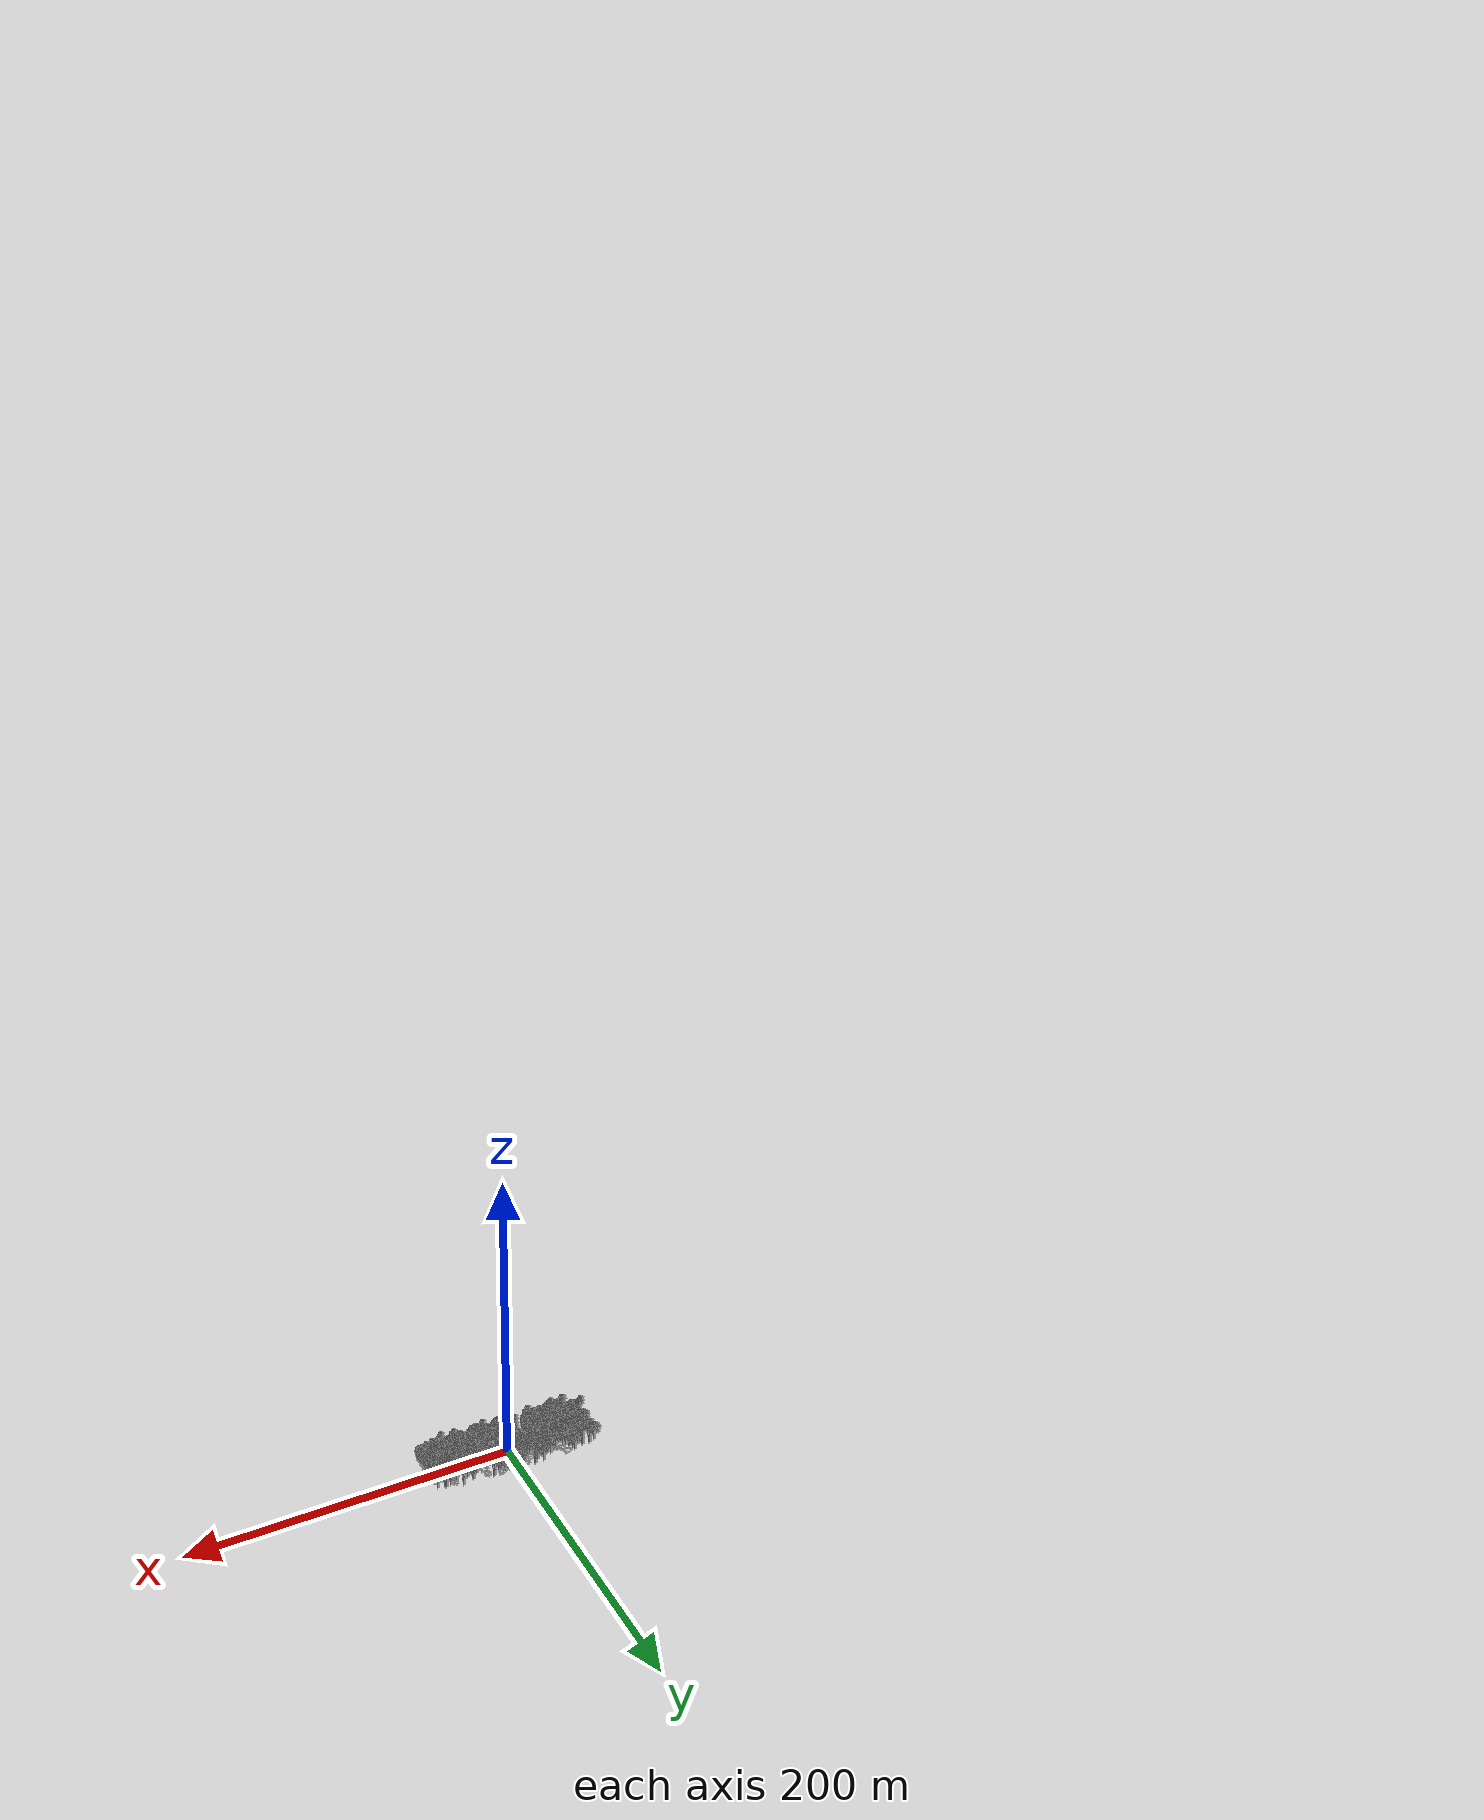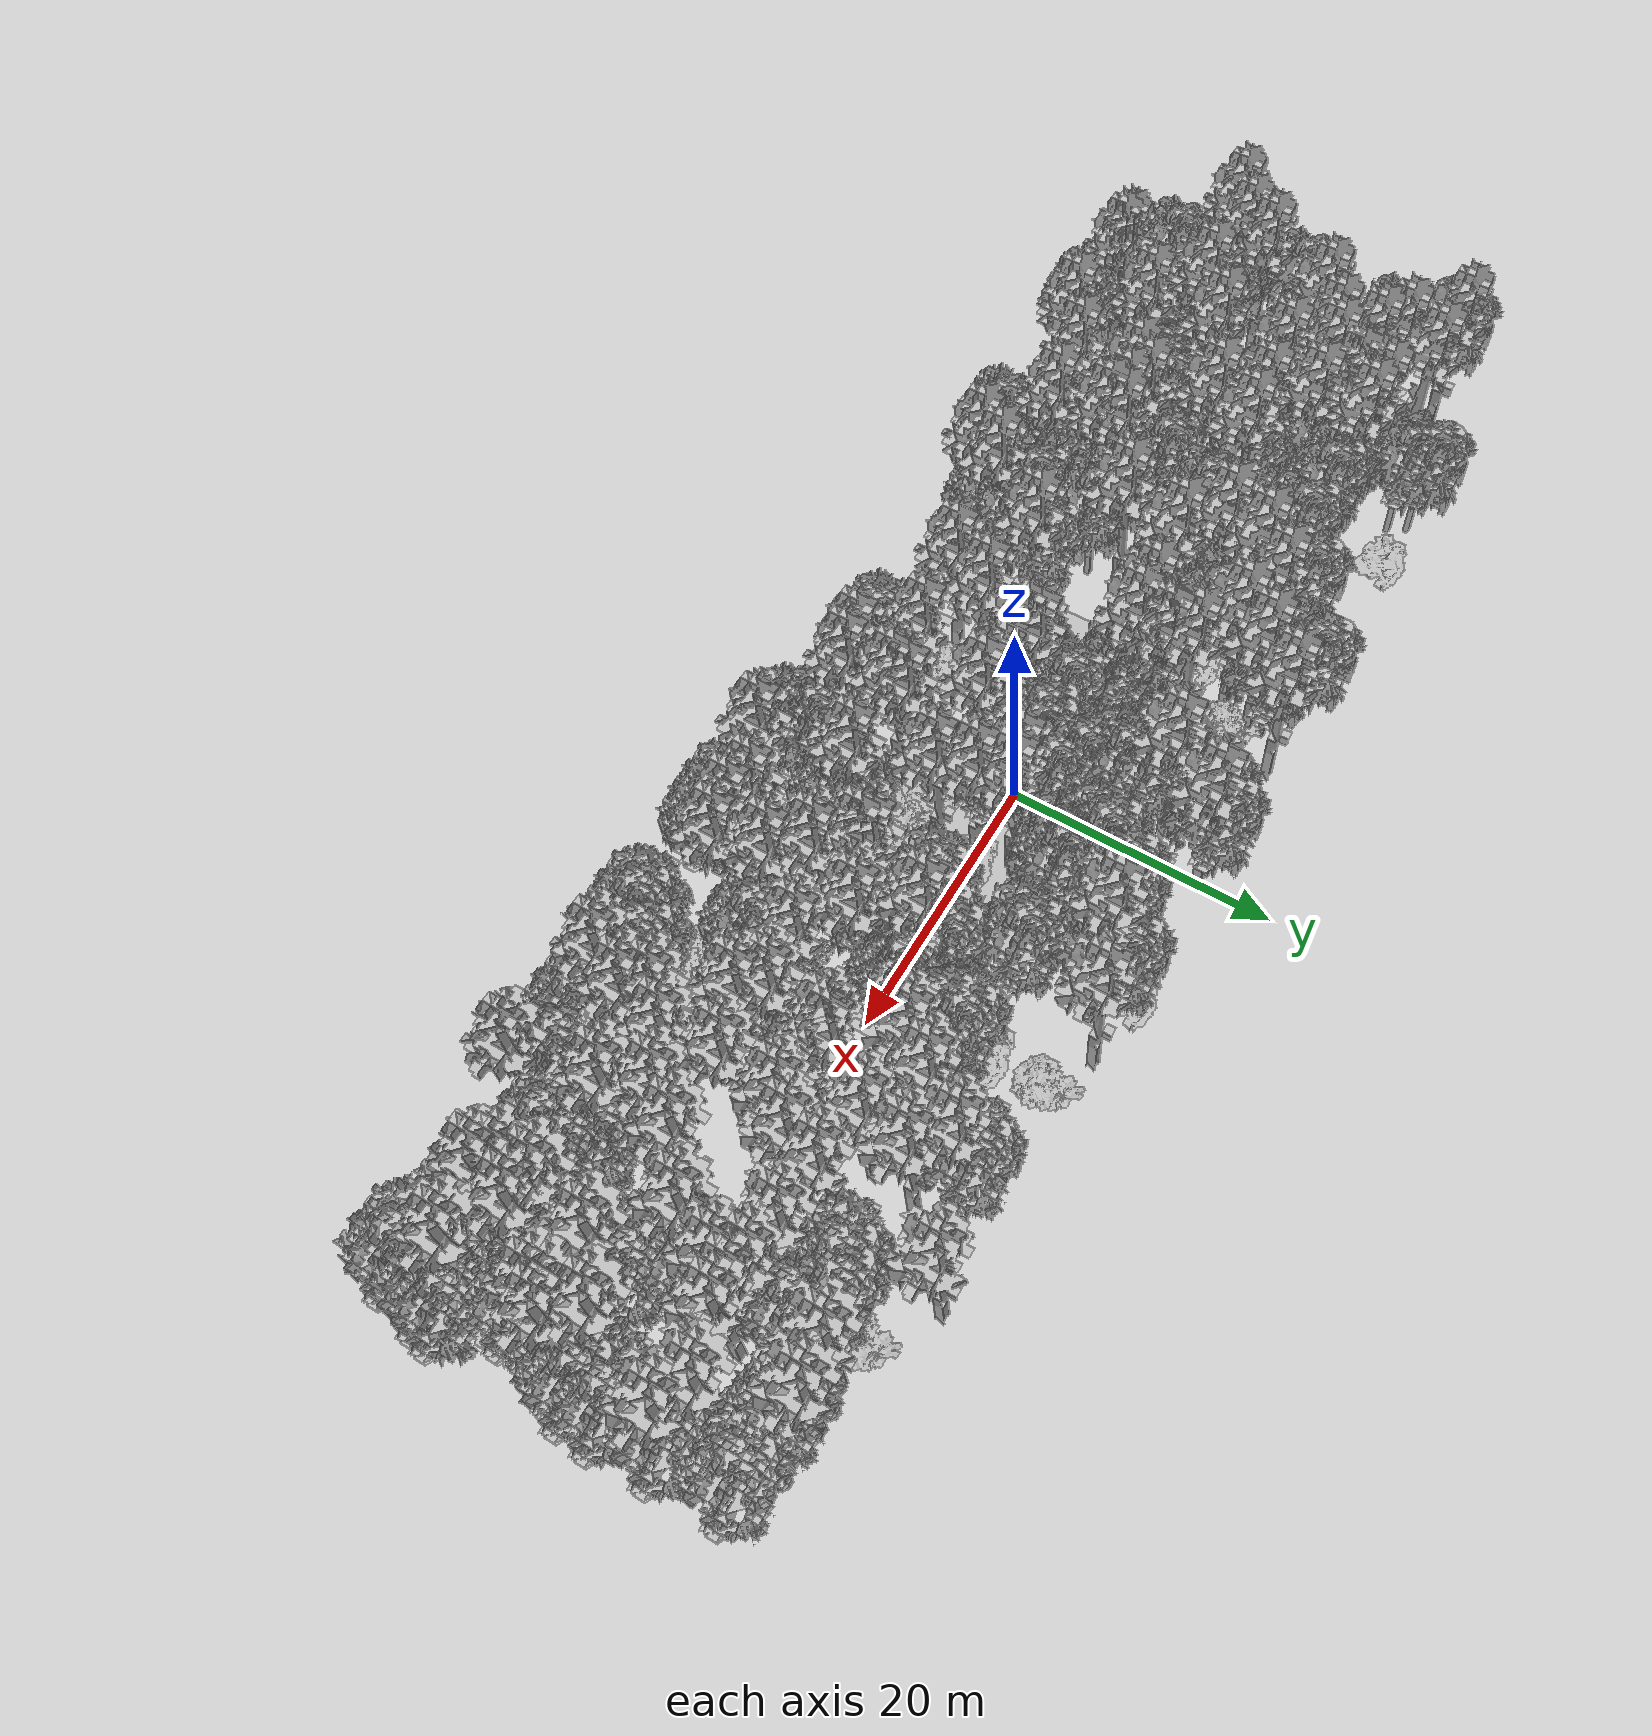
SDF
<sdf version="1.7">
    <world name="default">
        <plugin name="mrs_gazebo_static_transform_republisher_plugin" filename="libMrsGazeboCommonResources_StaticTransformRepublisher.so"/>
        <spherical_coordinates>
            <surface_model>EARTH_WGS84</surface_model>
            <latitude_deg>47.3977</latitude_deg>
            <longitude_deg>8.54559</longitude_deg>
            <elevation>0</elevation>
            <heading_deg>0</heading_deg>
        </spherical_coordinates>
        <physics name="default_physics" default="0" type="ode">
            <ode>
                <solver>
                    <type>quick</type>
                    <iters>10</iters>
                    <sor>1.3</sor>
                    <use_dynamic_moi_rescaling>0</use_dynamic_moi_rescaling>
                </solver>
                <constraints>
                    <cfm>0</cfm>
                    <erp>0.2</erp>
                    <contact_max_correcting_vel>1000</contact_max_correcting_vel>
                    <contact_surface_layer>0.001</contact_surface_layer>
                </constraints>
            </ode>
            <max_step_size>0.004</max_step_size>
            <real_time_factor>1</real_time_factor>
            <real_time_update_rate>250</real_time_update_rate>
        </physics>
        <scene>
            <shadows>0</shadows>
            <ambient>0.4 0.4 0.4 1</ambient>
            <background>0.7 0.7 0.7 1</background>
        </scene>
        <light name="sun" type="directional">
            <pose>0 0 1000 0.4 0.2 0</pose>
            <diffuse>1 1 1 1</diffuse>
            <specular>0.6 0.6 0.6 1</specular>
            <direction>0.1 0.1 -0.9</direction>
            <attenuation>
                <range>20</range>
                <constant>0.5</constant>
                <linear>0.01</linear>
                <quadratic>0.001</quadratic>
            </attenuation>
            <cast_shadows>1</cast_shadows>
            <spot>
                <inner_angle>0</inner_angle>
                <outer_angle>0</outer_angle>
                <falloff>0</falloff>
            </spot>
        </light>
        <model name="ground_plane">
            <static>1</static>
            <link name="link">
                <collision name="collision">
                    <pose>-50 0 0 0 -0 0</pose>
                    <geometry>
                        <plane>
                            <normal>0 0 1</normal>
                            <size>100 100</size>
                        </plane>
                    </geometry>
                    <surface>
                        <contact>
                            <ode>
                                <min_depth>0.01</min_depth>
                                <max_vel>0</max_vel>
                            </ode>
                        </contact>
                        <friction>
                            <ode/>
                            <torsional>
                                <ode/>
                            </torsional>
                        </friction>
                        <bounce/>
                    </surface>
                    <max_contacts>10</max_contacts>
                </collision>
                <visual name="grass">
                    <pose>0 0 0 0 -0 0</pose>
                    <cast_shadows>0</cast_shadows>
                    <geometry>
                        <mesh>
                            <scale>0.5814285714285714 0.18142857142857144 0.1</scale>
                            <uri>file://grass_plane/meshes/grass_plane.dae</uri>
                        </mesh>
                    </geometry>
                </visual>
                <self_collide>0</self_collide>
                <enable_wind>0</enable_wind>
                <kinematic>0</kinematic>
            </link>
        </model>
        <model name="the_void">
            <static>1</static>
            <link name="link">
                <pose>0 0 0.1 0 -0 0</pose>
                <visual name="the_void">
                    <pose>0 0 2 0 -0 0</pose>
                    <geometry>
                        <sphere>
                            <radius>0.25</radius>
                        </sphere>
                    </geometry>
                    <material>
                        <script>
                            <uri>file://media/materials/scripts/Gazebo.material</uri>
                            <name>Gazebo/Black</name>
                        </script>
                    </material>
                </visual>
                <self_collide>0</self_collide>
                <enable_wind>0</enable_wind>
                <kinematic>0</kinematic>
            </link>
            <pose>-1000 -1000 0 0 -0 0</pose>
        </model>
        <gui fullscreen="0">
            <camera name="camera">
                <pose>35.1577 98.6044 40.0204 0 0.407996 -1.99761</pose>
                <view_controller>orbit</view_controller>
                <projection_type>perspective</projection_type>
            </camera>
        </gui>
        <plugin name="mrs_gazebo_rviz_cam_synchronizer" filename="libMrsGazeboCommonResources_RvizCameraSynchronizer.so">
            <target_frame_id>gazebo_user_camera</target_frame_id>
            <world_origin_frame_id>uav1/gps_origin</world_origin_frame_id>
            <frame_to_follow>uav1</frame_to_follow>
        </plugin>
        <gravity>0 0 -9.8066</gravity>
        <magnetic_field>6e-06 2.3e-05 -4.2e-05</magnetic_field>
        <atmosphere type="adiabatic"/>
        <wind/>
        <model name="Tree 0">
            <static>1</static>
            <pose>6.119149855138183 -2.632654358781883 0 1.57079 -0 0</pose>
            <link name="link">
                <pose>0 0 0 0 -0 0</pose>
                <collision name="collision">
                    <geometry>
                        <mesh>
                            <scale>3.5 5 3.5</scale>
                            <uri>model://tree_9/meshes/tree_9.obj</uri>
                        </mesh>
                    </geometry>
                    <max_contacts>10</max_contacts>
                    <surface>
                        <contact>
                            <ode/>
                        </contact>
                        <bounce/>
                        <friction>
                            <torsional>
                                <ode/>
                            </torsional>
                            <ode/>
                        </friction>
                    </surface>
                </collision>
                <visual name="visual">
                    <geometry>
                        <mesh>
                            <scale>3.5 5 3.5</scale>
                            <uri>model://tree_9/meshes/tree_9.obj</uri>
                        </mesh>
                    </geometry>
                </visual>
                <self_collide>0</self_collide>
                <enable_wind>0</enable_wind>
                <kinematic>0</kinematic>
            </link>
        </model>
        <model name="Tree 1">
            <static>1</static>
            <pose>-16.062787158504072 2.690668989017393 0 1.57079 -0 0</pose>
            <link name="link">
                <pose>0 0 0 0 -0 0</pose>
                <collision name="collision">
                    <geometry>
                        <mesh>
                            <scale>3.5 5 3.5</scale>
                            <uri>model://tree_2/meshes/tree_2.obj</uri>
                        </mesh>
                    </geometry>
                    <max_contacts>10</max_contacts>
                    <surface>
                        <contact>
                            <ode/>
                        </contact>
                        <bounce/>
                        <friction>
                            <torsional>
                                <ode/>
                            </torsional>
                            <ode/>
                        </friction>
                    </surface>
                </collision>
                <visual name="visual">
                    <geometry>
                        <mesh>
                            <scale>3.5 5 3.5</scale>
                            <uri>model://tree_2/meshes/tree_2.obj</uri>
                        </mesh>
                    </geometry>
                </visual>
                <self_collide>0</self_collide>
                <enable_wind>0</enable_wind>
                <kinematic>0</kinematic>
            </link>
        </model>
        <model name="Tree 2">
            <static>1</static>
            <pose>5.522588944779287 -12.322842236727526 0 1.57079 -0 0</pose>
            <link name="link">
                <pose>0 0 0 0 -0 0</pose>
                <collision name="collision">
                    <geometry>
                        <mesh>
                            <scale>3.5 5 3.5</scale>
                            <uri>model://tree_2/meshes/tree_2.obj</uri>
                        </mesh>
                    </geometry>
                    <max_contacts>10</max_contacts>
                    <surface>
                        <contact>
                            <ode/>
                        </contact>
                        <bounce/>
                        <friction>
                            <torsional>
                                <ode/>
                            </torsional>
                            <ode/>
                        </friction>
                    </surface>
                </collision>
                <visual name="visual">
                    <geometry>
                        <mesh>
                            <scale>3.5 5 3.5</scale>
                            <uri>model://tree_2/meshes/tree_2.obj</uri>
                        </mesh>
                    </geometry>
                </visual>
                <self_collide>0</self_collide>
                <enable_wind>0</enable_wind>
                <kinematic>0</kinematic>
            </link>
        </model>
        <model name="Tree 3">
            <static>1</static>
            <pose>48.38571154356791 -9.816409687818725 0 1.57079 -0 0</pose>
            <link name="link">
                <pose>0 0 0 0 -0 0</pose>
                <collision name="collision">
                    <geometry>
                        <mesh>
                            <scale>3.5 5 3.5</scale>
                            <uri>model://tree_2/meshes/tree_2.obj</uri>
                        </mesh>
                    </geometry>
                    <max_contacts>10</max_contacts>
                    <surface>
                        <contact>
                            <ode/>
                        </contact>
                        <bounce/>
                        <friction>
                            <torsional>
                                <ode/>
                            </torsional>
                            <ode/>
                        </friction>
                    </surface>
                </collision>
                <visual name="visual">
                    <geometry>
                        <mesh>
                            <scale>3.5 5 3.5</scale>
                            <uri>model://tree_2/meshes/tree_2.obj</uri>
                        </mesh>
                    </geometry>
                </visual>
                <self_collide>0</self_collide>
                <enable_wind>0</enable_wind>
                <kinematic>0</kinematic>
            </link>
        </model>
        <model name="Tree 4">
            <static>1</static>
            <pose>10.652877007069627 13.814345372245114 0 1.57079 -0 0</pose>
            <link name="link">
                <pose>0 0 0 0 -0 0</pose>
                <collision name="collision">
                    <geometry>
                        <mesh>
                            <scale>3.5 5 3.5</scale>
                            <uri>model://tree_2/meshes/tree_2.obj</uri>
                        </mesh>
                    </geometry>
                    <max_contacts>10</max_contacts>
                    <surface>
                        <contact>
                            <ode/>
                        </contact>
                        <bounce/>
                        <friction>
                            <torsional>
                                <ode/>
                            </torsional>
                            <ode/>
                        </friction>
                    </surface>
                </collision>
                <visual name="visual">
                    <geometry>
                        <mesh>
                            <scale>3.5 5 3.5</scale>
                            <uri>model://tree_2/meshes/tree_2.obj</uri>
                        </mesh>
                    </geometry>
                </visual>
                <self_collide>0</self_collide>
                <enable_wind>0</enable_wind>
                <kinematic>0</kinematic>
            </link>
        </model>
        <model name="Tree 5">
            <static>1</static>
            <pose>34.673086230254086 -9.217702355086361 0 1.57079 -0 0</pose>
            <link name="link">
                <pose>0 0 0 0 -0 0</pose>
                <collision name="collision">
                    <geometry>
                        <mesh>
                            <scale>4 2.5 4</scale>
                            <uri>model://tree_1/meshes/tree_1.obj</uri>
                        </mesh>
                    </geometry>
                    <max_contacts>10</max_contacts>
                    <surface>
                        <contact>
                            <ode/>
                        </contact>
                        <bounce/>
                        <friction>
                            <torsional>
                                <ode/>
                            </torsional>
                            <ode/>
                        </friction>
                    </surface>
                </collision>
                <visual name="visual">
                    <geometry>
                        <mesh>
                            <scale>4 2.5 4</scale>
                            <uri>model://tree_1/meshes/tree_1.obj</uri>
                        </mesh>
                    </geometry>
                </visual>
                <self_collide>0</self_collide>
                <enable_wind>0</enable_wind>
                <kinematic>0</kinematic>
            </link>
        </model>
        <model name="Tree 6">
            <static>1</static>
            <pose>-17.15751394996521 9.124569294484395 0 1.57079 -0 0</pose>
            <link name="link">
                <pose>0 0 0 0 -0 0</pose>
                <collision name="collision">
                    <geometry>
                        <mesh>
                            <scale>3 2 3</scale>
                            <uri>model://tree_3/meshes/tree_3.obj</uri>
                        </mesh>
                    </geometry>
                    <max_contacts>10</max_contacts>
                    <surface>
                        <contact>
                            <ode/>
                        </contact>
                        <bounce/>
                        <friction>
                            <torsional>
                                <ode/>
                            </torsional>
                            <ode/>
                        </friction>
                    </surface>
                </collision>
                <visual name="visual">
                    <geometry>
                        <mesh>
                            <scale>3 2 3</scale>
                            <uri>model://tree_3/meshes/tree_3.obj</uri>
                        </mesh>
                    </geometry>
                </visual>
                <self_collide>0</self_collide>
                <enable_wind>0</enable_wind>
                <kinematic>0</kinematic>
            </link>
        </model>
        <model name="Tree 7">
            <static>1</static>
            <pose>-20.042771031521408 8.194792321414138 0 1.57079 -0 0</pose>
            <link name="link">
                <pose>0 0 0 0 -0 0</pose>
                <collision name="collision">
                    <geometry>
                        <mesh>
                            <scale>3.5 5 3.5</scale>
                            <uri>model://tree_9/meshes/tree_9.obj</uri>
                        </mesh>
                    </geometry>
                    <max_contacts>10</max_contacts>
                    <surface>
                        <contact>
                            <ode/>
                        </contact>
                        <bounce/>
                        <friction>
                            <torsional>
                                <ode/>
                            </torsional>
                            <ode/>
                        </friction>
                    </surface>
                </collision>
                <visual name="visual">
                    <geometry>
                        <mesh>
                            <scale>3.5 5 3.5</scale>
                            <uri>model://tree_9/meshes/tree_9.obj</uri>
                        </mesh>
                    </geometry>
                </visual>
                <self_collide>0</self_collide>
                <enable_wind>0</enable_wind>
                <kinematic>0</kinematic>
            </link>
        </model>
        <model name="Tree 8">
            <static>1</static>
            <pose>-0.33528790532663777 -2.7939643381200234 0 1.57079 -0 0</pose>
            <link name="link">
                <pose>0 0 0 0 -0 0</pose>
                <collision name="collision">
                    <geometry>
                        <mesh>
                            <scale>3.5 5 3.5</scale>
                            <uri>model://tree_9/meshes/tree_9.obj</uri>
                        </mesh>
                    </geometry>
                    <max_contacts>10</max_contacts>
                    <surface>
                        <contact>
                            <ode/>
                        </contact>
                        <bounce/>
                        <friction>
                            <torsional>
                                <ode/>
                            </torsional>
                            <ode/>
                        </friction>
                    </surface>
                </collision>
                <visual name="visual">
                    <geometry>
                        <mesh>
                            <scale>3.5 5 3.5</scale>
                            <uri>model://tree_9/meshes/tree_9.obj</uri>
                        </mesh>
                    </geometry>
                </visual>
                <self_collide>0</self_collide>
                <enable_wind>0</enable_wind>
                <kinematic>0</kinematic>
            </link>
        </model>
        <model name="Tree 9">
            <static>1</static>
            <pose>-41.20711101293796 11.857801258161302 0 1.57079 -0 0</pose>
            <link name="link">
                <pose>0 0 0 0 -0 0</pose>
                <collision name="collision">
                    <geometry>
                        <mesh>
                            <scale>3.5 5 3.5</scale>
                            <uri>model://tree_9/meshes/tree_9.obj</uri>
                        </mesh>
                    </geometry>
                    <max_contacts>10</max_contacts>
                    <surface>
                        <contact>
                            <ode/>
                        </contact>
                        <bounce/>
                        <friction>
                            <torsional>
                                <ode/>
                            </torsional>
                            <ode/>
                        </friction>
                    </surface>
                </collision>
                <visual name="visual">
                    <geometry>
                        <mesh>
                            <scale>3.5 5 3.5</scale>
                            <uri>model://tree_9/meshes/tree_9.obj</uri>
                        </mesh>
                    </geometry>
                </visual>
                <self_collide>0</self_collide>
                <enable_wind>0</enable_wind>
                <kinematic>0</kinematic>
            </link>
        </model>
        <model name="Tree 10">
            <static>1</static>
            <pose>-24.68343236074492 2.107477035243388 0 1.57079 -0 0</pose>
            <link name="link">
                <pose>0 0 0 0 -0 0</pose>
                <collision name="collision">
                    <geometry>
                        <mesh>
                            <scale>3.5 5 3.5</scale>
                            <uri>model://tree_2/meshes/tree_2.obj</uri>
                        </mesh>
                    </geometry>
                    <max_contacts>10</max_contacts>
                    <surface>
                        <contact>
                            <ode/>
                        </contact>
                        <bounce/>
                        <friction>
                            <torsional>
                                <ode/>
                            </torsional>
                            <ode/>
                        </friction>
                    </surface>
                </collision>
                <visual name="visual">
                    <geometry>
                        <mesh>
                            <scale>3.5 5 3.5</scale>
                            <uri>model://tree_2/meshes/tree_2.obj</uri>
                        </mesh>
                    </geometry>
                </visual>
                <self_collide>0</self_collide>
                <enable_wind>0</enable_wind>
                <kinematic>0</kinematic>
            </link>
        </model>
        <model name="Tree 11">
            <static>1</static>
            <pose>-20.97144513148601 -13.041322707883674 0 1.57079 -0 0</pose>
            <link name="link">
                <pose>0 0 0 0 -0 0</pose>
                <collision name="collision">
                    <geometry>
                        <mesh>
                            <scale>3.5 5 3.5</scale>
                            <uri>model://tree_2/meshes/tree_2.obj</uri>
                        </mesh>
                    </geometry>
                    <max_contacts>10</max_contacts>
                    <surface>
                        <contact>
                            <ode/>
                        </contact>
                        <bounce/>
                        <friction>
                            <torsional>
                                <ode/>
                            </torsional>
                            <ode/>
                        </friction>
                    </surface>
                </collision>
                <visual name="visual">
                    <geometry>
                        <mesh>
                            <scale>3.5 5 3.5</scale>
                            <uri>model://tree_2/meshes/tree_2.obj</uri>
                        </mesh>
                    </geometry>
                </visual>
                <self_collide>0</self_collide>
                <enable_wind>0</enable_wind>
                <kinematic>0</kinematic>
            </link>
        </model>
        <model name="Tree 12">
            <static>1</static>
            <pose>42.523572436256885 -8.748255863556011 0 1.57079 -0 0</pose>
            <link name="link">
                <pose>0 0 0 0 -0 0</pose>
                <collision name="collision">
                    <geometry>
                        <mesh>
                            <scale>3.5 5 3.5</scale>
                            <uri>model://tree_9/meshes/tree_9.obj</uri>
                        </mesh>
                    </geometry>
                    <max_contacts>10</max_contacts>
                    <surface>
                        <contact>
                            <ode/>
                        </contact>
                        <bounce/>
                        <friction>
                            <torsional>
                                <ode/>
                            </torsional>
                            <ode/>
                        </friction>
                    </surface>
                </collision>
                <visual name="visual">
                    <geometry>
                        <mesh>
                            <scale>3.5 5 3.5</scale>
                            <uri>model://tree_9/meshes/tree_9.obj</uri>
                        </mesh>
                    </geometry>
                </visual>
                <self_collide>0</self_collide>
                <enable_wind>0</enable_wind>
                <kinematic>0</kinematic>
            </link>
        </model>
        <model name="Tree 13">
            <static>1</static>
            <pose>-25.75330304576824 7.535871364246212 0 1.57079 -0 0</pose>
            <link name="link">
                <pose>0 0 0 0 -0 0</pose>
                <collision name="collision">
                    <geometry>
                        <mesh>
                            <scale>4 2.5 4</scale>
                            <uri>model://tree_1/meshes/tree_1.obj</uri>
                        </mesh>
                    </geometry>
                    <max_contacts>10</max_contacts>
                    <surface>
                        <contact>
                            <ode/>
                        </contact>
                        <bounce/>
                        <friction>
                            <torsional>
                                <ode/>
                            </torsional>
                            <ode/>
                        </friction>
                    </surface>
                </collision>
                <visual name="visual">
                    <geometry>
                        <mesh>
                            <scale>4 2.5 4</scale>
                            <uri>model://tree_1/meshes/tree_1.obj</uri>
                        </mesh>
                    </geometry>
                </visual>
                <self_collide>0</self_collide>
                <enable_wind>0</enable_wind>
                <kinematic>0</kinematic>
            </link>
        </model>
        <model name="Tree 14">
            <static>1</static>
            <pose>-2.6202465484503534 -11.016423006931841 0 1.57079 -0 0</pose>
            <link name="link">
                <pose>0 0 0 0 -0 0</pose>
                <collision name="collision">
                    <geometry>
                        <mesh>
                            <scale>3.5 5 3.5</scale>
                            <uri>model://tree_2/meshes/tree_2.obj</uri>
                        </mesh>
                    </geometry>
                    <max_contacts>10</max_contacts>
                    <surface>
                        <contact>
                            <ode/>
                        </contact>
                        <bounce/>
                        <friction>
                            <torsional>
                                <ode/>
                            </torsional>
                            <ode/>
                        </friction>
                    </surface>
                </collision>
                <visual name="visual">
                    <geometry>
                        <mesh>
                            <scale>3.5 5 3.5</scale>
                            <uri>model://tree_2/meshes/tree_2.obj</uri>
                        </mesh>
                    </geometry>
                </visual>
                <self_collide>0</self_collide>
                <enable_wind>0</enable_wind>
                <kinematic>0</kinematic>
            </link>
        </model>
        <model name="Tree 15">
            <static>1</static>
            <pose>12.84035809433049 2.5421332068999725 0 1.57079 -0 0</pose>
            <link name="link">
                <pose>0 0 0 0 -0 0</pose>
                <collision name="collision">
                    <geometry>
                        <mesh>
                            <scale>4 2.5 4</scale>
                            <uri>model://tree_1/meshes/tree_1.obj</uri>
                        </mesh>
                    </geometry>
                    <max_contacts>10</max_contacts>
                    <surface>
                        <contact>
                            <ode/>
                        </contact>
                        <bounce/>
                        <friction>
                            <torsional>
                                <ode/>
                            </torsional>
                            <ode/>
                        </friction>
                    </surface>
                </collision>
                <visual name="visual">
                    <geometry>
                        <mesh>
                            <scale>4 2.5 4</scale>
                            <uri>model://tree_1/meshes/tree_1.obj</uri>
                        </mesh>
                    </geometry>
                </visual>
                <self_collide>0</self_collide>
                <enable_wind>0</enable_wind>
                <kinematic>0</kinematic>
            </link>
        </model>
        <model name="Tree 16">
            <static>1</static>
            <pose>-8.613029995133267 -9.647444346793051 0 1.57079 -0 0</pose>
            <link name="link">
                <pose>0 0 0 0 -0 0</pose>
                <collision name="collision">
                    <geometry>
                        <mesh>
                            <scale>3.5 5 3.5</scale>
                            <uri>model://tree_9/meshes/tree_9.obj</uri>
                        </mesh>
                    </geometry>
                    <max_contacts>10</max_contacts>
                    <surface>
                        <contact>
                            <ode/>
                        </contact>
                        <bounce/>
                        <friction>
                            <torsional>
                                <ode/>
                            </torsional>
                            <ode/>
                        </friction>
                    </surface>
                </collision>
                <visual name="visual">
                    <geometry>
                        <mesh>
                            <scale>3.5 5 3.5</scale>
                            <uri>model://tree_9/meshes/tree_9.obj</uri>
                        </mesh>
                    </geometry>
                </visual>
                <self_collide>0</self_collide>
                <enable_wind>0</enable_wind>
                <kinematic>0</kinematic>
            </link>
        </model>
        <model name="Tree 17">
            <static>1</static>
            <pose>38.49166975786936 -8.459165041315796 0 1.57079 -0 0</pose>
            <link name="link">
                <pose>0 0 0 0 -0 0</pose>
                <collision name="collision">
                    <geometry>
                        <mesh>
                            <scale>4 2.5 4</scale>
                            <uri>model://tree_1/meshes/tree_1.obj</uri>
                        </mesh>
                    </geometry>
                    <max_contacts>10</max_contacts>
                    <surface>
                        <contact>
                            <ode/>
                        </contact>
                        <bounce/>
                        <friction>
                            <torsional>
                                <ode/>
                            </torsional>
                            <ode/>
                        </friction>
                    </surface>
                </collision>
                <visual name="visual">
                    <geometry>
                        <mesh>
                            <scale>4 2.5 4</scale>
                            <uri>model://tree_1/meshes/tree_1.obj</uri>
                        </mesh>
                    </geometry>
                </visual>
                <self_collide>0</self_collide>
                <enable_wind>0</enable_wind>
                <kinematic>0</kinematic>
            </link>
        </model>
        <model name="Tree 18">
            <static>1</static>
            <pose>3.6087251949312957 -5.171122828382419 0 1.57079 -0 0</pose>
            <link name="link">
                <pose>0 0 0 0 -0 0</pose>
                <collision name="collision">
                    <geometry>
                        <mesh>
                            <scale>4 2.5 4</scale>
                            <uri>model://tree_1/meshes/tree_1.obj</uri>
                        </mesh>
                    </geometry>
                    <max_contacts>10</max_contacts>
                    <surface>
                        <contact>
                            <ode/>
                        </contact>
                        <bounce/>
                        <friction>
                            <torsional>
                                <ode/>
                            </torsional>
                            <ode/>
                        </friction>
                    </surface>
                </collision>
                <visual name="visual">
                    <geometry>
                        <mesh>
                            <scale>4 2.5 4</scale>
                            <uri>model://tree_1/meshes/tree_1.obj</uri>
                        </mesh>
                    </geometry>
                </visual>
                <self_collide>0</self_collide>
                <enable_wind>0</enable_wind>
                <kinematic>0</kinematic>
            </link>
        </model>
        <model name="Tree 19">
            <static>1</static>
            <pose>41.78508932308581 -11.674716123932214 0 1.57079 -0 0</pose>
            <link name="link">
                <pose>0 0 0 0 -0 0</pose>
                <collision name="collision">
                    <geometry>
                        <mesh>
                            <scale>3.5 5 3.5</scale>
                            <uri>model://tree_9/meshes/tree_9.obj</uri>
                        </mesh>
                    </geometry>
                    <max_contacts>10</max_contacts>
                    <surface>
                        <contact>
                            <ode/>
                        </contact>
                        <bounce/>
                        <friction>
                            <torsional>
                                <ode/>
                            </torsional>
                            <ode/>
                        </friction>
                    </surface>
                </collision>
                <visual name="visual">
                    <geometry>
                        <mesh>
                            <scale>3.5 5 3.5</scale>
                            <uri>model://tree_9/meshes/tree_9.obj</uri>
                        </mesh>
                    </geometry>
                </visual>
                <self_collide>0</self_collide>
                <enable_wind>0</enable_wind>
                <kinematic>0</kinematic>
            </link>
        </model>
        <model name="Tree 20">
            <static>1</static>
            <pose>-24.720509356675365 -6.560467251138821 0 1.57079 -0 0</pose>
            <link name="link">
                <pose>0 0 0 0 -0 0</pose>
                <collision name="collision">
                    <geometry>
                        <mesh>
                            <scale>3.5 5 3.5</scale>
                            <uri>model://tree_9/meshes/tree_9.obj</uri>
                        </mesh>
                    </geometry>
                    <max_contacts>10</max_contacts>
                    <surface>
                        <contact>
                            <ode/>
                        </contact>
                        <bounce/>
                        <friction>
                            <torsional>
                                <ode/>
                            </torsional>
                            <ode/>
                        </friction>
                    </surface>
                </collision>
                <visual name="visual">
                    <geometry>
                        <mesh>
                            <scale>3.5 5 3.5</scale>
                            <uri>model://tree_9/meshes/tree_9.obj</uri>
                        </mesh>
                    </geometry>
                </visual>
                <self_collide>0</self_collide>
                <enable_wind>0</enable_wind>
                <kinematic>0</kinematic>
            </link>
        </model>
        <model name="Tree 21">
            <static>1</static>
            <pose>36.001435455623735 5.011939128004059 0 1.57079 -0 0</pose>
            <link name="link">
                <pose>0 0 0 0 -0 0</pose>
                <collision name="collision">
                    <geometry>
                        <mesh>
                            <scale>3.5 5 3.5</scale>
                            <uri>model://tree_9/meshes/tree_9.obj</uri>
                        </mesh>
                    </geometry>
                    <max_contacts>10</max_contacts>
                    <surface>
                        <contact>
                            <ode/>
                        </contact>
                        <bounce/>
                        <friction>
                            <torsional>
                                <ode/>
                            </torsional>
                            <ode/>
                        </friction>
                    </surface>
                </collision>
                <visual name="visual">
                    <geometry>
                        <mesh>
                            <scale>3.5 5 3.5</scale>
                            <uri>model://tree_9/meshes/tree_9.obj</uri>
                        </mesh>
                    </geometry>
                </visual>
                <self_collide>0</self_collide>
                <enable_wind>0</enable_wind>
                <kinematic>0</kinematic>
            </link>
        </model>
        <model name="Tree 22">
            <static>1</static>
            <pose>24.124767231465142 -2.712410142354857 0 1.57079 -0 0</pose>
            <link name="link">
                <pose>0 0 0 0 -0 0</pose>
                <collision name="collision">
                    <geometry>
                        <mesh>
                            <scale>3.5 5 3.5</scale>
                            <uri>model://tree_2/meshes/tree_2.obj</uri>
                        </mesh>
                    </geometry>
                    <max_contacts>10</max_contacts>
                    <surface>
                        <contact>
                            <ode/>
                        </contact>
                        <bounce/>
                        <friction>
                            <torsional>
                                <ode/>
                            </torsional>
                            <ode/>
                        </friction>
                    </surface>
                </collision>
                <visual name="visual">
                    <geometry>
                        <mesh>
                            <scale>3.5 5 3.5</scale>
                            <uri>model://tree_2/meshes/tree_2.obj</uri>
                        </mesh>
                    </geometry>
                </visual>
                <self_collide>0</self_collide>
                <enable_wind>0</enable_wind>
                <kinematic>0</kinematic>
            </link>
        </model>
        <model name="Tree 23">
            <static>1</static>
            <pose>5.831807972442945 6.8223870980369625 0 1.57079 -0 0</pose>
            <link name="link">
                <pose>0 0 0 0 -0 0</pose>
                <collision name="collision">
                    <geometry>
                        <mesh>
                            <scale>3.5 5 3.5</scale>
                            <uri>model://tree_2/meshes/tree_2.obj</uri>
                        </mesh>
                    </geometry>
                    <max_contacts>10</max_contacts>
                    <surface>
                        <contact>
                            <ode/>
                        </contact>
                        <bounce/>
                        <friction>
                            <torsional>
                                <ode/>
                            </torsional>
                            <ode/>
                        </friction>
                    </surface>
                </collision>
                <visual name="visual">
                    <geometry>
                        <mesh>
                            <scale>3.5 5 3.5</scale>
                            <uri>model://tree_2/meshes/tree_2.obj</uri>
                        </mesh>
                    </geometry>
                </visual>
                <self_collide>0</self_collide>
                <enable_wind>0</enable_wind>
                <kinematic>0</kinematic>
            </link>
        </model>
        <model name="Tree 24">
            <static>1</static>
            <pose>15.105307806001214 -14.23932404193658 0 1.57079 -0 0</pose>
            <link name="link">
                <pose>0 0 0 0 -0 0</pose>
                <collision name="collision">
                    <geometry>
                        <mesh>
                            <scale>3.5 5 3.5</scale>
                            <uri>model://tree_2/meshes/tree_2.obj</uri>
                        </mesh>
                    </geometry>
                    <max_contacts>10</max_contacts>
                    <surface>
                        <contact>
                            <ode/>
                        </contact>
                        <bounce/>
                        <friction>
                            <torsional>
                                <ode/>
                            </torsional>
                            <ode/>
                        </friction>
                    </surface>
                </collision>
                <visual name="visual">
                    <geometry>
                        <mesh>
                            <scale>3.5 5 3.5</scale>
                            <uri>model://tree_2/meshes/tree_2.obj</uri>
                        </mesh>
                    </geometry>
                </visual>
                <self_collide>0</self_collide>
                <enable_wind>0</enable_wind>
                <kinematic>0</kinematic>
            </link>
        </model>
        <model name="Tree 25">
            <static>1</static>
            <pose>47.33242879049929 -8.25013505071646 0 1.57079 -0 0</pose>
            <link name="link">
                <pose>0 0 0 0 -0 0</pose>
                <collision name="collision">
                    <geometry>
                        <mesh>
                            <scale>3 2 3</scale>
                            <uri>model://tree_3/meshes/tree_3.obj</uri>
                        </mesh>
                    </geometry>
                    <max_contacts>10</max_contacts>
                    <surface>
                        <contact>
                            <ode/>
                        </contact>
                        <bounce/>
                        <friction>
                            <torsional>
                                <ode/>
                            </torsional>
                            <ode/>
                        </friction>
                    </surface>
                </collision>
                <visual name="visual">
                    <geometry>
                        <mesh>
                            <scale>3 2 3</scale>
                            <uri>model://tree_3/meshes/tree_3.obj</uri>
                        </mesh>
                    </geometry>
                </visual>
                <self_collide>0</self_collide>
                <enable_wind>0</enable_wind>
                <kinematic>0</kinematic>
            </link>
        </model>
        <model name="Tree 26">
            <static>1</static>
            <pose>24.348586820520367 -3.27734799783655 0 1.57079 -0 0</pose>
            <link name="link">
                <pose>0 0 0 0 -0 0</pose>
                <collision name="collision">
                    <geometry>
                        <mesh>
                            <scale>3.5 5 3.5</scale>
                            <uri>model://tree_9/meshes/tree_9.obj</uri>
                        </mesh>
                    </geometry>
                    <max_contacts>10</max_contacts>
                    <surface>
                        <contact>
                            <ode/>
                        </contact>
                        <bounce/>
                        <friction>
                            <torsional>
                                <ode/>
                            </torsional>
                            <ode/>
                        </friction>
                    </surface>
                </collision>
                <visual name="visual">
                    <geometry>
                        <mesh>
                            <scale>3.5 5 3.5</scale>
                            <uri>model://tree_9/meshes/tree_9.obj</uri>
                        </mesh>
                    </geometry>
                </visual>
                <self_collide>0</self_collide>
                <enable_wind>0</enable_wind>
                <kinematic>0</kinematic>
            </link>
        </model>
        <model name="Tree 27">
            <static>1</static>
            <pose>-30.72963443361177 14.336017798661647 0 1.57079 -0 0</pose>
            <link name="link">
                <pose>0 0 0 0 -0 0</pose>
                <collision name="collision">
                    <geometry>
                        <mesh>
                            <scale>3 2 3</scale>
                            <uri>model://tree_3/meshes/tree_3.obj</uri>
                        </mesh>
                    </geometry>
                    <max_contacts>10</max_contacts>
                    <surface>
                        <contact>
                            <ode/>
                        </contact>
                        <bounce/>
                        <friction>
                            <torsional>
                                <ode/>
                            </torsional>
                            <ode/>
                        </friction>
                    </surface>
                </collision>
                <visual name="visual">
                    <geometry>
                        <mesh>
                            <scale>3 2 3</scale>
                            <uri>model://tree_3/meshes/tree_3.obj</uri>
                        </mesh>
                    </geometry>
                </visual>
                <self_collide>0</self_collide>
                <enable_wind>0</enable_wind>
                <kinematic>0</kinematic>
            </link>
        </model>
        <model name="Tree 28">
            <static>1</static>
            <pose>9.337387091460933 -8.031468618281135 0 1.57079 -0 0</pose>
            <link name="link">
                <pose>0 0 0 0 -0 0</pose>
                <collision name="collision">
                    <geometry>
                        <mesh>
                            <scale>3.5 5 3.5</scale>
                            <uri>model://tree_2/meshes/tree_2.obj</uri>
                        </mesh>
                    </geometry>
                    <max_contacts>10</max_contacts>
                    <surface>
                        <contact>
                            <ode/>
                        </contact>
                        <bounce/>
                        <friction>
                            <torsional>
                                <ode/>
                            </torsional>
                            <ode/>
                        </friction>
                    </surface>
                </collision>
                <visual name="visual">
                    <geometry>
                        <mesh>
                            <scale>3.5 5 3.5</scale>
                            <uri>model://tree_2/meshes/tree_2.obj</uri>
                        </mesh>
                    </geometry>
                </visual>
                <self_collide>0</self_collide>
                <enable_wind>0</enable_wind>
                <kinematic>0</kinematic>
            </link>
        </model>
        <model name="Tree 29">
            <static>1</static>
            <pose>5.5614273797064655 12.232940732049109 0 1.57079 -0 0</pose>
            <link name="link">
                <pose>0 0 0 0 -0 0</pose>
                <collision name="collision">
                    <geometry>
                        <mesh>
                            <scale>4 2.5 4</scale>
                            <uri>model://tree_1/meshes/tree_1.obj</uri>
                        </mesh>
                    </geometry>
                    <max_contacts>10</max_contacts>
                    <surface>
                        <contact>
                            <ode/>
                        </contact>
                        <bounce/>
                        <friction>
                            <torsional>
                                <ode/>
                            </torsional>
                            <ode/>
                        </friction>
                    </surface>
                </collision>
                <visual name="visual">
                    <geometry>
                        <mesh>
                            <scale>4 2.5 4</scale>
                            <uri>model://tree_1/meshes/tree_1.obj</uri>
                        </mesh>
                    </geometry>
                </visual>
                <self_collide>0</self_collide>
                <enable_wind>0</enable_wind>
                <kinematic>0</kinematic>
            </link>
        </model>
        <model name="Tree 30">
            <static>1</static>
            <pose>-36.678549349047785 -1.8676654254299443 0 1.57079 -0 0</pose>
            <link name="link">
                <pose>0 0 0 0 -0 0</pose>
                <collision name="collision">
                    <geometry>
                        <mesh>
                            <scale>3 2 3</scale>
                            <uri>model://tree_3/meshes/tree_3.obj</uri>
                        </mesh>
                    </geometry>
                    <max_contacts>10</max_contacts>
                    <surface>
                        <contact>
                            <ode/>
                        </contact>
                        <bounce/>
                        <friction>
                            <torsional>
                                <ode/>
                            </torsional>
                            <ode/>
                        </friction>
                    </surface>
                </collision>
                <visual name="visual">
                    <geometry>
                        <mesh>
                            <scale>3 2 3</scale>
                            <uri>model://tree_3/meshes/tree_3.obj</uri>
                        </mesh>
                    </geometry>
                </visual>
                <self_collide>0</self_collide>
                <enable_wind>0</enable_wind>
                <kinematic>0</kinematic>
            </link>
        </model>
        <model name="Tree 31">
            <static>1</static>
            <pose>25.302204731030642 1.6287127306009737 0 1.57079 -0 0</pose>
            <link name="link">
                <pose>0 0 0 0 -0 0</pose>
                <collision name="collision">
                    <geometry>
                        <mesh>
                            <scale>3.5 5 3.5</scale>
                            <uri>model://tree_9/meshes/tree_9.obj</uri>
                        </mesh>
                    </geometry>
                    <max_contacts>10</max_contacts>
                    <surface>
                        <contact>
                            <ode/>
                        </contact>
                        <bounce/>
                        <friction>
                            <torsional>
                                <ode/>
                            </torsional>
                            <ode/>
                        </friction>
                    </surface>
                </collision>
                <visual name="visual">
                    <geometry>
                        <mesh>
                            <scale>3.5 5 3.5</scale>
                            <uri>model://tree_9/meshes/tree_9.obj</uri>
                        </mesh>
                    </geometry>
                </visual>
                <self_collide>0</self_collide>
                <enable_wind>0</enable_wind>
                <kinematic>0</kinematic>
            </link>
        </model>
        <model name="Tree 32">
            <static>1</static>
            <pose>28.1410045352838 -9.11618545782786 0 1.57079 -0 0</pose>
            <link name="link">
                <pose>0 0 0 0 -0 0</pose>
                <collision name="collision">
                    <geometry>
                        <mesh>
                            <scale>3.5 5 3.5</scale>
                            <uri>model://tree_9/meshes/tree_9.obj</uri>
                        </mesh>
                    </geometry>
                    <max_contacts>10</max_contacts>
                    <surface>
                        <contact>
                            <ode/>
                        </contact>
                        <bounce/>
                        <friction>
                            <torsional>
                                <ode/>
                            </torsional>
                            <ode/>
                        </friction>
                    </surface>
                </collision>
                <visual name="visual">
                    <geometry>
                        <mesh>
                            <scale>3.5 5 3.5</scale>
                            <uri>model://tree_9/meshes/tree_9.obj</uri>
                        </mesh>
                    </geometry>
                </visual>
                <self_collide>0</self_collide>
                <enable_wind>0</enable_wind>
                <kinematic>0</kinematic>
            </link>
        </model>
        <model name="Tree 33">
            <static>1</static>
            <pose>-7.900962774767379 3.4441673641189823 0 1.57079 -0 0</pose>
            <link name="link">
                <pose>0 0 0 0 -0 0</pose>
                <collision name="collision">
                    <geometry>
                        <mesh>
                            <scale>3.5 5 3.5</scale>
                            <uri>model://tree_2/meshes/tree_2.obj</uri>
                        </mesh>
                    </geometry>
                    <max_contacts>10</max_contacts>
                    <surface>
                        <contact>
                            <ode/>
                        </contact>
                        <bounce/>
                        <friction>
                            <torsional>
                                <ode/>
                            </torsional>
                            <ode/>
                        </friction>
                    </surface>
                </collision>
                <visual name="visual">
                    <geometry>
                        <mesh>
                            <scale>3.5 5 3.5</scale>
                            <uri>model://tree_2/meshes/tree_2.obj</uri>
                        </mesh>
                    </geometry>
                </visual>
                <self_collide>0</self_collide>
                <enable_wind>0</enable_wind>
                <kinematic>0</kinematic>
            </link>
        </model>
        <model name="Tree 34">
            <static>1</static>
            <pose>-25.53793594194339 -8.206140084080793 0 1.57079 -0 0</pose>
            <link name="link">
                <pose>0 0 0 0 -0 0</pose>
                <collision name="collision">
                    <geometry>
                        <mesh>
                            <scale>3.5 5 3.5</scale>
                            <uri>model://tree_2/meshes/tree_2.obj</uri>
                        </mesh>
                    </geometry>
                    <max_contacts>10</max_contacts>
                    <surface>
                        <contact>
                            <ode/>
                        </contact>
                        <bounce/>
                        <friction>
                            <torsional>
                                <ode/>
                            </torsional>
                            <ode/>
                        </friction>
                    </surface>
                </collision>
                <visual name="visual">
                    <geometry>
                        <mesh>
                            <scale>3.5 5 3.5</scale>
                            <uri>model://tree_2/meshes/tree_2.obj</uri>
                        </mesh>
                    </geometry>
                </visual>
                <self_collide>0</self_collide>
                <enable_wind>0</enable_wind>
                <kinematic>0</kinematic>
            </link>
        </model>
        <model name="Tree 35">
            <static>1</static>
            <pose>-10.600810305536932 14.61796579168653 0 1.57079 -0 0</pose>
            <link name="link">
                <pose>0 0 0 0 -0 0</pose>
                <collision name="collision">
                    <geometry>
                        <mesh>
                            <scale>3.5 5 3.5</scale>
                            <uri>model://tree_9/meshes/tree_9.obj</uri>
                        </mesh>
                    </geometry>
                    <max_contacts>10</max_contacts>
                    <surface>
                        <contact>
                            <ode/>
                        </contact>
                        <bounce/>
                        <friction>
                            <torsional>
                                <ode/>
                            </torsional>
                            <ode/>
                        </friction>
                    </surface>
                </collision>
                <visual name="visual">
                    <geometry>
                        <mesh>
                            <scale>3.5 5 3.5</scale>
                            <uri>model://tree_9/meshes/tree_9.obj</uri>
                        </mesh>
                    </geometry>
                </visual>
                <self_collide>0</self_collide>
                <enable_wind>0</enable_wind>
                <kinematic>0</kinematic>
            </link>
        </model>
        <model name="Tree 36">
            <static>1</static>
            <pose>10.157732636431128 12.382553108645869 0 1.57079 -0 0</pose>
            <link name="link">
                <pose>0 0 0 0 -0 0</pose>
                <collision name="collision">
                    <geometry>
                        <mesh>
                            <scale>3.5 5 3.5</scale>
                            <uri>model://tree_2/meshes/tree_2.obj</uri>
                        </mesh>
                    </geometry>
                    <max_contacts>10</max_contacts>
                    <surface>
                        <contact>
                            <ode/>
                        </contact>
                        <bounce/>
                        <friction>
                            <torsional>
                                <ode/>
                            </torsional>
                            <ode/>
                        </friction>
                    </surface>
                </collision>
                <visual name="visual">
                    <geometry>
                        <mesh>
                            <scale>3.5 5 3.5</scale>
                            <uri>model://tree_2/meshes/tree_2.obj</uri>
                        </mesh>
                    </geometry>
                </visual>
                <self_collide>0</self_collide>
                <enable_wind>0</enable_wind>
                <kinematic>0</kinematic>
            </link>
        </model>
        <model name="Tree 37">
            <static>1</static>
            <pose>-35.24251082700979 14.860664847625948 0 1.57079 -0 0</pose>
            <link name="link">
                <pose>0 0 0 0 -0 0</pose>
                <collision name="collision">
                    <geometry>
                        <mesh>
                            <scale>3.5 5 3.5</scale>
                            <uri>model://tree_2/meshes/tree_2.obj</uri>
                        </mesh>
                    </geometry>
                    <max_contacts>10</max_contacts>
                    <surface>
                        <contact>
                            <ode/>
                        </contact>
                        <bounce/>
                        <friction>
                            <torsional>
                                <ode/>
                            </torsional>
                            <ode/>
                        </friction>
                    </surface>
                </collision>
                <visual name="visual">
                    <geometry>
                        <mesh>
                            <scale>3.5 5 3.5</scale>
                            <uri>model://tree_2/meshes/tree_2.obj</uri>
                        </mesh>
                    </geometry>
                </visual>
                <self_collide>0</self_collide>
                <enable_wind>0</enable_wind>
                <kinematic>0</kinematic>
            </link>
        </model>
        <model name="Tree 38">
            <static>1</static>
            <pose>-5.0841629788669 1.269926289352366 0 1.57079 -0 0</pose>
            <link name="link">
                <pose>0 0 0 0 -0 0</pose>
                <collision name="collision">
                    <geometry>
                        <mesh>
                            <scale>3.5 5 3.5</scale>
                            <uri>model://tree_2/meshes/tree_2.obj</uri>
                        </mesh>
                    </geometry>
                    <max_contacts>10</max_contacts>
                    <surface>
                        <contact>
                            <ode/>
                        </contact>
                        <bounce/>
                        <friction>
                            <torsional>
                                <ode/>
                            </torsional>
                            <ode/>
                        </friction>
                    </surface>
                </collision>
                <visual name="visual">
                    <geometry>
                        <mesh>
                            <scale>3.5 5 3.5</scale>
                            <uri>model://tree_2/meshes/tree_2.obj</uri>
                        </mesh>
                    </geometry>
                </visual>
                <self_collide>0</self_collide>
                <enable_wind>0</enable_wind>
                <kinematic>0</kinematic>
            </link>
        </model>
        <model name="Tree 39">
            <static>1</static>
            <pose>-19.15492648574503 -9.195143101137447 0 1.57079 -0 0</pose>
            <link name="link">
                <pose>0 0 0 0 -0 0</pose>
                <collision name="collision">
                    <geometry>
                        <mesh>
                            <scale>3.5 5 3.5</scale>
                            <uri>model://tree_2/meshes/tree_2.obj</uri>
                        </mesh>
                    </geometry>
                    <max_contacts>10</max_contacts>
                    <surface>
                        <contact>
                            <ode/>
                        </contact>
                        <bounce/>
                        <friction>
                            <torsional>
                                <ode/>
                            </torsional>
                            <ode/>
                        </friction>
                    </surface>
                </collision>
                <visual name="visual">
                    <geometry>
                        <mesh>
                            <scale>3.5 5 3.5</scale>
                            <uri>model://tree_2/meshes/tree_2.obj</uri>
                        </mesh>
                    </geometry>
                </visual>
                <self_collide>0</self_collide>
                <enable_wind>0</enable_wind>
                <kinematic>0</kinematic>
            </link>
        </model>
        <model name="Tree 40">
            <static>1</static>
            <pose>24.41098998959231 7.710292765850685 0 1.57079 -0 0</pose>
            <link name="link">
                <pose>0 0 0 0 -0 0</pose>
                <collision name="collision">
                    <geometry>
                        <mesh>
                            <scale>3.5 5 3.5</scale>
                            <uri>model://tree_9/meshes/tree_9.obj</uri>
                        </mesh>
                    </geometry>
                    <max_contacts>10</max_contacts>
                    <surface>
                        <contact>
                            <ode/>
                        </contact>
                        <bounce/>
                        <friction>
                            <torsional>
                                <ode/>
                            </torsional>
                            <ode/>
                        </friction>
                    </surface>
                </collision>
                <visual name="visual">
                    <geometry>
                        <mesh>
                            <scale>3.5 5 3.5</scale>
                            <uri>model://tree_9/meshes/tree_9.obj</uri>
                        </mesh>
                    </geometry>
                </visual>
                <self_collide>0</self_collide>
                <enable_wind>0</enable_wind>
                <kinematic>0</kinematic>
            </link>
        </model>
        <model name="Tree 41">
            <static>1</static>
            <pose>-20.740241400400702 5.128102294444851 0 1.57079 -0 0</pose>
            <link name="link">
                <pose>0 0 0 0 -0 0</pose>
                <collision name="collision">
                    <geometry>
                        <mesh>
                            <scale>3.5 5 3.5</scale>
                            <uri>model://tree_9/meshes/tree_9.obj</uri>
                        </mesh>
                    </geometry>
                    <max_contacts>10</max_contacts>
                    <surface>
                        <contact>
                            <ode/>
                        </contact>
                        <bounce/>
                        <friction>
                            <torsional>
                                <ode/>
                            </torsional>
                            <ode/>
                        </friction>
                    </surface>
                </collision>
                <visual name="visual">
                    <geometry>
                        <mesh>
                            <scale>3.5 5 3.5</scale>
                            <uri>model://tree_9/meshes/tree_9.obj</uri>
                        </mesh>
                    </geometry>
                </visual>
                <self_collide>0</self_collide>
                <enable_wind>0</enable_wind>
                <kinematic>0</kinematic>
            </link>
        </model>
        <model name="Tree 42">
            <static>1</static>
            <pose>-36.3271142425054 2.0874974750121957 0 1.57079 -0 0</pose>
            <link name="link">
                <pose>0 0 0 0 -0 0</pose>
                <collision name="collision">
                    <geometry>
                        <mesh>
                            <scale>3.5 5 3.5</scale>
                            <uri>model://tree_9/meshes/tree_9.obj</uri>
                        </mesh>
                    </geometry>
                    <max_contacts>10</max_contacts>
                    <surface>
                        <contact>
                            <ode/>
                        </contact>
                        <bounce/>
                        <friction>
                            <torsional>
                                <ode/>
                            </torsional>
                            <ode/>
                        </friction>
                    </surface>
                </collision>
                <visual name="visual">
                    <geometry>
                        <mesh>
                            <scale>3.5 5 3.5</scale>
                            <uri>model://tree_9/meshes/tree_9.obj</uri>
                        </mesh>
                    </geometry>
                </visual>
                <self_collide>0</self_collide>
                <enable_wind>0</enable_wind>
                <kinematic>0</kinematic>
            </link>
        </model>
        <model name="Tree 43">
            <static>1</static>
            <pose>-16.638413339635754 -9.709069907478137 0 1.57079 -0 0</pose>
            <link name="link">
                <pose>0 0 0 0 -0 0</pose>
                <collision name="collision">
                    <geometry>
                        <mesh>
                            <scale>3.5 5 3.5</scale>
                            <uri>model://tree_2/meshes/tree_2.obj</uri>
                        </mesh>
                    </geometry>
                    <max_contacts>10</max_contacts>
                    <surface>
                        <contact>
                            <ode/>
                        </contact>
                        <bounce/>
                        <friction>
                            <torsional>
                                <ode/>
                            </torsional>
                            <ode/>
                        </friction>
                    </surface>
                </collision>
                <visual name="visual">
                    <geometry>
                        <mesh>
                            <scale>3.5 5 3.5</scale>
                            <uri>model://tree_2/meshes/tree_2.obj</uri>
                        </mesh>
                    </geometry>
                </visual>
                <self_collide>0</self_collide>
                <enable_wind>0</enable_wind>
                <kinematic>0</kinematic>
            </link>
        </model>
        <model name="Tree 44">
            <static>1</static>
            <pose>38.991679474245345 7.388088115906413 0 1.57079 -0 0</pose>
            <link name="link">
                <pose>0 0 0 0 -0 0</pose>
                <collision name="collision">
                    <geometry>
                        <mesh>
                            <scale>3.5 5 3.5</scale>
                            <uri>model://tree_2/meshes/tree_2.obj</uri>
                        </mesh>
                    </geometry>
                    <max_contacts>10</max_contacts>
                    <surface>
                        <contact>
                            <ode/>
                        </contact>
                        <bounce/>
                        <friction>
                            <torsional>
                                <ode/>
                            </torsional>
                            <ode/>
                        </friction>
                    </surface>
                </collision>
                <visual name="visual">
                    <geometry>
                        <mesh>
                            <scale>3.5 5 3.5</scale>
                            <uri>model://tree_2/meshes/tree_2.obj</uri>
                        </mesh>
                    </geometry>
                </visual>
                <self_collide>0</self_collide>
                <enable_wind>0</enable_wind>
                <kinematic>0</kinematic>
            </link>
        </model>
        <model name="Tree 45">
            <static>1</static>
            <pose>-31.895953584344646 2.6722823539387335 0 1.57079 -0 0</pose>
            <link name="link">
                <pose>0 0 0 0 -0 0</pose>
                <collision name="collision">
                    <geometry>
                        <mesh>
                            <scale>3.5 5 3.5</scale>
                            <uri>model://tree_9/meshes/tree_9.obj</uri>
                        </mesh>
                    </geometry>
                    <max_contacts>10</max_contacts>
                    <surface>
                        <contact>
                            <ode/>
                        </contact>
                        <bounce/>
                        <friction>
                            <torsional>
                                <ode/>
                            </torsional>
                            <ode/>
                        </friction>
                    </surface>
                </collision>
                <visual name="visual">
                    <geometry>
                        <mesh>
                            <scale>3.5 5 3.5</scale>
                            <uri>model://tree_9/meshes/tree_9.obj</uri>
                        </mesh>
                    </geometry>
                </visual>
                <self_collide>0</self_collide>
                <enable_wind>0</enable_wind>
                <kinematic>0</kinematic>
            </link>
        </model>
        <model name="Tree 46">
            <static>1</static>
            <pose>37.369344354972526 -8.925383615607366 0 1.57079 -0 0</pose>
            <link name="link">
                <pose>0 0 0 0 -0 0</pose>
                <collision name="collision">
                    <geometry>
                        <mesh>
                            <scale>3.5 5 3.5</scale>
                            <uri>model://tree_2/meshes/tree_2.obj</uri>
                        </mesh>
                    </geometry>
                    <max_contacts>10</max_contacts>
                    <surface>
                        <contact>
                            <ode/>
                        </contact>
                        <bounce/>
                        <friction>
                            <torsional>
                                <ode/>
                            </torsional>
                            <ode/>
                        </friction>
                    </surface>
                </collision>
                <visual name="visual">
                    <geometry>
                        <mesh>
                            <scale>3.5 5 3.5</scale>
                            <uri>model://tree_2/meshes/tree_2.obj</uri>
                        </mesh>
                    </geometry>
                </visual>
                <self_collide>0</self_collide>
                <enable_wind>0</enable_wind>
                <kinematic>0</kinematic>
            </link>
        </model>
        <model name="Tree 47">
            <static>1</static>
            <pose>-36.20193895169158 7.602624807321394 0 1.57079 -0 0</pose>
            <link name="link">
                <pose>0 0 0 0 -0 0</pose>
                <collision name="collision">
                    <geometry>
                        <mesh>
                            <scale>3.5 5 3.5</scale>
                            <uri>model://tree_9/meshes/tree_9.obj</uri>
                        </mesh>
                    </geometry>
                    <max_contacts>10</max_contacts>
                    <surface>
                        <contact>
                            <ode/>
                        </contact>
                        <bounce/>
                        <friction>
                            <torsional>
                                <ode/>
                            </torsional>
                            <ode/>
                        </friction>
                    </surface>
                </collision>
                <visual name="visual">
                    <geometry>
                        <mesh>
                            <scale>3.5 5 3.5</scale>
                            <uri>model://tree_9/meshes/tree_9.obj</uri>
                        </mesh>
                    </geometry>
                </visual>
                <self_collide>0</self_collide>
                <enable_wind>0</enable_wind>
                <kinematic>0</kinematic>
            </link>
        </model>
        <model name="Tree 48">
            <static>1</static>
            <pose>-13.116220967873367 13.077588257481352 0 1.57079 -0 0</pose>
            <link name="link">
                <pose>0 0 0 0 -0 0</pose>
                <collision name="collision">
                    <geometry>
                        <mesh>
                            <scale>3.5 5 3.5</scale>
                            <uri>model://tree_2/meshes/tree_2.obj</uri>
                        </mesh>
                    </geometry>
                    <max_contacts>10</max_contacts>
                    <surface>
                        <contact>
                            <ode/>
                        </contact>
                        <bounce/>
                        <friction>
                            <torsional>
                                <ode/>
                            </torsional>
                            <ode/>
                        </friction>
                    </surface>
                </collision>
                <visual name="visual">
                    <geometry>
                        <mesh>
                            <scale>3.5 5 3.5</scale>
                            <uri>model://tree_2/meshes/tree_2.obj</uri>
                        </mesh>
                    </geometry>
                </visual>
                <self_collide>0</self_collide>
                <enable_wind>0</enable_wind>
                <kinematic>0</kinematic>
            </link>
        </model>
        <model name="Tree 49">
            <static>1</static>
            <pose>12.162889093048655 0.8104841408958166 0 1.57079 -0 0</pose>
            <link name="link">
                <pose>0 0 0 0 -0 0</pose>
                <collision name="collision">
                    <geometry>
                        <mesh>
                            <scale>3.5 5 3.5</scale>
                            <uri>model://tree_2/meshes/tree_2.obj</uri>
                        </mesh>
                    </geometry>
                    <max_contacts>10</max_contacts>
                    <surface>
                        <contact>
                            <ode/>
                        </contact>
                        <bounce/>
                        <friction>
                            <torsional>
                                <ode/>
                            </torsional>
                            <ode/>
                        </friction>
                    </surface>
                </collision>
                <visual name="visual">
                    <geometry>
                        <mesh>
                            <scale>3.5 5 3.5</scale>
                            <uri>model://tree_2/meshes/tree_2.obj</uri>
                        </mesh>
                    </geometry>
                </visual>
                <self_collide>0</self_collide>
                <enable_wind>0</enable_wind>
                <kinematic>0</kinematic>
            </link>
        </model>
        <model name="Tree 50">
            <static>1</static>
            <pose>-9.746782431755562 5.998739821764033 0 1.57079 -0 0</pose>
            <link name="link">
                <pose>0 0 0 0 -0 0</pose>
                <collision name="collision">
                    <geometry>
                        <mesh>
                            <scale>3.5 5 3.5</scale>
                            <uri>model://tree_9/meshes/tree_9.obj</uri>
                        </mesh>
                    </geometry>
                    <max_contacts>10</max_contacts>
                    <surface>
                        <contact>
                            <ode/>
                        </contact>
                        <bounce/>
                        <friction>
                            <torsional>
                                <ode/>
                            </torsional>
                            <ode/>
                        </friction>
                    </surface>
                </collision>
                <visual name="visual">
                    <geometry>
                        <mesh>
                            <scale>3.5 5 3.5</scale>
                            <uri>model://tree_9/meshes/tree_9.obj</uri>
                        </mesh>
                    </geometry>
                </visual>
                <self_collide>0</self_collide>
                <enable_wind>0</enable_wind>
                <kinematic>0</kinematic>
            </link>
        </model>
        <model name="Tree 51">
            <static>1</static>
            <pose>41.852133391507934 -12.63090849099568 0 1.57079 -0 0</pose>
            <link name="link">
                <pose>0 0 0 0 -0 0</pose>
                <collision name="collision">
                    <geometry>
                        <mesh>
                            <scale>3.5 5 3.5</scale>
                            <uri>model://tree_2/meshes/tree_2.obj</uri>
                        </mesh>
                    </geometry>
                    <max_contacts>10</max_contacts>
                    <surface>
                        <contact>
                            <ode/>
                        </contact>
                        <bounce/>
                        <friction>
                            <torsional>
                                <ode/>
                            </torsional>
                            <ode/>
                        </friction>
                    </surface>
                </collision>
                <visual name="visual">
                    <geometry>
                        <mesh>
                            <scale>3.5 5 3.5</scale>
                            <uri>model://tree_2/meshes/tree_2.obj</uri>
                        </mesh>
                    </geometry>
                </visual>
                <self_collide>0</self_collide>
                <enable_wind>0</enable_wind>
                <kinematic>0</kinematic>
            </link>
        </model>
        <model name="Tree 52">
            <static>1</static>
            <pose>22.65664677579072 -8.141286314784715 0 1.57079 -0 0</pose>
            <link name="link">
                <pose>0 0 0 0 -0 0</pose>
                <collision name="collision">
                    <geometry>
                        <mesh>
                            <scale>3 2 3</scale>
                            <uri>model://tree_3/meshes/tree_3.obj</uri>
                        </mesh>
                    </geometry>
                    <max_contacts>10</max_contacts>
                    <surface>
                        <contact>
                            <ode/>
                        </contact>
                        <bounce/>
                        <friction>
                            <torsional>
                                <ode/>
                            </torsional>
                            <ode/>
                        </friction>
                    </surface>
                </collision>
                <visual name="visual">
                    <geometry>
                        <mesh>
                            <scale>3 2 3</scale>
                            <uri>model://tree_3/meshes/tree_3.obj</uri>
                        </mesh>
                    </geometry>
                </visual>
                <self_collide>0</self_collide>
                <enable_wind>0</enable_wind>
                <kinematic>0</kinematic>
            </link>
        </model>
        <model name="Tree 53">
            <static>1</static>
            <pose>46.391112881722634 -6.22453930728957 0 1.57079 -0 0</pose>
            <link name="link">
                <pose>0 0 0 0 -0 0</pose>
                <collision name="collision">
                    <geometry>
                        <mesh>
                            <scale>3.5 5 3.5</scale>
                            <uri>model://tree_2/meshes/tree_2.obj</uri>
                        </mesh>
                    </geometry>
                    <max_contacts>10</max_contacts>
                    <surface>
                        <contact>
                            <ode/>
                        </contact>
                        <bounce/>
                        <friction>
                            <torsional>
                                <ode/>
                            </torsional>
                            <ode/>
                        </friction>
                    </surface>
                </collision>
                <visual name="visual">
                    <geometry>
                        <mesh>
                            <scale>3.5 5 3.5</scale>
                            <uri>model://tree_2/meshes/tree_2.obj</uri>
                        </mesh>
                    </geometry>
                </visual>
                <self_collide>0</self_collide>
                <enable_wind>0</enable_wind>
                <kinematic>0</kinematic>
            </link>
        </model>
        <model name="Tree 54">
            <static>1</static>
            <pose>-27.323822594343056 -10.47864401867945 0 1.57079 -0 0</pose>
            <link name="link">
                <pose>0 0 0 0 -0 0</pose>
                <collision name="collision">
                    <geometry>
                        <mesh>
                            <scale>3.5 5 3.5</scale>
                            <uri>model://tree_2/meshes/tree_2.obj</uri>
                        </mesh>
                    </geometry>
                    <max_contacts>10</max_contacts>
                    <surface>
                        <contact>
                            <ode/>
                        </contact>
                        <bounce/>
                        <friction>
                            <torsional>
                                <ode/>
                            </torsional>
                            <ode/>
                        </friction>
                    </surface>
                </collision>
                <visual name="visual">
                    <geometry>
                        <mesh>
                            <scale>3.5 5 3.5</scale>
                            <uri>model://tree_2/meshes/tree_2.obj</uri>
                        </mesh>
                    </geometry>
                </visual>
                <self_collide>0</self_collide>
                <enable_wind>0</enable_wind>
                <kinematic>0</kinematic>
            </link>
        </model>
        <model name="Tree 55">
            <static>1</static>
            <pose>-0.7476991067295842 4.784792593591398 0 1.57079 -0 0</pose>
            <link name="link">
                <pose>0 0 0 0 -0 0</pose>
                <collision name="collision">
                    <geometry>
                        <mesh>
                            <scale>3.5 5 3.5</scale>
                            <uri>model://tree_2/meshes/tree_2.obj</uri>
                        </mesh>
                    </geometry>
                    <max_contacts>10</max_contacts>
                    <surface>
                        <contact>
                            <ode/>
                        </contact>
                        <bounce/>
                        <friction>
                            <torsional>
                                <ode/>
                            </torsional>
                            <ode/>
                        </friction>
                    </surface>
                </collision>
                <visual name="visual">
                    <geometry>
                        <mesh>
                            <scale>3.5 5 3.5</scale>
                            <uri>model://tree_2/meshes/tree_2.obj</uri>
                        </mesh>
                    </geometry>
                </visual>
                <self_collide>0</self_collide>
                <enable_wind>0</enable_wind>
                <kinematic>0</kinematic>
            </link>
        </model>
        <model name="Tree 56">
            <static>1</static>
            <pose>45.953530249383064 -10.795730620826463 0 1.57079 -0 0</pose>
            <link name="link">
                <pose>0 0 0 0 -0 0</pose>
                <collision name="collision">
                    <geometry>
                        <mesh>
                            <scale>3.5 5 3.5</scale>
                            <uri>model://tree_9/meshes/tree_9.obj</uri>
                        </mesh>
                    </geometry>
                    <max_contacts>10</max_contacts>
                    <surface>
                        <contact>
                            <ode/>
                        </contact>
                        <bounce/>
                        <friction>
                            <torsional>
                                <ode/>
                            </torsional>
                            <ode/>
                        </friction>
                    </surface>
                </collision>
                <visual name="visual">
                    <geometry>
                        <mesh>
                            <scale>3.5 5 3.5</scale>
                            <uri>model://tree_9/meshes/tree_9.obj</uri>
                        </mesh>
                    </geometry>
                </visual>
                <self_collide>0</self_collide>
                <enable_wind>0</enable_wind>
                <kinematic>0</kinematic>
            </link>
        </model>
        <model name="Tree 57">
            <static>1</static>
            <pose>-25.301051002393145 8.82444766177425 0 1.57079 -0 0</pose>
            <link name="link">
                <pose>0 0 0 0 -0 0</pose>
                <collision name="collision">
                    <geometry>
                        <mesh>
                            <scale>4 2.5 4</scale>
                            <uri>model://tree_1/meshes/tree_1.obj</uri>
                        </mesh>
                    </geometry>
                    <max_contacts>10</max_contacts>
                    <surface>
                        <contact>
                            <ode/>
                        </contact>
                        <bounce/>
                        <friction>
                            <torsional>
                                <ode/>
                            </torsional>
                            <ode/>
                        </friction>
                    </surface>
                </collision>
                <visual name="visual">
                    <geometry>
                        <mesh>
                            <scale>4 2.5 4</scale>
                            <uri>model://tree_1/meshes/tree_1.obj</uri>
                        </mesh>
                    </geometry>
                </visual>
                <self_collide>0</self_collide>
                <enable_wind>0</enable_wind>
                <kinematic>0</kinematic>
            </link>
        </model>
        <model name="Tree 58">
            <static>1</static>
            <pose>30.109641436157347 -10.506229043127068 0 1.57079 -0 0</pose>
            <link name="link">
                <pose>0 0 0 0 -0 0</pose>
                <collision name="collision">
                    <geometry>
                        <mesh>
                            <scale>3.5 5 3.5</scale>
                            <uri>model://tree_2/meshes/tree_2.obj</uri>
                        </mesh>
                    </geometry>
                    <max_contacts>10</max_contacts>
                    <surface>
                        <contact>
                            <ode/>
                        </contact>
                        <bounce/>
                        <friction>
                            <torsional>
                                <ode/>
                            </torsional>
                            <ode/>
                        </friction>
                    </surface>
                </collision>
                <visual name="visual">
                    <geometry>
                        <mesh>
                            <scale>3.5 5 3.5</scale>
                            <uri>model://tree_2/meshes/tree_2.obj</uri>
                        </mesh>
                    </geometry>
                </visual>
                <self_collide>0</self_collide>
                <enable_wind>0</enable_wind>
                <kinematic>0</kinematic>
            </link>
        </model>
        <model name="Tree 59">
            <static>1</static>
            <pose>-30.230970148976617 9.219024627274305 0 1.57079 -0 0</pose>
            <link name="link">
                <pose>0 0 0 0 -0 0</pose>
                <collision name="collision">
                    <geometry>
                        <mesh>
                            <scale>3.5 5 3.5</scale>
                            <uri>model://tree_2/meshes/tree_2.obj</uri>
                        </mesh>
                    </geometry>
                    <max_contacts>10</max_contacts>
                    <surface>
                        <contact>
                            <ode/>
                        </contact>
                        <bounce/>
                        <friction>
                            <torsional>
                                <ode/>
                            </torsional>
                            <ode/>
                        </friction>
                    </surface>
                </collision>
                <visual name="visual">
                    <geometry>
                        <mesh>
                            <scale>3.5 5 3.5</scale>
                            <uri>model://tree_2/meshes/tree_2.obj</uri>
                        </mesh>
                    </geometry>
                </visual>
                <self_collide>0</self_collide>
                <enable_wind>0</enable_wind>
                <kinematic>0</kinematic>
            </link>
        </model>
        <model name="Tree 60">
            <static>1</static>
            <pose>5.5313805831051965 10.817798892997022 0 1.57079 -0 0</pose>
            <link name="link">
                <pose>0 0 0 0 -0 0</pose>
                <collision name="collision">
                    <geometry>
                        <mesh>
                            <scale>3.5 5 3.5</scale>
                            <uri>model://tree_2/meshes/tree_2.obj</uri>
                        </mesh>
                    </geometry>
                    <max_contacts>10</max_contacts>
                    <surface>
                        <contact>
                            <ode/>
                        </contact>
                        <bounce/>
                        <friction>
                            <torsional>
                                <ode/>
                            </torsional>
                            <ode/>
                        </friction>
                    </surface>
                </collision>
                <visual name="visual">
                    <geometry>
                        <mesh>
                            <scale>3.5 5 3.5</scale>
                            <uri>model://tree_2/meshes/tree_2.obj</uri>
                        </mesh>
                    </geometry>
                </visual>
                <self_collide>0</self_collide>
                <enable_wind>0</enable_wind>
                <kinematic>0</kinematic>
            </link>
        </model>
        <model name="Tree 61">
            <static>1</static>
            <pose>-32.130623377015894 -1.154115516390199 0 1.57079 -0 0</pose>
            <link name="link">
                <pose>0 0 0 0 -0 0</pose>
                <collision name="collision">
                    <geometry>
                        <mesh>
                            <scale>3.5 5 3.5</scale>
                            <uri>model://tree_2/meshes/tree_2.obj</uri>
                        </mesh>
                    </geometry>
                    <max_contacts>10</max_contacts>
                    <surface>
                        <contact>
                            <ode/>
                        </contact>
                        <bounce/>
                        <friction>
                            <torsional>
                                <ode/>
                            </torsional>
                            <ode/>
                        </friction>
                    </surface>
                </collision>
                <visual name="visual">
                    <geometry>
                        <mesh>
                            <scale>3.5 5 3.5</scale>
                            <uri>model://tree_2/meshes/tree_2.obj</uri>
                        </mesh>
                    </geometry>
                </visual>
                <self_collide>0</self_collide>
                <enable_wind>0</enable_wind>
                <kinematic>0</kinematic>
            </link>
        </model>
        <model name="Tree 62">
            <static>1</static>
            <pose>-37.596533491109035 -14.819804280934076 0 1.57079 -0 0</pose>
            <link name="link">
                <pose>0 0 0 0 -0 0</pose>
                <collision name="collision">
                    <geometry>
                        <mesh>
                            <scale>3.5 5 3.5</scale>
                            <uri>model://tree_2/meshes/tree_2.obj</uri>
                        </mesh>
                    </geometry>
                    <max_contacts>10</max_contacts>
                    <surface>
                        <contact>
                            <ode/>
                        </contact>
                        <bounce/>
                        <friction>
                            <torsional>
                                <ode/>
                            </torsional>
                            <ode/>
                        </friction>
                    </surface>
                </collision>
                <visual name="visual">
                    <geometry>
                        <mesh>
                            <scale>3.5 5 3.5</scale>
                            <uri>model://tree_2/meshes/tree_2.obj</uri>
                        </mesh>
                    </geometry>
                </visual>
                <self_collide>0</self_collide>
                <enable_wind>0</enable_wind>
                <kinematic>0</kinematic>
            </link>
        </model>
        <model name="Tree 63">
            <static>1</static>
            <pose>47.37374391984311 -14.005304853789438 0 1.57079 -0 0</pose>
            <link name="link">
                <pose>0 0 0 0 -0 0</pose>
                <collision name="collision">
                    <geometry>
                        <mesh>
                            <scale>3.5 5 3.5</scale>
                            <uri>model://tree_2/meshes/tree_2.obj</uri>
                        </mesh>
                    </geometry>
                    <max_contacts>10</max_contacts>
                    <surface>
                        <contact>
                            <ode/>
                        </contact>
                        <bounce/>
                        <friction>
                            <torsional>
                                <ode/>
                            </torsional>
                            <ode/>
                        </friction>
                    </surface>
                </collision>
                <visual name="visual">
                    <geometry>
                        <mesh>
                            <scale>3.5 5 3.5</scale>
                            <uri>model://tree_2/meshes/tree_2.obj</uri>
                        </mesh>
                    </geometry>
                </visual>
                <self_collide>0</self_collide>
                <enable_wind>0</enable_wind>
                <kinematic>0</kinematic>
            </link>
        </model>
        <model name="Tree 64">
            <static>1</static>
            <pose>-17.94208284096476 2.7646160359075758 0 1.57079 -0 0</pose>
            <link name="link">
                <pose>0 0 0 0 -0 0</pose>
                <collision name="collision">
                    <geometry>
                        <mesh>
                            <scale>3.5 5 3.5</scale>
                            <uri>model://tree_9/meshes/tree_9.obj</uri>
                        </mesh>
                    </geometry>
                    <max_contacts>10</max_contacts>
                    <surface>
                        <contact>
                            <ode/>
                        </contact>
                        <bounce/>
                        <friction>
                            <torsional>
                                <ode/>
                            </torsional>
                            <ode/>
                        </friction>
                    </surface>
                </collision>
                <visual name="visual">
                    <geometry>
                        <mesh>
                            <scale>3.5 5 3.5</scale>
                            <uri>model://tree_9/meshes/tree_9.obj</uri>
                        </mesh>
                    </geometry>
                </visual>
                <self_collide>0</self_collide>
                <enable_wind>0</enable_wind>
                <kinematic>0</kinematic>
            </link>
        </model>
        <model name="Tree 65">
            <static>1</static>
            <pose>15.363439966584338 -12.15020001727413 0 1.57079 -0 0</pose>
            <link name="link">
                <pose>0 0 0 0 -0 0</pose>
                <collision name="collision">
                    <geometry>
                        <mesh>
                            <scale>3.5 5 3.5</scale>
                            <uri>model://tree_9/meshes/tree_9.obj</uri>
                        </mesh>
                    </geometry>
                    <max_contacts>10</max_contacts>
                    <surface>
                        <contact>
                            <ode/>
                        </contact>
                        <bounce/>
                        <friction>
                            <torsional>
                                <ode/>
                            </torsional>
                            <ode/>
                        </friction>
                    </surface>
                </collision>
                <visual name="visual">
                    <geometry>
                        <mesh>
                            <scale>3.5 5 3.5</scale>
                            <uri>model://tree_9/meshes/tree_9.obj</uri>
                        </mesh>
                    </geometry>
                </visual>
                <self_collide>0</self_collide>
                <enable_wind>0</enable_wind>
                <kinematic>0</kinematic>
            </link>
        </model>
        <model name="Tree 66">
            <static>1</static>
            <pose>35.595811001072434 8.510973884273003 0 1.57079 -0 0</pose>
            <link name="link">
                <pose>0 0 0 0 -0 0</pose>
                <collision name="collision">
                    <geometry>
                        <mesh>
                            <scale>3.5 5 3.5</scale>
                            <uri>model://tree_2/meshes/tree_2.obj</uri>
                        </mesh>
                    </geometry>
                    <max_contacts>10</max_contacts>
                    <surface>
                        <contact>
                            <ode/>
                        </contact>
                        <bounce/>
                        <friction>
                            <torsional>
                                <ode/>
                            </torsional>
                            <ode/>
                        </friction>
                    </surface>
                </collision>
                <visual name="visual">
                    <geometry>
                        <mesh>
                            <scale>3.5 5 3.5</scale>
                            <uri>model://tree_2/meshes/tree_2.obj</uri>
                        </mesh>
                    </geometry>
                </visual>
                <self_collide>0</self_collide>
                <enable_wind>0</enable_wind>
                <kinematic>0</kinematic>
            </link>
        </model>
        <model name="Tree 67">
            <static>1</static>
            <pose>-28.813274689700332 10.81522901101296 0 1.57079 -0 0</pose>
            <link name="link">
                <pose>0 0 0 0 -0 0</pose>
                <collision name="collision">
                    <geometry>
                        <mesh>
                            <scale>4 2.5 4</scale>
                            <uri>model://tree_1/meshes/tree_1.obj</uri>
                        </mesh>
                    </geometry>
                    <max_contacts>10</max_contacts>
                    <surface>
                        <contact>
                            <ode/>
                        </contact>
                        <bounce/>
                        <friction>
                            <torsional>
                                <ode/>
                            </torsional>
                            <ode/>
                        </friction>
                    </surface>
                </collision>
                <visual name="visual">
                    <geometry>
                        <mesh>
                            <scale>4 2.5 4</scale>
                            <uri>model://tree_1/meshes/tree_1.obj</uri>
                        </mesh>
                    </geometry>
                </visual>
                <self_collide>0</self_collide>
                <enable_wind>0</enable_wind>
                <kinematic>0</kinematic>
            </link>
        </model>
        <model name="Tree 68">
            <static>1</static>
            <pose>-45.25607261044431 -3.4985982505769524 0 1.57079 -0 0</pose>
            <link name="link">
                <pose>0 0 0 0 -0 0</pose>
                <collision name="collision">
                    <geometry>
                        <mesh>
                            <scale>3.5 5 3.5</scale>
                            <uri>model://tree_9/meshes/tree_9.obj</uri>
                        </mesh>
                    </geometry>
                    <max_contacts>10</max_contacts>
                    <surface>
                        <contact>
                            <ode/>
                        </contact>
                        <bounce/>
                        <friction>
                            <torsional>
                                <ode/>
                            </torsional>
                            <ode/>
                        </friction>
                    </surface>
                </collision>
                <visual name="visual">
                    <geometry>
                        <mesh>
                            <scale>3.5 5 3.5</scale>
                            <uri>model://tree_9/meshes/tree_9.obj</uri>
                        </mesh>
                    </geometry>
                </visual>
                <self_collide>0</self_collide>
                <enable_wind>0</enable_wind>
                <kinematic>0</kinematic>
            </link>
        </model>
        <model name="Tree 69">
            <static>1</static>
            <pose>43.19990417945013 11.152635457148062 0 1.57079 -0 0</pose>
            <link name="link">
                <pose>0 0 0 0 -0 0</pose>
                <collision name="collision">
                    <geometry>
                        <mesh>
                            <scale>3.5 5 3.5</scale>
                            <uri>model://tree_9/meshes/tree_9.obj</uri>
                        </mesh>
                    </geometry>
                    <max_contacts>10</max_contacts>
                    <surface>
                        <contact>
                            <ode/>
                        </contact>
                        <bounce/>
                        <friction>
                            <torsional>
                                <ode/>
                            </torsional>
                            <ode/>
                        </friction>
                    </surface>
                </collision>
                <visual name="visual">
                    <geometry>
                        <mesh>
                            <scale>3.5 5 3.5</scale>
                            <uri>model://tree_9/meshes/tree_9.obj</uri>
                        </mesh>
                    </geometry>
                </visual>
                <self_collide>0</self_collide>
                <enable_wind>0</enable_wind>
                <kinematic>0</kinematic>
            </link>
        </model>
        <model name="Tree 70">
            <static>1</static>
            <pose>16.024470688444566 -0.654679965059362 0 1.57079 -0 0</pose>
            <link name="link">
                <pose>0 0 0 0 -0 0</pose>
                <collision name="collision">
                    <geometry>
                        <mesh>
                            <scale>3.5 5 3.5</scale>
                            <uri>model://tree_2/meshes/tree_2.obj</uri>
                        </mesh>
                    </geometry>
                    <max_contacts>10</max_contacts>
                    <surface>
                        <contact>
                            <ode/>
                        </contact>
                        <bounce/>
                        <friction>
                            <torsional>
                                <ode/>
                            </torsional>
                            <ode/>
                        </friction>
                    </surface>
                </collision>
                <visual name="visual">
                    <geometry>
                        <mesh>
                            <scale>3.5 5 3.5</scale>
                            <uri>model://tree_2/meshes/tree_2.obj</uri>
                        </mesh>
                    </geometry>
                </visual>
                <self_collide>0</self_collide>
                <enable_wind>0</enable_wind>
                <kinematic>0</kinematic>
            </link>
        </model>
        <model name="Tree 71">
            <static>1</static>
            <pose>-33.88990737447455 -7.730477515584562 0 1.57079 -0 0</pose>
            <link name="link">
                <pose>0 0 0 0 -0 0</pose>
                <collision name="collision">
                    <geometry>
                        <mesh>
                            <scale>3.5 5 3.5</scale>
                            <uri>model://tree_2/meshes/tree_2.obj</uri>
                        </mesh>
                    </geometry>
                    <max_contacts>10</max_contacts>
                    <surface>
                        <contact>
                            <ode/>
                        </contact>
                        <bounce/>
                        <friction>
                            <torsional>
                                <ode/>
                            </torsional>
                            <ode/>
                        </friction>
                    </surface>
                </collision>
                <visual name="visual">
                    <geometry>
                        <mesh>
                            <scale>3.5 5 3.5</scale>
                            <uri>model://tree_2/meshes/tree_2.obj</uri>
                        </mesh>
                    </geometry>
                </visual>
                <self_collide>0</self_collide>
                <enable_wind>0</enable_wind>
                <kinematic>0</kinematic>
            </link>
        </model>
        <model name="Tree 72">
            <static>1</static>
            <pose>-11.749537027812188 -3.068439686338241 0 1.57079 -0 0</pose>
            <link name="link">
                <pose>0 0 0 0 -0 0</pose>
                <collision name="collision">
                    <geometry>
                        <mesh>
                            <scale>4 2.5 4</scale>
                            <uri>model://tree_1/meshes/tree_1.obj</uri>
                        </mesh>
                    </geometry>
                    <max_contacts>10</max_contacts>
                    <surface>
                        <contact>
                            <ode/>
                        </contact>
                        <bounce/>
                        <friction>
                            <torsional>
                                <ode/>
                            </torsional>
                            <ode/>
                        </friction>
                    </surface>
                </collision>
                <visual name="visual">
                    <geometry>
                        <mesh>
                            <scale>4 2.5 4</scale>
                            <uri>model://tree_1/meshes/tree_1.obj</uri>
                        </mesh>
                    </geometry>
                </visual>
                <self_collide>0</self_collide>
                <enable_wind>0</enable_wind>
                <kinematic>0</kinematic>
            </link>
        </model>
        <model name="Tree 73">
            <static>1</static>
            <pose>14.779847639232251 14.207148213448285 0 1.57079 -0 0</pose>
            <link name="link">
                <pose>0 0 0 0 -0 0</pose>
                <collision name="collision">
                    <geometry>
                        <mesh>
                            <scale>3.5 5 3.5</scale>
                            <uri>model://tree_9/meshes/tree_9.obj</uri>
                        </mesh>
                    </geometry>
                    <max_contacts>10</max_contacts>
                    <surface>
                        <contact>
                            <ode/>
                        </contact>
                        <bounce/>
                        <friction>
                            <torsional>
                                <ode/>
                            </torsional>
                            <ode/>
                        </friction>
                    </surface>
                </collision>
                <visual name="visual">
                    <geometry>
                        <mesh>
                            <scale>3.5 5 3.5</scale>
                            <uri>model://tree_9/meshes/tree_9.obj</uri>
                        </mesh>
                    </geometry>
                </visual>
                <self_collide>0</self_collide>
                <enable_wind>0</enable_wind>
                <kinematic>0</kinematic>
            </link>
        </model>
        <model name="Tree 74">
            <static>1</static>
            <pose>48.097042973286506 -11.01146073400946 0 1.57079 -0 0</pose>
            <link name="link">
                <pose>0 0 0 0 -0 0</pose>
                <collision name="collision">
                    <geometry>
                        <mesh>
                            <scale>3.5 5 3.5</scale>
                            <uri>model://tree_2/meshes/tree_2.obj</uri>
                        </mesh>
                    </geometry>
                    <max_contacts>10</max_contacts>
                    <surface>
                        <contact>
                            <ode/>
                        </contact>
                        <bounce/>
                        <friction>
                            <torsional>
                                <ode/>
                            </torsional>
                            <ode/>
                        </friction>
                    </surface>
                </collision>
                <visual name="visual">
                    <geometry>
                        <mesh>
                            <scale>3.5 5 3.5</scale>
                            <uri>model://tree_2/meshes/tree_2.obj</uri>
                        </mesh>
                    </geometry>
                </visual>
                <self_collide>0</self_collide>
                <enable_wind>0</enable_wind>
                <kinematic>0</kinematic>
            </link>
        </model>
        <model name="Tree 75">
            <static>1</static>
            <pose>-6.735600147706634 -3.190339177302686 0 1.57079 -0 0</pose>
            <link name="link">
                <pose>0 0 0 0 -0 0</pose>
                <collision name="collision">
                    <geometry>
                        <mesh>
                            <scale>3.5 5 3.5</scale>
                            <uri>model://tree_2/meshes/tree_2.obj</uri>
                        </mesh>
                    </geometry>
                    <max_contacts>10</max_contacts>
                    <surface>
                        <contact>
                            <ode/>
                        </contact>
                        <bounce/>
                        <friction>
                            <torsional>
                                <ode/>
                            </torsional>
                            <ode/>
                        </friction>
                    </surface>
                </collision>
                <visual name="visual">
                    <geometry>
                        <mesh>
                            <scale>3.5 5 3.5</scale>
                            <uri>model://tree_2/meshes/tree_2.obj</uri>
                        </mesh>
                    </geometry>
                </visual>
                <self_collide>0</self_collide>
                <enable_wind>0</enable_wind>
                <kinematic>0</kinematic>
            </link>
        </model>
        <model name="Tree 76">
            <static>1</static>
            <pose>-40.11462741553193 4.339049657274096 0 1.57079 -0 0</pose>
            <link name="link">
                <pose>0 0 0 0 -0 0</pose>
                <collision name="collision">
                    <geometry>
                        <mesh>
                            <scale>3.5 5 3.5</scale>
                            <uri>model://tree_9/meshes/tree_9.obj</uri>
                        </mesh>
                    </geometry>
                    <max_contacts>10</max_contacts>
                    <surface>
                        <contact>
                            <ode/>
                        </contact>
                        <bounce/>
                        <friction>
                            <torsional>
                                <ode/>
                            </torsional>
                            <ode/>
                        </friction>
                    </surface>
                </collision>
                <visual name="visual">
                    <geometry>
                        <mesh>
                            <scale>3.5 5 3.5</scale>
                            <uri>model://tree_9/meshes/tree_9.obj</uri>
                        </mesh>
                    </geometry>
                </visual>
                <self_collide>0</self_collide>
                <enable_wind>0</enable_wind>
                <kinematic>0</kinematic>
            </link>
        </model>
        <model name="Tree 77">
            <static>1</static>
            <pose>-10.13331762622218 3.5180320226284927 0 1.57079 -0 0</pose>
            <link name="link">
                <pose>0 0 0 0 -0 0</pose>
                <collision name="collision">
                    <geometry>
                        <mesh>
                            <scale>3.5 5 3.5</scale>
                            <uri>model://tree_9/meshes/tree_9.obj</uri>
                        </mesh>
                    </geometry>
                    <max_contacts>10</max_contacts>
                    <surface>
                        <contact>
                            <ode/>
                        </contact>
                        <bounce/>
                        <friction>
                            <torsional>
                                <ode/>
                            </torsional>
                            <ode/>
                        </friction>
                    </surface>
                </collision>
                <visual name="visual">
                    <geometry>
                        <mesh>
                            <scale>3.5 5 3.5</scale>
                            <uri>model://tree_9/meshes/tree_9.obj</uri>
                        </mesh>
                    </geometry>
                </visual>
                <self_collide>0</self_collide>
                <enable_wind>0</enable_wind>
                <kinematic>0</kinematic>
            </link>
        </model>
        <model name="Tree 78">
            <static>1</static>
            <pose>13.41776817405507 -14.419080802914417 0 1.57079 -0 0</pose>
            <link name="link">
                <pose>0 0 0 0 -0 0</pose>
                <collision name="collision">
                    <geometry>
                        <mesh>
                            <scale>3.5 5 3.5</scale>
                            <uri>model://tree_2/meshes/tree_2.obj</uri>
                        </mesh>
                    </geometry>
                    <max_contacts>10</max_contacts>
                    <surface>
                        <contact>
                            <ode/>
                        </contact>
                        <bounce/>
                        <friction>
                            <torsional>
                                <ode/>
                            </torsional>
                            <ode/>
                        </friction>
                    </surface>
                </collision>
                <visual name="visual">
                    <geometry>
                        <mesh>
                            <scale>3.5 5 3.5</scale>
                            <uri>model://tree_2/meshes/tree_2.obj</uri>
                        </mesh>
                    </geometry>
                </visual>
                <self_collide>0</self_collide>
                <enable_wind>0</enable_wind>
                <kinematic>0</kinematic>
            </link>
        </model>
        <model name="Tree 79">
            <static>1</static>
            <pose>-30.12128832511543 -10.389031362700871 0 1.57079 -0 0</pose>
            <link name="link">
                <pose>0 0 0 0 -0 0</pose>
                <collision name="collision">
                    <geometry>
                        <mesh>
                            <scale>3 2 3</scale>
                            <uri>model://tree_3/meshes/tree_3.obj</uri>
                        </mesh>
                    </geometry>
                    <max_contacts>10</max_contacts>
                    <surface>
                        <contact>
                            <ode/>
                        </contact>
                        <bounce/>
                        <friction>
                            <torsional>
                                <ode/>
                            </torsional>
                            <ode/>
                        </friction>
                    </surface>
                </collision>
                <visual name="visual">
                    <geometry>
                        <mesh>
                            <scale>3 2 3</scale>
                            <uri>model://tree_3/meshes/tree_3.obj</uri>
                        </mesh>
                    </geometry>
                </visual>
                <self_collide>0</self_collide>
                <enable_wind>0</enable_wind>
                <kinematic>0</kinematic>
            </link>
        </model>
        <model name="Tree 80">
            <static>1</static>
            <pose>-17.09282404411756 -11.61731825759464 0 1.57079 -0 0</pose>
            <link name="link">
                <pose>0 0 0 0 -0 0</pose>
                <collision name="collision">
                    <geometry>
                        <mesh>
                            <scale>3.5 5 3.5</scale>
                            <uri>model://tree_2/meshes/tree_2.obj</uri>
                        </mesh>
                    </geometry>
                    <max_contacts>10</max_contacts>
                    <surface>
                        <contact>
                            <ode/>
                        </contact>
                        <bounce/>
                        <friction>
                            <torsional>
                                <ode/>
                            </torsional>
                            <ode/>
                        </friction>
                    </surface>
                </collision>
                <visual name="visual">
                    <geometry>
                        <mesh>
                            <scale>3.5 5 3.5</scale>
                            <uri>model://tree_2/meshes/tree_2.obj</uri>
                        </mesh>
                    </geometry>
                </visual>
                <self_collide>0</self_collide>
                <enable_wind>0</enable_wind>
                <kinematic>0</kinematic>
            </link>
        </model>
        <model name="Tree 81">
            <static>1</static>
            <pose>-0.686494236653985 14.14349016015263 0 1.57079 -0 0</pose>
            <link name="link">
                <pose>0 0 0 0 -0 0</pose>
                <collision name="collision">
                    <geometry>
                        <mesh>
                            <scale>3.5 5 3.5</scale>
                            <uri>model://tree_9/meshes/tree_9.obj</uri>
                        </mesh>
                    </geometry>
                    <max_contacts>10</max_contacts>
                    <surface>
                        <contact>
                            <ode/>
                        </contact>
                        <bounce/>
                        <friction>
                            <torsional>
                                <ode/>
                            </torsional>
                            <ode/>
                        </friction>
                    </surface>
                </collision>
                <visual name="visual">
                    <geometry>
                        <mesh>
                            <scale>3.5 5 3.5</scale>
                            <uri>model://tree_9/meshes/tree_9.obj</uri>
                        </mesh>
                    </geometry>
                </visual>
                <self_collide>0</self_collide>
                <enable_wind>0</enable_wind>
                <kinematic>0</kinematic>
            </link>
        </model>
        <model name="Tree 82">
            <static>1</static>
            <pose>-23.829791827064653 -14.433422265587438 0 1.57079 -0 0</pose>
            <link name="link">
                <pose>0 0 0 0 -0 0</pose>
                <collision name="collision">
                    <geometry>
                        <mesh>
                            <scale>3.5 5 3.5</scale>
                            <uri>model://tree_2/meshes/tree_2.obj</uri>
                        </mesh>
                    </geometry>
                    <max_contacts>10</max_contacts>
                    <surface>
                        <contact>
                            <ode/>
                        </contact>
                        <bounce/>
                        <friction>
                            <torsional>
                                <ode/>
                            </torsional>
                            <ode/>
                        </friction>
                    </surface>
                </collision>
                <visual name="visual">
                    <geometry>
                        <mesh>
                            <scale>3.5 5 3.5</scale>
                            <uri>model://tree_2/meshes/tree_2.obj</uri>
                        </mesh>
                    </geometry>
                </visual>
                <self_collide>0</self_collide>
                <enable_wind>0</enable_wind>
                <kinematic>0</kinematic>
            </link>
        </model>
        <model name="Tree 83">
            <static>1</static>
            <pose>-24.512632264914842 -5.198882368516241 0 1.57079 -0 0</pose>
            <link name="link">
                <pose>0 0 0 0 -0 0</pose>
                <collision name="collision">
                    <geometry>
                        <mesh>
                            <scale>3.5 5 3.5</scale>
                            <uri>model://tree_9/meshes/tree_9.obj</uri>
                        </mesh>
                    </geometry>
                    <max_contacts>10</max_contacts>
                    <surface>
                        <contact>
                            <ode/>
                        </contact>
                        <bounce/>
                        <friction>
                            <torsional>
                                <ode/>
                            </torsional>
                            <ode/>
                        </friction>
                    </surface>
                </collision>
                <visual name="visual">
                    <geometry>
                        <mesh>
                            <scale>3.5 5 3.5</scale>
                            <uri>model://tree_9/meshes/tree_9.obj</uri>
                        </mesh>
                    </geometry>
                </visual>
                <self_collide>0</self_collide>
                <enable_wind>0</enable_wind>
                <kinematic>0</kinematic>
            </link>
        </model>
        <model name="Tree 84">
            <static>1</static>
            <pose>-13.741643183996779 -6.178464813712569 0 1.57079 -0 0</pose>
            <link name="link">
                <pose>0 0 0 0 -0 0</pose>
                <collision name="collision">
                    <geometry>
                        <mesh>
                            <scale>3.5 5 3.5</scale>
                            <uri>model://tree_9/meshes/tree_9.obj</uri>
                        </mesh>
                    </geometry>
                    <max_contacts>10</max_contacts>
                    <surface>
                        <contact>
                            <ode/>
                        </contact>
                        <bounce/>
                        <friction>
                            <torsional>
                                <ode/>
                            </torsional>
                            <ode/>
                        </friction>
                    </surface>
                </collision>
                <visual name="visual">
                    <geometry>
                        <mesh>
                            <scale>3.5 5 3.5</scale>
                            <uri>model://tree_9/meshes/tree_9.obj</uri>
                        </mesh>
                    </geometry>
                </visual>
                <self_collide>0</self_collide>
                <enable_wind>0</enable_wind>
                <kinematic>0</kinematic>
            </link>
        </model>
        <model name="Tree 85">
            <static>1</static>
            <pose>9.469434354221988 -13.782244330533652 0 1.57079 -0 0</pose>
            <link name="link">
                <pose>0 0 0 0 -0 0</pose>
                <collision name="collision">
                    <geometry>
                        <mesh>
                            <scale>3.5 5 3.5</scale>
                            <uri>model://tree_9/meshes/tree_9.obj</uri>
                        </mesh>
                    </geometry>
                    <max_contacts>10</max_contacts>
                    <surface>
                        <contact>
                            <ode/>
                        </contact>
                        <bounce/>
                        <friction>
                            <torsional>
                                <ode/>
                            </torsional>
                            <ode/>
                        </friction>
                    </surface>
                </collision>
                <visual name="visual">
                    <geometry>
                        <mesh>
                            <scale>3.5 5 3.5</scale>
                            <uri>model://tree_9/meshes/tree_9.obj</uri>
                        </mesh>
                    </geometry>
                </visual>
                <self_collide>0</self_collide>
                <enable_wind>0</enable_wind>
                <kinematic>0</kinematic>
            </link>
        </model>
        <model name="Tree 86">
            <static>1</static>
            <pose>18.070330755792952 12.436816149634172 0 1.57079 -0 0</pose>
            <link name="link">
                <pose>0 0 0 0 -0 0</pose>
                <collision name="collision">
                    <geometry>
                        <mesh>
                            <scale>4 2.5 4</scale>
                            <uri>model://tree_1/meshes/tree_1.obj</uri>
                        </mesh>
                    </geometry>
                    <max_contacts>10</max_contacts>
                    <surface>
                        <contact>
                            <ode/>
                        </contact>
                        <bounce/>
                        <friction>
                            <torsional>
                                <ode/>
                            </torsional>
                            <ode/>
                        </friction>
                    </surface>
                </collision>
                <visual name="visual">
                    <geometry>
                        <mesh>
                            <scale>4 2.5 4</scale>
                            <uri>model://tree_1/meshes/tree_1.obj</uri>
                        </mesh>
                    </geometry>
                </visual>
                <self_collide>0</self_collide>
                <enable_wind>0</enable_wind>
                <kinematic>0</kinematic>
            </link>
        </model>
        <model name="Tree 87">
            <static>1</static>
            <pose>-17.207075788613626 -11.162219010586233 0 1.57079 -0 0</pose>
            <link name="link">
                <pose>0 0 0 0 -0 0</pose>
                <collision name="collision">
                    <geometry>
                        <mesh>
                            <scale>3.5 5 3.5</scale>
                            <uri>model://tree_9/meshes/tree_9.obj</uri>
                        </mesh>
                    </geometry>
                    <max_contacts>10</max_contacts>
                    <surface>
                        <contact>
                            <ode/>
                        </contact>
                        <bounce/>
                        <friction>
                            <torsional>
                                <ode/>
                            </torsional>
                            <ode/>
                        </friction>
                    </surface>
                </collision>
                <visual name="visual">
                    <geometry>
                        <mesh>
                            <scale>3.5 5 3.5</scale>
                            <uri>model://tree_9/meshes/tree_9.obj</uri>
                        </mesh>
                    </geometry>
                </visual>
                <self_collide>0</self_collide>
                <enable_wind>0</enable_wind>
                <kinematic>0</kinematic>
            </link>
        </model>
        <model name="Tree 88">
            <static>1</static>
            <pose>39.724859648199455 1.0489064392241367 0 1.57079 -0 0</pose>
            <link name="link">
                <pose>0 0 0 0 -0 0</pose>
                <collision name="collision">
                    <geometry>
                        <mesh>
                            <scale>3.5 5 3.5</scale>
                            <uri>model://tree_2/meshes/tree_2.obj</uri>
                        </mesh>
                    </geometry>
                    <max_contacts>10</max_contacts>
                    <surface>
                        <contact>
                            <ode/>
                        </contact>
                        <bounce/>
                        <friction>
                            <torsional>
                                <ode/>
                            </torsional>
                            <ode/>
                        </friction>
                    </surface>
                </collision>
                <visual name="visual">
                    <geometry>
                        <mesh>
                            <scale>3.5 5 3.5</scale>
                            <uri>model://tree_2/meshes/tree_2.obj</uri>
                        </mesh>
                    </geometry>
                </visual>
                <self_collide>0</self_collide>
                <enable_wind>0</enable_wind>
                <kinematic>0</kinematic>
            </link>
        </model>
        <model name="Tree 89">
            <static>1</static>
            <pose>-4.983225079269133 13.897801021038894 0 1.57079 -0 0</pose>
            <link name="link">
                <pose>0 0 0 0 -0 0</pose>
                <collision name="collision">
                    <geometry>
                        <mesh>
                            <scale>3 2 3</scale>
                            <uri>model://tree_3/meshes/tree_3.obj</uri>
                        </mesh>
                    </geometry>
                    <max_contacts>10</max_contacts>
                    <surface>
                        <contact>
                            <ode/>
                        </contact>
                        <bounce/>
                        <friction>
                            <torsional>
                                <ode/>
                            </torsional>
                            <ode/>
                        </friction>
                    </surface>
                </collision>
                <visual name="visual">
                    <geometry>
                        <mesh>
                            <scale>3 2 3</scale>
                            <uri>model://tree_3/meshes/tree_3.obj</uri>
                        </mesh>
                    </geometry>
                </visual>
                <self_collide>0</self_collide>
                <enable_wind>0</enable_wind>
                <kinematic>0</kinematic>
            </link>
        </model>
        <model name="Tree 90">
            <static>1</static>
            <pose>23.28137012521441 6.695949290518087 0 1.57079 -0 0</pose>
            <link name="link">
                <pose>0 0 0 0 -0 0</pose>
                <collision name="collision">
                    <geometry>
                        <mesh>
                            <scale>3.5 5 3.5</scale>
                            <uri>model://tree_2/meshes/tree_2.obj</uri>
                        </mesh>
                    </geometry>
                    <max_contacts>10</max_contacts>
                    <surface>
                        <contact>
                            <ode/>
                        </contact>
                        <bounce/>
                        <friction>
                            <torsional>
                                <ode/>
                            </torsional>
                            <ode/>
                        </friction>
                    </surface>
                </collision>
                <visual name="visual">
                    <geometry>
                        <mesh>
                            <scale>3.5 5 3.5</scale>
                            <uri>model://tree_2/meshes/tree_2.obj</uri>
                        </mesh>
                    </geometry>
                </visual>
                <self_collide>0</self_collide>
                <enable_wind>0</enable_wind>
                <kinematic>0</kinematic>
            </link>
        </model>
        <model name="Tree 91">
            <static>1</static>
            <pose>-43.252410437472236 2.4719627296416675 0 1.57079 -0 0</pose>
            <link name="link">
                <pose>0 0 0 0 -0 0</pose>
                <collision name="collision">
                    <geometry>
                        <mesh>
                            <scale>3 2 3</scale>
                            <uri>model://tree_3/meshes/tree_3.obj</uri>
                        </mesh>
                    </geometry>
                    <max_contacts>10</max_contacts>
                    <surface>
                        <contact>
                            <ode/>
                        </contact>
                        <bounce/>
                        <friction>
                            <torsional>
                                <ode/>
                            </torsional>
                            <ode/>
                        </friction>
                    </surface>
                </collision>
                <visual name="visual">
                    <geometry>
                        <mesh>
                            <scale>3 2 3</scale>
                            <uri>model://tree_3/meshes/tree_3.obj</uri>
                        </mesh>
                    </geometry>
                </visual>
                <self_collide>0</self_collide>
                <enable_wind>0</enable_wind>
                <kinematic>0</kinematic>
            </link>
        </model>
        <model name="Tree 92">
            <static>1</static>
            <pose>-8.412811307482308 3.510228142561534 0 1.57079 -0 0</pose>
            <link name="link">
                <pose>0 0 0 0 -0 0</pose>
                <collision name="collision">
                    <geometry>
                        <mesh>
                            <scale>3.5 5 3.5</scale>
                            <uri>model://tree_2/meshes/tree_2.obj</uri>
                        </mesh>
                    </geometry>
                    <max_contacts>10</max_contacts>
                    <surface>
                        <contact>
                            <ode/>
                        </contact>
                        <bounce/>
                        <friction>
                            <torsional>
                                <ode/>
                            </torsional>
                            <ode/>
                        </friction>
                    </surface>
                </collision>
                <visual name="visual">
                    <geometry>
                        <mesh>
                            <scale>3.5 5 3.5</scale>
                            <uri>model://tree_2/meshes/tree_2.obj</uri>
                        </mesh>
                    </geometry>
                </visual>
                <self_collide>0</self_collide>
                <enable_wind>0</enable_wind>
                <kinematic>0</kinematic>
            </link>
        </model>
        <model name="Tree 93">
            <static>1</static>
            <pose>38.81823168101276 4.84569948492209 0 1.57079 -0 0</pose>
            <link name="link">
                <pose>0 0 0 0 -0 0</pose>
                <collision name="collision">
                    <geometry>
                        <mesh>
                            <scale>3.5 5 3.5</scale>
                            <uri>model://tree_9/meshes/tree_9.obj</uri>
                        </mesh>
                    </geometry>
                    <max_contacts>10</max_contacts>
                    <surface>
                        <contact>
                            <ode/>
                        </contact>
                        <bounce/>
                        <friction>
                            <torsional>
                                <ode/>
                            </torsional>
                            <ode/>
                        </friction>
                    </surface>
                </collision>
                <visual name="visual">
                    <geometry>
                        <mesh>
                            <scale>3.5 5 3.5</scale>
                            <uri>model://tree_9/meshes/tree_9.obj</uri>
                        </mesh>
                    </geometry>
                </visual>
                <self_collide>0</self_collide>
                <enable_wind>0</enable_wind>
                <kinematic>0</kinematic>
            </link>
        </model>
        <model name="Tree 94">
            <static>1</static>
            <pose>41.08088878584422 -10.512670908930701 0 1.57079 -0 0</pose>
            <link name="link">
                <pose>0 0 0 0 -0 0</pose>
                <collision name="collision">
                    <geometry>
                        <mesh>
                            <scale>3.5 5 3.5</scale>
                            <uri>model://tree_9/meshes/tree_9.obj</uri>
                        </mesh>
                    </geometry>
                    <max_contacts>10</max_contacts>
                    <surface>
                        <contact>
                            <ode/>
                        </contact>
                        <bounce/>
                        <friction>
                            <torsional>
                                <ode/>
                            </torsional>
                            <ode/>
                        </friction>
                    </surface>
                </collision>
                <visual name="visual">
                    <geometry>
                        <mesh>
                            <scale>3.5 5 3.5</scale>
                            <uri>model://tree_9/meshes/tree_9.obj</uri>
                        </mesh>
                    </geometry>
                </visual>
                <self_collide>0</self_collide>
                <enable_wind>0</enable_wind>
                <kinematic>0</kinematic>
            </link>
        </model>
        <model name="Tree 95">
            <static>1</static>
            <pose>32.90566931742876 -13.367532291856472 0 1.57079 -0 0</pose>
            <link name="link">
                <pose>0 0 0 0 -0 0</pose>
                <collision name="collision">
                    <geometry>
                        <mesh>
                            <scale>3.5 5 3.5</scale>
                            <uri>model://tree_2/meshes/tree_2.obj</uri>
                        </mesh>
                    </geometry>
                    <max_contacts>10</max_contacts>
                    <surface>
                        <contact>
                            <ode/>
                        </contact>
                        <bounce/>
                        <friction>
                            <torsional>
                                <ode/>
                            </torsional>
                            <ode/>
                        </friction>
                    </surface>
                </collision>
                <visual name="visual">
                    <geometry>
                        <mesh>
                            <scale>3.5 5 3.5</scale>
                            <uri>model://tree_2/meshes/tree_2.obj</uri>
                        </mesh>
                    </geometry>
                </visual>
                <self_collide>0</self_collide>
                <enable_wind>0</enable_wind>
                <kinematic>0</kinematic>
            </link>
        </model>
        <model name="Tree 96">
            <static>1</static>
            <pose>-25.869145309513254 9.138523277299456 0 1.57079 -0 0</pose>
            <link name="link">
                <pose>0 0 0 0 -0 0</pose>
                <collision name="collision">
                    <geometry>
                        <mesh>
                            <scale>3.5 5 3.5</scale>
                            <uri>model://tree_2/meshes/tree_2.obj</uri>
                        </mesh>
                    </geometry>
                    <max_contacts>10</max_contacts>
                    <surface>
                        <contact>
                            <ode/>
                        </contact>
                        <bounce/>
                        <friction>
                            <torsional>
                                <ode/>
                            </torsional>
                            <ode/>
                        </friction>
                    </surface>
                </collision>
                <visual name="visual">
                    <geometry>
                        <mesh>
                            <scale>3.5 5 3.5</scale>
                            <uri>model://tree_2/meshes/tree_2.obj</uri>
                        </mesh>
                    </geometry>
                </visual>
                <self_collide>0</self_collide>
                <enable_wind>0</enable_wind>
                <kinematic>0</kinematic>
            </link>
        </model>
        <model name="Tree 97">
            <static>1</static>
            <pose>-15.151759450237812 -6.127815725813422 0 1.57079 -0 0</pose>
            <link name="link">
                <pose>0 0 0 0 -0 0</pose>
                <collision name="collision">
                    <geometry>
                        <mesh>
                            <scale>3.5 5 3.5</scale>
                            <uri>model://tree_2/meshes/tree_2.obj</uri>
                        </mesh>
                    </geometry>
                    <max_contacts>10</max_contacts>
                    <surface>
                        <contact>
                            <ode/>
                        </contact>
                        <bounce/>
                        <friction>
                            <torsional>
                                <ode/>
                            </torsional>
                            <ode/>
                        </friction>
                    </surface>
                </collision>
                <visual name="visual">
                    <geometry>
                        <mesh>
                            <scale>3.5 5 3.5</scale>
                            <uri>model://tree_2/meshes/tree_2.obj</uri>
                        </mesh>
                    </geometry>
                </visual>
                <self_collide>0</self_collide>
                <enable_wind>0</enable_wind>
                <kinematic>0</kinematic>
            </link>
        </model>
        <model name="Tree 98">
            <static>1</static>
            <pose>20.62653883888551 -3.7580819359981295 0 1.57079 -0 0</pose>
            <link name="link">
                <pose>0 0 0 0 -0 0</pose>
                <collision name="collision">
                    <geometry>
                        <mesh>
                            <scale>3.5 5 3.5</scale>
                            <uri>model://tree_9/meshes/tree_9.obj</uri>
                        </mesh>
                    </geometry>
                    <max_contacts>10</max_contacts>
                    <surface>
                        <contact>
                            <ode/>
                        </contact>
                        <bounce/>
                        <friction>
                            <torsional>
                                <ode/>
                            </torsional>
                            <ode/>
                        </friction>
                    </surface>
                </collision>
                <visual name="visual">
                    <geometry>
                        <mesh>
                            <scale>3.5 5 3.5</scale>
                            <uri>model://tree_9/meshes/tree_9.obj</uri>
                        </mesh>
                    </geometry>
                </visual>
                <self_collide>0</self_collide>
                <enable_wind>0</enable_wind>
                <kinematic>0</kinematic>
            </link>
        </model>
        <model name="Tree 99">
            <static>1</static>
            <pose>28.303439166068486 5.708330517660507 0 1.57079 -0 0</pose>
            <link name="link">
                <pose>0 0 0 0 -0 0</pose>
                <collision name="collision">
                    <geometry>
                        <mesh>
                            <scale>3.5 5 3.5</scale>
                            <uri>model://tree_9/meshes/tree_9.obj</uri>
                        </mesh>
                    </geometry>
                    <max_contacts>10</max_contacts>
                    <surface>
                        <contact>
                            <ode/>
                        </contact>
                        <bounce/>
                        <friction>
                            <torsional>
                                <ode/>
                            </torsional>
                            <ode/>
                        </friction>
                    </surface>
                </collision>
                <visual name="visual">
                    <geometry>
                        <mesh>
                            <scale>3.5 5 3.5</scale>
                            <uri>model://tree_9/meshes/tree_9.obj</uri>
                        </mesh>
                    </geometry>
                </visual>
                <self_collide>0</self_collide>
                <enable_wind>0</enable_wind>
                <kinematic>0</kinematic>
            </link>
        </model>
        <model name="Tree 100">
            <static>1</static>
            <pose>-40.57317994520611 7.404645182566437 0 1.57079 -0 0</pose>
            <link name="link">
                <pose>0 0 0 0 -0 0</pose>
                <collision name="collision">
                    <geometry>
                        <mesh>
                            <scale>3.5 5 3.5</scale>
                            <uri>model://tree_9/meshes/tree_9.obj</uri>
                        </mesh>
                    </geometry>
                    <max_contacts>10</max_contacts>
                    <surface>
                        <contact>
                            <ode/>
                        </contact>
                        <bounce/>
                        <friction>
                            <torsional>
                                <ode/>
                            </torsional>
                            <ode/>
                        </friction>
                    </surface>
                </collision>
                <visual name="visual">
                    <geometry>
                        <mesh>
                            <scale>3.5 5 3.5</scale>
                            <uri>model://tree_9/meshes/tree_9.obj</uri>
                        </mesh>
                    </geometry>
                </visual>
                <self_collide>0</self_collide>
                <enable_wind>0</enable_wind>
                <kinematic>0</kinematic>
            </link>
        </model>
        <model name="Tree 101">
            <static>1</static>
            <pose>47.448650698665574 -11.13952359008088 0 1.57079 -0 0</pose>
            <link name="link">
                <pose>0 0 0 0 -0 0</pose>
                <collision name="collision">
                    <geometry>
                        <mesh>
                            <scale>4 2.5 4</scale>
                            <uri>model://tree_1/meshes/tree_1.obj</uri>
                        </mesh>
                    </geometry>
                    <max_contacts>10</max_contacts>
                    <surface>
                        <contact>
                            <ode/>
                        </contact>
                        <bounce/>
                        <friction>
                            <torsional>
                                <ode/>
                            </torsional>
                            <ode/>
                        </friction>
                    </surface>
                </collision>
                <visual name="visual">
                    <geometry>
                        <mesh>
                            <scale>4 2.5 4</scale>
                            <uri>model://tree_1/meshes/tree_1.obj</uri>
                        </mesh>
                    </geometry>
                </visual>
                <self_collide>0</self_collide>
                <enable_wind>0</enable_wind>
                <kinematic>0</kinematic>
            </link>
        </model>
        <model name="Tree 102">
            <static>1</static>
            <pose>27.483682154745154 -13.63478624488862 0 1.57079 -0 0</pose>
            <link name="link">
                <pose>0 0 0 0 -0 0</pose>
                <collision name="collision">
                    <geometry>
                        <mesh>
                            <scale>3.5 5 3.5</scale>
                            <uri>model://tree_9/meshes/tree_9.obj</uri>
                        </mesh>
                    </geometry>
                    <max_contacts>10</max_contacts>
                    <surface>
                        <contact>
                            <ode/>
                        </contact>
                        <bounce/>
                        <friction>
                            <torsional>
                                <ode/>
                            </torsional>
                            <ode/>
                        </friction>
                    </surface>
                </collision>
                <visual name="visual">
                    <geometry>
                        <mesh>
                            <scale>3.5 5 3.5</scale>
                            <uri>model://tree_9/meshes/tree_9.obj</uri>
                        </mesh>
                    </geometry>
                </visual>
                <self_collide>0</self_collide>
                <enable_wind>0</enable_wind>
                <kinematic>0</kinematic>
            </link>
        </model>
        <model name="Tree 103">
            <static>1</static>
            <pose>3.8859466396088607 8.80918973194283 0 1.57079 -0 0</pose>
            <link name="link">
                <pose>0 0 0 0 -0 0</pose>
                <collision name="collision">
                    <geometry>
                        <mesh>
                            <scale>3.5 5 3.5</scale>
                            <uri>model://tree_2/meshes/tree_2.obj</uri>
                        </mesh>
                    </geometry>
                    <max_contacts>10</max_contacts>
                    <surface>
                        <contact>
                            <ode/>
                        </contact>
                        <bounce/>
                        <friction>
                            <torsional>
                                <ode/>
                            </torsional>
                            <ode/>
                        </friction>
                    </surface>
                </collision>
                <visual name="visual">
                    <geometry>
                        <mesh>
                            <scale>3.5 5 3.5</scale>
                            <uri>model://tree_2/meshes/tree_2.obj</uri>
                        </mesh>
                    </geometry>
                </visual>
                <self_collide>0</self_collide>
                <enable_wind>0</enable_wind>
                <kinematic>0</kinematic>
            </link>
        </model>
        <model name="Tree 104">
            <static>1</static>
            <pose>-16.375782150070606 6.433516202311974 0 1.57079 -0 0</pose>
            <link name="link">
                <pose>0 0 0 0 -0 0</pose>
                <collision name="collision">
                    <geometry>
                        <mesh>
                            <scale>3 2 3</scale>
                            <uri>model://tree_3/meshes/tree_3.obj</uri>
                        </mesh>
                    </geometry>
                    <max_contacts>10</max_contacts>
                    <surface>
                        <contact>
                            <ode/>
                        </contact>
                        <bounce/>
                        <friction>
                            <torsional>
                                <ode/>
                            </torsional>
                            <ode/>
                        </friction>
                    </surface>
                </collision>
                <visual name="visual">
                    <geometry>
                        <mesh>
                            <scale>3 2 3</scale>
                            <uri>model://tree_3/meshes/tree_3.obj</uri>
                        </mesh>
                    </geometry>
                </visual>
                <self_collide>0</self_collide>
                <enable_wind>0</enable_wind>
                <kinematic>0</kinematic>
            </link>
        </model>
        <model name="Tree 105">
            <static>1</static>
            <pose>28.83437443682236 -10.810567302286902 0 1.57079 -0 0</pose>
            <link name="link">
                <pose>0 0 0 0 -0 0</pose>
                <collision name="collision">
                    <geometry>
                        <mesh>
                            <scale>3.5 5 3.5</scale>
                            <uri>model://tree_9/meshes/tree_9.obj</uri>
                        </mesh>
                    </geometry>
                    <max_contacts>10</max_contacts>
                    <surface>
                        <contact>
                            <ode/>
                        </contact>
                        <bounce/>
                        <friction>
                            <torsional>
                                <ode/>
                            </torsional>
                            <ode/>
                        </friction>
                    </surface>
                </collision>
                <visual name="visual">
                    <geometry>
                        <mesh>
                            <scale>3.5 5 3.5</scale>
                            <uri>model://tree_9/meshes/tree_9.obj</uri>
                        </mesh>
                    </geometry>
                </visual>
                <self_collide>0</self_collide>
                <enable_wind>0</enable_wind>
                <kinematic>0</kinematic>
            </link>
        </model>
        <model name="Tree 106">
            <static>1</static>
            <pose>-40.19903731213658 -12.909527771162157 0 1.57079 -0 0</pose>
            <link name="link">
                <pose>0 0 0 0 -0 0</pose>
                <collision name="collision">
                    <geometry>
                        <mesh>
                            <scale>3.5 5 3.5</scale>
                            <uri>model://tree_9/meshes/tree_9.obj</uri>
                        </mesh>
                    </geometry>
                    <max_contacts>10</max_contacts>
                    <surface>
                        <contact>
                            <ode/>
                        </contact>
                        <bounce/>
                        <friction>
                            <torsional>
                                <ode/>
                            </torsional>
                            <ode/>
                        </friction>
                    </surface>
                </collision>
                <visual name="visual">
                    <geometry>
                        <mesh>
                            <scale>3.5 5 3.5</scale>
                            <uri>model://tree_9/meshes/tree_9.obj</uri>
                        </mesh>
                    </geometry>
                </visual>
                <self_collide>0</self_collide>
                <enable_wind>0</enable_wind>
                <kinematic>0</kinematic>
            </link>
        </model>
        <model name="Tree 107">
            <static>1</static>
            <pose>24.87288250637603 1.1864837654046028 0 1.57079 -0 0</pose>
            <link name="link">
                <pose>0 0 0 0 -0 0</pose>
                <collision name="collision">
                    <geometry>
                        <mesh>
                            <scale>3.5 5 3.5</scale>
                            <uri>model://tree_9/meshes/tree_9.obj</uri>
                        </mesh>
                    </geometry>
                    <max_contacts>10</max_contacts>
                    <surface>
                        <contact>
                            <ode/>
                        </contact>
                        <bounce/>
                        <friction>
                            <torsional>
                                <ode/>
                            </torsional>
                            <ode/>
                        </friction>
                    </surface>
                </collision>
                <visual name="visual">
                    <geometry>
                        <mesh>
                            <scale>3.5 5 3.5</scale>
                            <uri>model://tree_9/meshes/tree_9.obj</uri>
                        </mesh>
                    </geometry>
                </visual>
                <self_collide>0</self_collide>
                <enable_wind>0</enable_wind>
                <kinematic>0</kinematic>
            </link>
        </model>
        <model name="Tree 108">
            <static>1</static>
            <pose>-3.7452633118019563 9.536169736218572 0 1.57079 -0 0</pose>
            <link name="link">
                <pose>0 0 0 0 -0 0</pose>
                <collision name="collision">
                    <geometry>
                        <mesh>
                            <scale>3.5 5 3.5</scale>
                            <uri>model://tree_2/meshes/tree_2.obj</uri>
                        </mesh>
                    </geometry>
                    <max_contacts>10</max_contacts>
                    <surface>
                        <contact>
                            <ode/>
                        </contact>
                        <bounce/>
                        <friction>
                            <torsional>
                                <ode/>
                            </torsional>
                            <ode/>
                        </friction>
                    </surface>
                </collision>
                <visual name="visual">
                    <geometry>
                        <mesh>
                            <scale>3.5 5 3.5</scale>
                            <uri>model://tree_2/meshes/tree_2.obj</uri>
                        </mesh>
                    </geometry>
                </visual>
                <self_collide>0</self_collide>
                <enable_wind>0</enable_wind>
                <kinematic>0</kinematic>
            </link>
        </model>
        <model name="Tree 109">
            <static>1</static>
            <pose>25.61074159423798 6.030777838290579 0 1.57079 -0 0</pose>
            <link name="link">
                <pose>0 0 0 0 -0 0</pose>
                <collision name="collision">
                    <geometry>
                        <mesh>
                            <scale>3.5 5 3.5</scale>
                            <uri>model://tree_2/meshes/tree_2.obj</uri>
                        </mesh>
                    </geometry>
                    <max_contacts>10</max_contacts>
                    <surface>
                        <contact>
                            <ode/>
                        </contact>
                        <bounce/>
                        <friction>
                            <torsional>
                                <ode/>
                            </torsional>
                            <ode/>
                        </friction>
                    </surface>
                </collision>
                <visual name="visual">
                    <geometry>
                        <mesh>
                            <scale>3.5 5 3.5</scale>
                            <uri>model://tree_2/meshes/tree_2.obj</uri>
                        </mesh>
                    </geometry>
                </visual>
                <self_collide>0</self_collide>
                <enable_wind>0</enable_wind>
                <kinematic>0</kinematic>
            </link>
        </model>
        <model name="Tree 110">
            <static>1</static>
            <pose>-9.925269053644513 5.820656863538783 0 1.57079 -0 0</pose>
            <link name="link">
                <pose>0 0 0 0 -0 0</pose>
                <collision name="collision">
                    <geometry>
                        <mesh>
                            <scale>3.5 5 3.5</scale>
                            <uri>model://tree_9/meshes/tree_9.obj</uri>
                        </mesh>
                    </geometry>
                    <max_contacts>10</max_contacts>
                    <surface>
                        <contact>
                            <ode/>
                        </contact>
                        <bounce/>
                        <friction>
                            <torsional>
                                <ode/>
                            </torsional>
                            <ode/>
                        </friction>
                    </surface>
                </collision>
                <visual name="visual">
                    <geometry>
                        <mesh>
                            <scale>3.5 5 3.5</scale>
                            <uri>model://tree_9/meshes/tree_9.obj</uri>
                        </mesh>
                    </geometry>
                </visual>
                <self_collide>0</self_collide>
                <enable_wind>0</enable_wind>
                <kinematic>0</kinematic>
            </link>
        </model>
        <model name="Tree 111">
            <static>1</static>
            <pose>12.306001699891887 -1.366612917470757 0 1.57079 -0 0</pose>
            <link name="link">
                <pose>0 0 0 0 -0 0</pose>
                <collision name="collision">
                    <geometry>
                        <mesh>
                            <scale>4 2.5 4</scale>
                            <uri>model://tree_1/meshes/tree_1.obj</uri>
                        </mesh>
                    </geometry>
                    <max_contacts>10</max_contacts>
                    <surface>
                        <contact>
                            <ode/>
                        </contact>
                        <bounce/>
                        <friction>
                            <torsional>
                                <ode/>
                            </torsional>
                            <ode/>
                        </friction>
                    </surface>
                </collision>
                <visual name="visual">
                    <geometry>
                        <mesh>
                            <scale>4 2.5 4</scale>
                            <uri>model://tree_1/meshes/tree_1.obj</uri>
                        </mesh>
                    </geometry>
                </visual>
                <self_collide>0</self_collide>
                <enable_wind>0</enable_wind>
                <kinematic>0</kinematic>
            </link>
        </model>
        <model name="Tree 112">
            <static>1</static>
            <pose>-12.59747599697284 11.991048871360881 0 1.57079 -0 0</pose>
            <link name="link">
                <pose>0 0 0 0 -0 0</pose>
                <collision name="collision">
                    <geometry>
                        <mesh>
                            <scale>3.5 5 3.5</scale>
                            <uri>model://tree_9/meshes/tree_9.obj</uri>
                        </mesh>
                    </geometry>
                    <max_contacts>10</max_contacts>
                    <surface>
                        <contact>
                            <ode/>
                        </contact>
                        <bounce/>
                        <friction>
                            <torsional>
                                <ode/>
                            </torsional>
                            <ode/>
                        </friction>
                    </surface>
                </collision>
                <visual name="visual">
                    <geometry>
                        <mesh>
                            <scale>3.5 5 3.5</scale>
                            <uri>model://tree_9/meshes/tree_9.obj</uri>
                        </mesh>
                    </geometry>
                </visual>
                <self_collide>0</self_collide>
                <enable_wind>0</enable_wind>
                <kinematic>0</kinematic>
            </link>
        </model>
        <model name="Tree 113">
            <static>1</static>
            <pose>-28.978532575788144 2.80263356643826 0 1.57079 -0 0</pose>
            <link name="link">
                <pose>0 0 0 0 -0 0</pose>
                <collision name="collision">
                    <geometry>
                        <mesh>
                            <scale>3.5 5 3.5</scale>
                            <uri>model://tree_9/meshes/tree_9.obj</uri>
                        </mesh>
                    </geometry>
                    <max_contacts>10</max_contacts>
                    <surface>
                        <contact>
                            <ode/>
                        </contact>
                        <bounce/>
                        <friction>
                            <torsional>
                                <ode/>
                            </torsional>
                            <ode/>
                        </friction>
                    </surface>
                </collision>
                <visual name="visual">
                    <geometry>
                        <mesh>
                            <scale>3.5 5 3.5</scale>
                            <uri>model://tree_9/meshes/tree_9.obj</uri>
                        </mesh>
                    </geometry>
                </visual>
                <self_collide>0</self_collide>
                <enable_wind>0</enable_wind>
                <kinematic>0</kinematic>
            </link>
        </model>
        <model name="Tree 114">
            <static>1</static>
            <pose>-21.5354030112173 11.402265313494183 0 1.57079 -0 0</pose>
            <link name="link">
                <pose>0 0 0 0 -0 0</pose>
                <collision name="collision">
                    <geometry>
                        <mesh>
                            <scale>3.5 5 3.5</scale>
                            <uri>model://tree_2/meshes/tree_2.obj</uri>
                        </mesh>
                    </geometry>
                    <max_contacts>10</max_contacts>
                    <surface>
                        <contact>
                            <ode/>
                        </contact>
                        <bounce/>
                        <friction>
                            <torsional>
                                <ode/>
                            </torsional>
                            <ode/>
                        </friction>
                    </surface>
                </collision>
                <visual name="visual">
                    <geometry>
                        <mesh>
                            <scale>3.5 5 3.5</scale>
                            <uri>model://tree_2/meshes/tree_2.obj</uri>
                        </mesh>
                    </geometry>
                </visual>
                <self_collide>0</self_collide>
                <enable_wind>0</enable_wind>
                <kinematic>0</kinematic>
            </link>
        </model>
        <model name="Tree 115">
            <static>1</static>
            <pose>34.11664348639894 -8.53609645270857 0 1.57079 -0 0</pose>
            <link name="link">
                <pose>0 0 0 0 -0 0</pose>
                <collision name="collision">
                    <geometry>
                        <mesh>
                            <scale>3.5 5 3.5</scale>
                            <uri>model://tree_9/meshes/tree_9.obj</uri>
                        </mesh>
                    </geometry>
                    <max_contacts>10</max_contacts>
                    <surface>
                        <contact>
                            <ode/>
                        </contact>
                        <bounce/>
                        <friction>
                            <torsional>
                                <ode/>
                            </torsional>
                            <ode/>
                        </friction>
                    </surface>
                </collision>
                <visual name="visual">
                    <geometry>
                        <mesh>
                            <scale>3.5 5 3.5</scale>
                            <uri>model://tree_9/meshes/tree_9.obj</uri>
                        </mesh>
                    </geometry>
                </visual>
                <self_collide>0</self_collide>
                <enable_wind>0</enable_wind>
                <kinematic>0</kinematic>
            </link>
        </model>
        <model name="Tree 116">
            <static>1</static>
            <pose>-12.1029222993104 10.673510576593266 0 1.57079 -0 0</pose>
            <link name="link">
                <pose>0 0 0 0 -0 0</pose>
                <collision name="collision">
                    <geometry>
                        <mesh>
                            <scale>4 2.5 4</scale>
                            <uri>model://tree_1/meshes/tree_1.obj</uri>
                        </mesh>
                    </geometry>
                    <max_contacts>10</max_contacts>
                    <surface>
                        <contact>
                            <ode/>
                        </contact>
                        <bounce/>
                        <friction>
                            <torsional>
                                <ode/>
                            </torsional>
                            <ode/>
                        </friction>
                    </surface>
                </collision>
                <visual name="visual">
                    <geometry>
                        <mesh>
                            <scale>4 2.5 4</scale>
                            <uri>model://tree_1/meshes/tree_1.obj</uri>
                        </mesh>
                    </geometry>
                </visual>
                <self_collide>0</self_collide>
                <enable_wind>0</enable_wind>
                <kinematic>0</kinematic>
            </link>
        </model>
        <model name="Tree 117">
            <static>1</static>
            <pose>-2.4026303379986658 -8.540221117255838 0 1.57079 -0 0</pose>
            <link name="link">
                <pose>0 0 0 0 -0 0</pose>
                <collision name="collision">
                    <geometry>
                        <mesh>
                            <scale>3.5 5 3.5</scale>
                            <uri>model://tree_9/meshes/tree_9.obj</uri>
                        </mesh>
                    </geometry>
                    <max_contacts>10</max_contacts>
                    <surface>
                        <contact>
                            <ode/>
                        </contact>
                        <bounce/>
                        <friction>
                            <torsional>
                                <ode/>
                            </torsional>
                            <ode/>
                        </friction>
                    </surface>
                </collision>
                <visual name="visual">
                    <geometry>
                        <mesh>
                            <scale>3.5 5 3.5</scale>
                            <uri>model://tree_9/meshes/tree_9.obj</uri>
                        </mesh>
                    </geometry>
                </visual>
                <self_collide>0</self_collide>
                <enable_wind>0</enable_wind>
                <kinematic>0</kinematic>
            </link>
        </model>
        <model name="Tree 118">
            <static>1</static>
            <pose>-33.53068250956952 5.854941752597245 0 1.57079 -0 0</pose>
            <link name="link">
                <pose>0 0 0 0 -0 0</pose>
                <collision name="collision">
                    <geometry>
                        <mesh>
                            <scale>3.5 5 3.5</scale>
                            <uri>model://tree_9/meshes/tree_9.obj</uri>
                        </mesh>
                    </geometry>
                    <max_contacts>10</max_contacts>
                    <surface>
                        <contact>
                            <ode/>
                        </contact>
                        <bounce/>
                        <friction>
                            <torsional>
                                <ode/>
                            </torsional>
                            <ode/>
                        </friction>
                    </surface>
                </collision>
                <visual name="visual">
                    <geometry>
                        <mesh>
                            <scale>3.5 5 3.5</scale>
                            <uri>model://tree_9/meshes/tree_9.obj</uri>
                        </mesh>
                    </geometry>
                </visual>
                <self_collide>0</self_collide>
                <enable_wind>0</enable_wind>
                <kinematic>0</kinematic>
            </link>
        </model>
        <model name="Tree 119">
            <static>1</static>
            <pose>-42.51894532432187 2.209280443788021 0 1.57079 -0 0</pose>
            <link name="link">
                <pose>0 0 0 0 -0 0</pose>
                <collision name="collision">
                    <geometry>
                        <mesh>
                            <scale>3.5 5 3.5</scale>
                            <uri>model://tree_2/meshes/tree_2.obj</uri>
                        </mesh>
                    </geometry>
                    <max_contacts>10</max_contacts>
                    <surface>
                        <contact>
                            <ode/>
                        </contact>
                        <bounce/>
                        <friction>
                            <torsional>
                                <ode/>
                            </torsional>
                            <ode/>
                        </friction>
                    </surface>
                </collision>
                <visual name="visual">
                    <geometry>
                        <mesh>
                            <scale>3.5 5 3.5</scale>
                            <uri>model://tree_2/meshes/tree_2.obj</uri>
                        </mesh>
                    </geometry>
                </visual>
                <self_collide>0</self_collide>
                <enable_wind>0</enable_wind>
                <kinematic>0</kinematic>
            </link>
        </model>
        <model name="Tree 120">
            <static>1</static>
            <pose>-34.86413171633538 -11.552031684952581 0 1.57079 -0 0</pose>
            <link name="link">
                <pose>0 0 0 0 -0 0</pose>
                <collision name="collision">
                    <geometry>
                        <mesh>
                            <scale>3 2 3</scale>
                            <uri>model://tree_3/meshes/tree_3.obj</uri>
                        </mesh>
                    </geometry>
                    <max_contacts>10</max_contacts>
                    <surface>
                        <contact>
                            <ode/>
                        </contact>
                        <bounce/>
                        <friction>
                            <torsional>
                                <ode/>
                            </torsional>
                            <ode/>
                        </friction>
                    </surface>
                </collision>
                <visual name="visual">
                    <geometry>
                        <mesh>
                            <scale>3 2 3</scale>
                            <uri>model://tree_3/meshes/tree_3.obj</uri>
                        </mesh>
                    </geometry>
                </visual>
                <self_collide>0</self_collide>
                <enable_wind>0</enable_wind>
                <kinematic>0</kinematic>
            </link>
        </model>
        <model name="Tree 121">
            <static>1</static>
            <pose>37.39258619920817 -11.056034440130336 0 1.57079 -0 0</pose>
            <link name="link">
                <pose>0 0 0 0 -0 0</pose>
                <collision name="collision">
                    <geometry>
                        <mesh>
                            <scale>3.5 5 3.5</scale>
                            <uri>model://tree_2/meshes/tree_2.obj</uri>
                        </mesh>
                    </geometry>
                    <max_contacts>10</max_contacts>
                    <surface>
                        <contact>
                            <ode/>
                        </contact>
                        <bounce/>
                        <friction>
                            <torsional>
                                <ode/>
                            </torsional>
                            <ode/>
                        </friction>
                    </surface>
                </collision>
                <visual name="visual">
                    <geometry>
                        <mesh>
                            <scale>3.5 5 3.5</scale>
                            <uri>model://tree_2/meshes/tree_2.obj</uri>
                        </mesh>
                    </geometry>
                </visual>
                <self_collide>0</self_collide>
                <enable_wind>0</enable_wind>
                <kinematic>0</kinematic>
            </link>
        </model>
        <model name="Tree 122">
            <static>1</static>
            <pose>23.379378452661754 -12.749944070699577 0 1.57079 -0 0</pose>
            <link name="link">
                <pose>0 0 0 0 -0 0</pose>
                <collision name="collision">
                    <geometry>
                        <mesh>
                            <scale>4 2.5 4</scale>
                            <uri>model://tree_1/meshes/tree_1.obj</uri>
                        </mesh>
                    </geometry>
                    <max_contacts>10</max_contacts>
                    <surface>
                        <contact>
                            <ode/>
                        </contact>
                        <bounce/>
                        <friction>
                            <torsional>
                                <ode/>
                            </torsional>
                            <ode/>
                        </friction>
                    </surface>
                </collision>
                <visual name="visual">
                    <geometry>
                        <mesh>
                            <scale>4 2.5 4</scale>
                            <uri>model://tree_1/meshes/tree_1.obj</uri>
                        </mesh>
                    </geometry>
                </visual>
                <self_collide>0</self_collide>
                <enable_wind>0</enable_wind>
                <kinematic>0</kinematic>
            </link>
        </model>
        <model name="Tree 123">
            <static>1</static>
            <pose>13.312488163637681 -3.645243507724169 0 1.57079 -0 0</pose>
            <link name="link">
                <pose>0 0 0 0 -0 0</pose>
                <collision name="collision">
                    <geometry>
                        <mesh>
                            <scale>3.5 5 3.5</scale>
                            <uri>model://tree_9/meshes/tree_9.obj</uri>
                        </mesh>
                    </geometry>
                    <max_contacts>10</max_contacts>
                    <surface>
                        <contact>
                            <ode/>
                        </contact>
                        <bounce/>
                        <friction>
                            <torsional>
                                <ode/>
                            </torsional>
                            <ode/>
                        </friction>
                    </surface>
                </collision>
                <visual name="visual">
                    <geometry>
                        <mesh>
                            <scale>3.5 5 3.5</scale>
                            <uri>model://tree_9/meshes/tree_9.obj</uri>
                        </mesh>
                    </geometry>
                </visual>
                <self_collide>0</self_collide>
                <enable_wind>0</enable_wind>
                <kinematic>0</kinematic>
            </link>
        </model>
        <model name="Tree 124">
            <static>1</static>
            <pose>2.220545393392065 -8.125765388394335 0 1.57079 -0 0</pose>
            <link name="link">
                <pose>0 0 0 0 -0 0</pose>
                <collision name="collision">
                    <geometry>
                        <mesh>
                            <scale>3.5 5 3.5</scale>
                            <uri>model://tree_9/meshes/tree_9.obj</uri>
                        </mesh>
                    </geometry>
                    <max_contacts>10</max_contacts>
                    <surface>
                        <contact>
                            <ode/>
                        </contact>
                        <bounce/>
                        <friction>
                            <torsional>
                                <ode/>
                            </torsional>
                            <ode/>
                        </friction>
                    </surface>
                </collision>
                <visual name="visual">
                    <geometry>
                        <mesh>
                            <scale>3.5 5 3.5</scale>
                            <uri>model://tree_9/meshes/tree_9.obj</uri>
                        </mesh>
                    </geometry>
                </visual>
                <self_collide>0</self_collide>
                <enable_wind>0</enable_wind>
                <kinematic>0</kinematic>
            </link>
        </model>
        <model name="Tree 125">
            <static>1</static>
            <pose>-34.922467505135266 1.3757043006381906 0 1.57079 -0 0</pose>
            <link name="link">
                <pose>0 0 0 0 -0 0</pose>
                <collision name="collision">
                    <geometry>
                        <mesh>
                            <scale>3 2 3</scale>
                            <uri>model://tree_3/meshes/tree_3.obj</uri>
                        </mesh>
                    </geometry>
                    <max_contacts>10</max_contacts>
                    <surface>
                        <contact>
                            <ode/>
                        </contact>
                        <bounce/>
                        <friction>
                            <torsional>
                                <ode/>
                            </torsional>
                            <ode/>
                        </friction>
                    </surface>
                </collision>
                <visual name="visual">
                    <geometry>
                        <mesh>
                            <scale>3 2 3</scale>
                            <uri>model://tree_3/meshes/tree_3.obj</uri>
                        </mesh>
                    </geometry>
                </visual>
                <self_collide>0</self_collide>
                <enable_wind>0</enable_wind>
                <kinematic>0</kinematic>
            </link>
        </model>
        <model name="Tree 126">
            <static>1</static>
            <pose>24.295262576106452 6.907972199948176 0 1.57079 -0 0</pose>
            <link name="link">
                <pose>0 0 0 0 -0 0</pose>
                <collision name="collision">
                    <geometry>
                        <mesh>
                            <scale>3.5 5 3.5</scale>
                            <uri>model://tree_2/meshes/tree_2.obj</uri>
                        </mesh>
                    </geometry>
                    <max_contacts>10</max_contacts>
                    <surface>
                        <contact>
                            <ode/>
                        </contact>
                        <bounce/>
                        <friction>
                            <torsional>
                                <ode/>
                            </torsional>
                            <ode/>
                        </friction>
                    </surface>
                </collision>
                <visual name="visual">
                    <geometry>
                        <mesh>
                            <scale>3.5 5 3.5</scale>
                            <uri>model://tree_2/meshes/tree_2.obj</uri>
                        </mesh>
                    </geometry>
                </visual>
                <self_collide>0</self_collide>
                <enable_wind>0</enable_wind>
                <kinematic>0</kinematic>
            </link>
        </model>
        <model name="Tree 127">
            <static>1</static>
            <pose>22.732095058991206 5.4433462175345255 0 1.57079 -0 0</pose>
            <link name="link">
                <pose>0 0 0 0 -0 0</pose>
                <collision name="collision">
                    <geometry>
                        <mesh>
                            <scale>3.5 5 3.5</scale>
                            <uri>model://tree_9/meshes/tree_9.obj</uri>
                        </mesh>
                    </geometry>
                    <max_contacts>10</max_contacts>
                    <surface>
                        <contact>
                            <ode/>
                        </contact>
                        <bounce/>
                        <friction>
                            <torsional>
                                <ode/>
                            </torsional>
                            <ode/>
                        </friction>
                    </surface>
                </collision>
                <visual name="visual">
                    <geometry>
                        <mesh>
                            <scale>3.5 5 3.5</scale>
                            <uri>model://tree_9/meshes/tree_9.obj</uri>
                        </mesh>
                    </geometry>
                </visual>
                <self_collide>0</self_collide>
                <enable_wind>0</enable_wind>
                <kinematic>0</kinematic>
            </link>
        </model>
        <model name="Tree 128">
            <static>1</static>
            <pose>46.76644450459909 -3.5491397650443233 0 1.57079 -0 0</pose>
            <link name="link">
                <pose>0 0 0 0 -0 0</pose>
                <collision name="collision">
                    <geometry>
                        <mesh>
                            <scale>3.5 5 3.5</scale>
                            <uri>model://tree_9/meshes/tree_9.obj</uri>
                        </mesh>
                    </geometry>
                    <max_contacts>10</max_contacts>
                    <surface>
                        <contact>
                            <ode/>
                        </contact>
                        <bounce/>
                        <friction>
                            <torsional>
                                <ode/>
                            </torsional>
                            <ode/>
                        </friction>
                    </surface>
                </collision>
                <visual name="visual">
                    <geometry>
                        <mesh>
                            <scale>3.5 5 3.5</scale>
                            <uri>model://tree_9/meshes/tree_9.obj</uri>
                        </mesh>
                    </geometry>
                </visual>
                <self_collide>0</self_collide>
                <enable_wind>0</enable_wind>
                <kinematic>0</kinematic>
            </link>
        </model>
        <model name="Tree 129">
            <static>1</static>
            <pose>-9.191009690459616 0.0568380446524106 0 1.57079 -0 0</pose>
            <link name="link">
                <pose>0 0 0 0 -0 0</pose>
                <collision name="collision">
                    <geometry>
                        <mesh>
                            <scale>4 2.5 4</scale>
                            <uri>model://tree_1/meshes/tree_1.obj</uri>
                        </mesh>
                    </geometry>
                    <max_contacts>10</max_contacts>
                    <surface>
                        <contact>
                            <ode/>
                        </contact>
                        <bounce/>
                        <friction>
                            <torsional>
                                <ode/>
                            </torsional>
                            <ode/>
                        </friction>
                    </surface>
                </collision>
                <visual name="visual">
                    <geometry>
                        <mesh>
                            <scale>4 2.5 4</scale>
                            <uri>model://tree_1/meshes/tree_1.obj</uri>
                        </mesh>
                    </geometry>
                </visual>
                <self_collide>0</self_collide>
                <enable_wind>0</enable_wind>
                <kinematic>0</kinematic>
            </link>
        </model>
        <model name="Tree 130">
            <static>1</static>
            <pose>-32.139759217933246 -5.042633922600244 0 1.57079 -0 0</pose>
            <link name="link">
                <pose>0 0 0 0 -0 0</pose>
                <collision name="collision">
                    <geometry>
                        <mesh>
                            <scale>3.5 5 3.5</scale>
                            <uri>model://tree_2/meshes/tree_2.obj</uri>
                        </mesh>
                    </geometry>
                    <max_contacts>10</max_contacts>
                    <surface>
                        <contact>
                            <ode/>
                        </contact>
                        <bounce/>
                        <friction>
                            <torsional>
                                <ode/>
                            </torsional>
                            <ode/>
                        </friction>
                    </surface>
                </collision>
                <visual name="visual">
                    <geometry>
                        <mesh>
                            <scale>3.5 5 3.5</scale>
                            <uri>model://tree_2/meshes/tree_2.obj</uri>
                        </mesh>
                    </geometry>
                </visual>
                <self_collide>0</self_collide>
                <enable_wind>0</enable_wind>
                <kinematic>0</kinematic>
            </link>
        </model>
        <model name="Tree 131">
            <static>1</static>
            <pose>-43.0658623418578 1.557518745270663 0 1.57079 -0 0</pose>
            <link name="link">
                <pose>0 0 0 0 -0 0</pose>
                <collision name="collision">
                    <geometry>
                        <mesh>
                            <scale>3.5 5 3.5</scale>
                            <uri>model://tree_2/meshes/tree_2.obj</uri>
                        </mesh>
                    </geometry>
                    <max_contacts>10</max_contacts>
                    <surface>
                        <contact>
                            <ode/>
                        </contact>
                        <bounce/>
                        <friction>
                            <torsional>
                                <ode/>
                            </torsional>
                            <ode/>
                        </friction>
                    </surface>
                </collision>
                <visual name="visual">
                    <geometry>
                        <mesh>
                            <scale>3.5 5 3.5</scale>
                            <uri>model://tree_2/meshes/tree_2.obj</uri>
                        </mesh>
                    </geometry>
                </visual>
                <self_collide>0</self_collide>
                <enable_wind>0</enable_wind>
                <kinematic>0</kinematic>
            </link>
        </model>
        <model name="Tree 132">
            <static>1</static>
            <pose>29.333269141448625 -3.3335774109616274 0 1.57079 -0 0</pose>
            <link name="link">
                <pose>0 0 0 0 -0 0</pose>
                <collision name="collision">
                    <geometry>
                        <mesh>
                            <scale>3.5 5 3.5</scale>
                            <uri>model://tree_9/meshes/tree_9.obj</uri>
                        </mesh>
                    </geometry>
                    <max_contacts>10</max_contacts>
                    <surface>
                        <contact>
                            <ode/>
                        </contact>
                        <bounce/>
                        <friction>
                            <torsional>
                                <ode/>
                            </torsional>
                            <ode/>
                        </friction>
                    </surface>
                </collision>
                <visual name="visual">
                    <geometry>
                        <mesh>
                            <scale>3.5 5 3.5</scale>
                            <uri>model://tree_9/meshes/tree_9.obj</uri>
                        </mesh>
                    </geometry>
                </visual>
                <self_collide>0</self_collide>
                <enable_wind>0</enable_wind>
                <kinematic>0</kinematic>
            </link>
        </model>
        <model name="Tree 133">
            <static>1</static>
            <pose>-33.04641503710804 -5.715246516989618 0 1.57079 -0 0</pose>
            <link name="link">
                <pose>0 0 0 0 -0 0</pose>
                <collision name="collision">
                    <geometry>
                        <mesh>
                            <scale>3.5 5 3.5</scale>
                            <uri>model://tree_2/meshes/tree_2.obj</uri>
                        </mesh>
                    </geometry>
                    <max_contacts>10</max_contacts>
                    <surface>
                        <contact>
                            <ode/>
                        </contact>
                        <bounce/>
                        <friction>
                            <torsional>
                                <ode/>
                            </torsional>
                            <ode/>
                        </friction>
                    </surface>
                </collision>
                <visual name="visual">
                    <geometry>
                        <mesh>
                            <scale>3.5 5 3.5</scale>
                            <uri>model://tree_2/meshes/tree_2.obj</uri>
                        </mesh>
                    </geometry>
                </visual>
                <self_collide>0</self_collide>
                <enable_wind>0</enable_wind>
                <kinematic>0</kinematic>
            </link>
        </model>
        <model name="Tree 134">
            <static>1</static>
            <pose>-2.7785425781361752 13.303618835502409 0 1.57079 -0 0</pose>
            <link name="link">
                <pose>0 0 0 0 -0 0</pose>
                <collision name="collision">
                    <geometry>
                        <mesh>
                            <scale>3.5 5 3.5</scale>
                            <uri>model://tree_2/meshes/tree_2.obj</uri>
                        </mesh>
                    </geometry>
                    <max_contacts>10</max_contacts>
                    <surface>
                        <contact>
                            <ode/>
                        </contact>
                        <bounce/>
                        <friction>
                            <torsional>
                                <ode/>
                            </torsional>
                            <ode/>
                        </friction>
                    </surface>
                </collision>
                <visual name="visual">
                    <geometry>
                        <mesh>
                            <scale>3.5 5 3.5</scale>
                            <uri>model://tree_2/meshes/tree_2.obj</uri>
                        </mesh>
                    </geometry>
                </visual>
                <self_collide>0</self_collide>
                <enable_wind>0</enable_wind>
                <kinematic>0</kinematic>
            </link>
        </model>
        <model name="Tree 135">
            <static>1</static>
            <pose>48.08057356001767 9.816680612721456 0 1.57079 -0 0</pose>
            <link name="link">
                <pose>0 0 0 0 -0 0</pose>
                <collision name="collision">
                    <geometry>
                        <mesh>
                            <scale>3.5 5 3.5</scale>
                            <uri>model://tree_2/meshes/tree_2.obj</uri>
                        </mesh>
                    </geometry>
                    <max_contacts>10</max_contacts>
                    <surface>
                        <contact>
                            <ode/>
                        </contact>
                        <bounce/>
                        <friction>
                            <torsional>
                                <ode/>
                            </torsional>
                            <ode/>
                        </friction>
                    </surface>
                </collision>
                <visual name="visual">
                    <geometry>
                        <mesh>
                            <scale>3.5 5 3.5</scale>
                            <uri>model://tree_2/meshes/tree_2.obj</uri>
                        </mesh>
                    </geometry>
                </visual>
                <self_collide>0</self_collide>
                <enable_wind>0</enable_wind>
                <kinematic>0</kinematic>
            </link>
        </model>
        <model name="Tree 136">
            <static>1</static>
            <pose>8.38035256960827 -7.709750277647613 0 1.57079 -0 0</pose>
            <link name="link">
                <pose>0 0 0 0 -0 0</pose>
                <collision name="collision">
                    <geometry>
                        <mesh>
                            <scale>3.5 5 3.5</scale>
                            <uri>model://tree_2/meshes/tree_2.obj</uri>
                        </mesh>
                    </geometry>
                    <max_contacts>10</max_contacts>
                    <surface>
                        <contact>
                            <ode/>
                        </contact>
                        <bounce/>
                        <friction>
                            <torsional>
                                <ode/>
                            </torsional>
                            <ode/>
                        </friction>
                    </surface>
                </collision>
                <visual name="visual">
                    <geometry>
                        <mesh>
                            <scale>3.5 5 3.5</scale>
                            <uri>model://tree_2/meshes/tree_2.obj</uri>
                        </mesh>
                    </geometry>
                </visual>
                <self_collide>0</self_collide>
                <enable_wind>0</enable_wind>
                <kinematic>0</kinematic>
            </link>
        </model>
        <model name="Tree 137">
            <static>1</static>
            <pose>26.516950198048235 12.065765075790157 0 1.57079 -0 0</pose>
            <link name="link">
                <pose>0 0 0 0 -0 0</pose>
                <collision name="collision">
                    <geometry>
                        <mesh>
                            <scale>3.5 5 3.5</scale>
                            <uri>model://tree_2/meshes/tree_2.obj</uri>
                        </mesh>
                    </geometry>
                    <max_contacts>10</max_contacts>
                    <surface>
                        <contact>
                            <ode/>
                        </contact>
                        <bounce/>
                        <friction>
                            <torsional>
                                <ode/>
                            </torsional>
                            <ode/>
                        </friction>
                    </surface>
                </collision>
                <visual name="visual">
                    <geometry>
                        <mesh>
                            <scale>3.5 5 3.5</scale>
                            <uri>model://tree_2/meshes/tree_2.obj</uri>
                        </mesh>
                    </geometry>
                </visual>
                <self_collide>0</self_collide>
                <enable_wind>0</enable_wind>
                <kinematic>0</kinematic>
            </link>
        </model>
        <model name="Tree 138">
            <static>1</static>
            <pose>-39.74334888682817 -13.323594063021233 0 1.57079 -0 0</pose>
            <link name="link">
                <pose>0 0 0 0 -0 0</pose>
                <collision name="collision">
                    <geometry>
                        <mesh>
                            <scale>3.5 5 3.5</scale>
                            <uri>model://tree_9/meshes/tree_9.obj</uri>
                        </mesh>
                    </geometry>
                    <max_contacts>10</max_contacts>
                    <surface>
                        <contact>
                            <ode/>
                        </contact>
                        <bounce/>
                        <friction>
                            <torsional>
                                <ode/>
                            </torsional>
                            <ode/>
                        </friction>
                    </surface>
                </collision>
                <visual name="visual">
                    <geometry>
                        <mesh>
                            <scale>3.5 5 3.5</scale>
                            <uri>model://tree_9/meshes/tree_9.obj</uri>
                        </mesh>
                    </geometry>
                </visual>
                <self_collide>0</self_collide>
                <enable_wind>0</enable_wind>
                <kinematic>0</kinematic>
            </link>
        </model>
        <model name="Tree 139">
            <static>1</static>
            <pose>28.923988247250605 9.044644478138718 0 1.57079 -0 0</pose>
            <link name="link">
                <pose>0 0 0 0 -0 0</pose>
                <collision name="collision">
                    <geometry>
                        <mesh>
                            <scale>3.5 5 3.5</scale>
                            <uri>model://tree_9/meshes/tree_9.obj</uri>
                        </mesh>
                    </geometry>
                    <max_contacts>10</max_contacts>
                    <surface>
                        <contact>
                            <ode/>
                        </contact>
                        <bounce/>
                        <friction>
                            <torsional>
                                <ode/>
                            </torsional>
                            <ode/>
                        </friction>
                    </surface>
                </collision>
                <visual name="visual">
                    <geometry>
                        <mesh>
                            <scale>3.5 5 3.5</scale>
                            <uri>model://tree_9/meshes/tree_9.obj</uri>
                        </mesh>
                    </geometry>
                </visual>
                <self_collide>0</self_collide>
                <enable_wind>0</enable_wind>
                <kinematic>0</kinematic>
            </link>
        </model>
        <model name="Tree 140">
            <static>1</static>
            <pose>18.34283799432481 2.1671144841896357 0 1.57079 -0 0</pose>
            <link name="link">
                <pose>0 0 0 0 -0 0</pose>
                <collision name="collision">
                    <geometry>
                        <mesh>
                            <scale>3.5 5 3.5</scale>
                            <uri>model://tree_2/meshes/tree_2.obj</uri>
                        </mesh>
                    </geometry>
                    <max_contacts>10</max_contacts>
                    <surface>
                        <contact>
                            <ode/>
                        </contact>
                        <bounce/>
                        <friction>
                            <torsional>
                                <ode/>
                            </torsional>
                            <ode/>
                        </friction>
                    </surface>
                </collision>
                <visual name="visual">
                    <geometry>
                        <mesh>
                            <scale>3.5 5 3.5</scale>
                            <uri>model://tree_2/meshes/tree_2.obj</uri>
                        </mesh>
                    </geometry>
                </visual>
                <self_collide>0</self_collide>
                <enable_wind>0</enable_wind>
                <kinematic>0</kinematic>
            </link>
        </model>
        <model name="Tree 141">
            <static>1</static>
            <pose>22.68980191085012 -14.672281383016237 0 1.57079 -0 0</pose>
            <link name="link">
                <pose>0 0 0 0 -0 0</pose>
                <collision name="collision">
                    <geometry>
                        <mesh>
                            <scale>3.5 5 3.5</scale>
                            <uri>model://tree_2/meshes/tree_2.obj</uri>
                        </mesh>
                    </geometry>
                    <max_contacts>10</max_contacts>
                    <surface>
                        <contact>
                            <ode/>
                        </contact>
                        <bounce/>
                        <friction>
                            <torsional>
                                <ode/>
                            </torsional>
                            <ode/>
                        </friction>
                    </surface>
                </collision>
                <visual name="visual">
                    <geometry>
                        <mesh>
                            <scale>3.5 5 3.5</scale>
                            <uri>model://tree_2/meshes/tree_2.obj</uri>
                        </mesh>
                    </geometry>
                </visual>
                <self_collide>0</self_collide>
                <enable_wind>0</enable_wind>
                <kinematic>0</kinematic>
            </link>
        </model>
        <model name="Tree 142">
            <static>1</static>
            <pose>-34.47697478067258 13.552595606390739 0 1.57079 -0 0</pose>
            <link name="link">
                <pose>0 0 0 0 -0 0</pose>
                <collision name="collision">
                    <geometry>
                        <mesh>
                            <scale>3.5 5 3.5</scale>
                            <uri>model://tree_2/meshes/tree_2.obj</uri>
                        </mesh>
                    </geometry>
                    <max_contacts>10</max_contacts>
                    <surface>
                        <contact>
                            <ode/>
                        </contact>
                        <bounce/>
                        <friction>
                            <torsional>
                                <ode/>
                            </torsional>
                            <ode/>
                        </friction>
                    </surface>
                </collision>
                <visual name="visual">
                    <geometry>
                        <mesh>
                            <scale>3.5 5 3.5</scale>
                            <uri>model://tree_2/meshes/tree_2.obj</uri>
                        </mesh>
                    </geometry>
                </visual>
                <self_collide>0</self_collide>
                <enable_wind>0</enable_wind>
                <kinematic>0</kinematic>
            </link>
        </model>
        <model name="Tree 143">
            <static>1</static>
            <pose>-46.16497024358091 -5.687213251040905 0 1.57079 -0 0</pose>
            <link name="link">
                <pose>0 0 0 0 -0 0</pose>
                <collision name="collision">
                    <geometry>
                        <mesh>
                            <scale>3.5 5 3.5</scale>
                            <uri>model://tree_9/meshes/tree_9.obj</uri>
                        </mesh>
                    </geometry>
                    <max_contacts>10</max_contacts>
                    <surface>
                        <contact>
                            <ode/>
                        </contact>
                        <bounce/>
                        <friction>
                            <torsional>
                                <ode/>
                            </torsional>
                            <ode/>
                        </friction>
                    </surface>
                </collision>
                <visual name="visual">
                    <geometry>
                        <mesh>
                            <scale>3.5 5 3.5</scale>
                            <uri>model://tree_9/meshes/tree_9.obj</uri>
                        </mesh>
                    </geometry>
                </visual>
                <self_collide>0</self_collide>
                <enable_wind>0</enable_wind>
                <kinematic>0</kinematic>
            </link>
        </model>
        <model name="Tree 144">
            <static>1</static>
            <pose>2.3816603167853785 -6.93039257455067 0 1.57079 -0 0</pose>
            <link name="link">
                <pose>0 0 0 0 -0 0</pose>
                <collision name="collision">
                    <geometry>
                        <mesh>
                            <scale>3.5 5 3.5</scale>
                            <uri>model://tree_9/meshes/tree_9.obj</uri>
                        </mesh>
                    </geometry>
                    <max_contacts>10</max_contacts>
                    <surface>
                        <contact>
                            <ode/>
                        </contact>
                        <bounce/>
                        <friction>
                            <torsional>
                                <ode/>
                            </torsional>
                            <ode/>
                        </friction>
                    </surface>
                </collision>
                <visual name="visual">
                    <geometry>
                        <mesh>
                            <scale>3.5 5 3.5</scale>
                            <uri>model://tree_9/meshes/tree_9.obj</uri>
                        </mesh>
                    </geometry>
                </visual>
                <self_collide>0</self_collide>
                <enable_wind>0</enable_wind>
                <kinematic>0</kinematic>
            </link>
        </model>
        <model name="Tree 145">
            <static>1</static>
            <pose>29.844340285908928 0.9494762816269038 0 1.57079 -0 0</pose>
            <link name="link">
                <pose>0 0 0 0 -0 0</pose>
                <collision name="collision">
                    <geometry>
                        <mesh>
                            <scale>3.5 5 3.5</scale>
                            <uri>model://tree_9/meshes/tree_9.obj</uri>
                        </mesh>
                    </geometry>
                    <max_contacts>10</max_contacts>
                    <surface>
                        <contact>
                            <ode/>
                        </contact>
                        <bounce/>
                        <friction>
                            <torsional>
                                <ode/>
                            </torsional>
                            <ode/>
                        </friction>
                    </surface>
                </collision>
                <visual name="visual">
                    <geometry>
                        <mesh>
                            <scale>3.5 5 3.5</scale>
                            <uri>model://tree_9/meshes/tree_9.obj</uri>
                        </mesh>
                    </geometry>
                </visual>
                <self_collide>0</self_collide>
                <enable_wind>0</enable_wind>
                <kinematic>0</kinematic>
            </link>
        </model>
        <model name="Tree 146">
            <static>1</static>
            <pose>18.853500563795677 4.541644960342655 0 1.57079 -0 0</pose>
            <link name="link">
                <pose>0 0 0 0 -0 0</pose>
                <collision name="collision">
                    <geometry>
                        <mesh>
                            <scale>3 2 3</scale>
                            <uri>model://tree_3/meshes/tree_3.obj</uri>
                        </mesh>
                    </geometry>
                    <max_contacts>10</max_contacts>
                    <surface>
                        <contact>
                            <ode/>
                        </contact>
                        <bounce/>
                        <friction>
                            <torsional>
                                <ode/>
                            </torsional>
                            <ode/>
                        </friction>
                    </surface>
                </collision>
                <visual name="visual">
                    <geometry>
                        <mesh>
                            <scale>3 2 3</scale>
                            <uri>model://tree_3/meshes/tree_3.obj</uri>
                        </mesh>
                    </geometry>
                </visual>
                <self_collide>0</self_collide>
                <enable_wind>0</enable_wind>
                <kinematic>0</kinematic>
            </link>
        </model>
        <model name="Tree 147">
            <static>1</static>
            <pose>-5.390905873413189 -1.5337069759685775 0 1.57079 -0 0</pose>
            <link name="link">
                <pose>0 0 0 0 -0 0</pose>
                <collision name="collision">
                    <geometry>
                        <mesh>
                            <scale>3.5 5 3.5</scale>
                            <uri>model://tree_9/meshes/tree_9.obj</uri>
                        </mesh>
                    </geometry>
                    <max_contacts>10</max_contacts>
                    <surface>
                        <contact>
                            <ode/>
                        </contact>
                        <bounce/>
                        <friction>
                            <torsional>
                                <ode/>
                            </torsional>
                            <ode/>
                        </friction>
                    </surface>
                </collision>
                <visual name="visual">
                    <geometry>
                        <mesh>
                            <scale>3.5 5 3.5</scale>
                            <uri>model://tree_9/meshes/tree_9.obj</uri>
                        </mesh>
                    </geometry>
                </visual>
                <self_collide>0</self_collide>
                <enable_wind>0</enable_wind>
                <kinematic>0</kinematic>
            </link>
        </model>
        <model name="Tree 148">
            <static>1</static>
            <pose>-45.56873266039434 12.139681973040084 0 1.57079 -0 0</pose>
            <link name="link">
                <pose>0 0 0 0 -0 0</pose>
                <collision name="collision">
                    <geometry>
                        <mesh>
                            <scale>3.5 5 3.5</scale>
                            <uri>model://tree_9/meshes/tree_9.obj</uri>
                        </mesh>
                    </geometry>
                    <max_contacts>10</max_contacts>
                    <surface>
                        <contact>
                            <ode/>
                        </contact>
                        <bounce/>
                        <friction>
                            <torsional>
                                <ode/>
                            </torsional>
                            <ode/>
                        </friction>
                    </surface>
                </collision>
                <visual name="visual">
                    <geometry>
                        <mesh>
                            <scale>3.5 5 3.5</scale>
                            <uri>model://tree_9/meshes/tree_9.obj</uri>
                        </mesh>
                    </geometry>
                </visual>
                <self_collide>0</self_collide>
                <enable_wind>0</enable_wind>
                <kinematic>0</kinematic>
            </link>
        </model>
        <model name="Tree 149">
            <static>1</static>
            <pose>-11.104272946310246 3.687607832691029 0 1.57079 -0 0</pose>
            <link name="link">
                <pose>0 0 0 0 -0 0</pose>
                <collision name="collision">
                    <geometry>
                        <mesh>
                            <scale>3.5 5 3.5</scale>
                            <uri>model://tree_2/meshes/tree_2.obj</uri>
                        </mesh>
                    </geometry>
                    <max_contacts>10</max_contacts>
                    <surface>
                        <contact>
                            <ode/>
                        </contact>
                        <bounce/>
                        <friction>
                            <torsional>
                                <ode/>
                            </torsional>
                            <ode/>
                        </friction>
                    </surface>
                </collision>
                <visual name="visual">
                    <geometry>
                        <mesh>
                            <scale>3.5 5 3.5</scale>
                            <uri>model://tree_2/meshes/tree_2.obj</uri>
                        </mesh>
                    </geometry>
                </visual>
                <self_collide>0</self_collide>
                <enable_wind>0</enable_wind>
                <kinematic>0</kinematic>
            </link>
        </model>
        <model name="Tree 150">
            <static>1</static>
            <pose>-2.8642754777516686 10.29024409231251 0 1.57079 -0 0</pose>
            <link name="link">
                <pose>0 0 0 0 -0 0</pose>
                <collision name="collision">
                    <geometry>
                        <mesh>
                            <scale>3.5 5 3.5</scale>
                            <uri>model://tree_9/meshes/tree_9.obj</uri>
                        </mesh>
                    </geometry>
                    <max_contacts>10</max_contacts>
                    <surface>
                        <contact>
                            <ode/>
                        </contact>
                        <bounce/>
                        <friction>
                            <torsional>
                                <ode/>
                            </torsional>
                            <ode/>
                        </friction>
                    </surface>
                </collision>
                <visual name="visual">
                    <geometry>
                        <mesh>
                            <scale>3.5 5 3.5</scale>
                            <uri>model://tree_9/meshes/tree_9.obj</uri>
                        </mesh>
                    </geometry>
                </visual>
                <self_collide>0</self_collide>
                <enable_wind>0</enable_wind>
                <kinematic>0</kinematic>
            </link>
        </model>
        <model name="Tree 151">
            <static>1</static>
            <pose>15.143373370145376 1.955848692202796 0 1.57079 -0 0</pose>
            <link name="link">
                <pose>0 0 0 0 -0 0</pose>
                <collision name="collision">
                    <geometry>
                        <mesh>
                            <scale>3.5 5 3.5</scale>
                            <uri>model://tree_9/meshes/tree_9.obj</uri>
                        </mesh>
                    </geometry>
                    <max_contacts>10</max_contacts>
                    <surface>
                        <contact>
                            <ode/>
                        </contact>
                        <bounce/>
                        <friction>
                            <torsional>
                                <ode/>
                            </torsional>
                            <ode/>
                        </friction>
                    </surface>
                </collision>
                <visual name="visual">
                    <geometry>
                        <mesh>
                            <scale>3.5 5 3.5</scale>
                            <uri>model://tree_9/meshes/tree_9.obj</uri>
                        </mesh>
                    </geometry>
                </visual>
                <self_collide>0</self_collide>
                <enable_wind>0</enable_wind>
                <kinematic>0</kinematic>
            </link>
        </model>
        <model name="Tree 152">
            <static>1</static>
            <pose>15.306101644504196 3.6827109826468245 0 1.57079 -0 0</pose>
            <link name="link">
                <pose>0 0 0 0 -0 0</pose>
                <collision name="collision">
                    <geometry>
                        <mesh>
                            <scale>3.5 5 3.5</scale>
                            <uri>model://tree_2/meshes/tree_2.obj</uri>
                        </mesh>
                    </geometry>
                    <max_contacts>10</max_contacts>
                    <surface>
                        <contact>
                            <ode/>
                        </contact>
                        <bounce/>
                        <friction>
                            <torsional>
                                <ode/>
                            </torsional>
                            <ode/>
                        </friction>
                    </surface>
                </collision>
                <visual name="visual">
                    <geometry>
                        <mesh>
                            <scale>3.5 5 3.5</scale>
                            <uri>model://tree_2/meshes/tree_2.obj</uri>
                        </mesh>
                    </geometry>
                </visual>
                <self_collide>0</self_collide>
                <enable_wind>0</enable_wind>
                <kinematic>0</kinematic>
            </link>
        </model>
        <model name="Tree 153">
            <static>1</static>
            <pose>-33.95880735276562 9.703318201726432 0 1.57079 -0 0</pose>
            <link name="link">
                <pose>0 0 0 0 -0 0</pose>
                <collision name="collision">
                    <geometry>
                        <mesh>
                            <scale>3.5 5 3.5</scale>
                            <uri>model://tree_9/meshes/tree_9.obj</uri>
                        </mesh>
                    </geometry>
                    <max_contacts>10</max_contacts>
                    <surface>
                        <contact>
                            <ode/>
                        </contact>
                        <bounce/>
                        <friction>
                            <torsional>
                                <ode/>
                            </torsional>
                            <ode/>
                        </friction>
                    </surface>
                </collision>
                <visual name="visual">
                    <geometry>
                        <mesh>
                            <scale>3.5 5 3.5</scale>
                            <uri>model://tree_9/meshes/tree_9.obj</uri>
                        </mesh>
                    </geometry>
                </visual>
                <self_collide>0</self_collide>
                <enable_wind>0</enable_wind>
                <kinematic>0</kinematic>
            </link>
        </model>
        <model name="Tree 154">
            <static>1</static>
            <pose>31.388281273544152 2.52520594038225 0 1.57079 -0 0</pose>
            <link name="link">
                <pose>0 0 0 0 -0 0</pose>
                <collision name="collision">
                    <geometry>
                        <mesh>
                            <scale>3.5 5 3.5</scale>
                            <uri>model://tree_9/meshes/tree_9.obj</uri>
                        </mesh>
                    </geometry>
                    <max_contacts>10</max_contacts>
                    <surface>
                        <contact>
                            <ode/>
                        </contact>
                        <bounce/>
                        <friction>
                            <torsional>
                                <ode/>
                            </torsional>
                            <ode/>
                        </friction>
                    </surface>
                </collision>
                <visual name="visual">
                    <geometry>
                        <mesh>
                            <scale>3.5 5 3.5</scale>
                            <uri>model://tree_9/meshes/tree_9.obj</uri>
                        </mesh>
                    </geometry>
                </visual>
                <self_collide>0</self_collide>
                <enable_wind>0</enable_wind>
                <kinematic>0</kinematic>
            </link>
        </model>
        <model name="Tree 155">
            <static>1</static>
            <pose>32.168289917775596 5.144744212525893 0 1.57079 -0 0</pose>
            <link name="link">
                <pose>0 0 0 0 -0 0</pose>
                <collision name="collision">
                    <geometry>
                        <mesh>
                            <scale>3.5 5 3.5</scale>
                            <uri>model://tree_9/meshes/tree_9.obj</uri>
                        </mesh>
                    </geometry>
                    <max_contacts>10</max_contacts>
                    <surface>
                        <contact>
                            <ode/>
                        </contact>
                        <bounce/>
                        <friction>
                            <torsional>
                                <ode/>
                            </torsional>
                            <ode/>
                        </friction>
                    </surface>
                </collision>
                <visual name="visual">
                    <geometry>
                        <mesh>
                            <scale>3.5 5 3.5</scale>
                            <uri>model://tree_9/meshes/tree_9.obj</uri>
                        </mesh>
                    </geometry>
                </visual>
                <self_collide>0</self_collide>
                <enable_wind>0</enable_wind>
                <kinematic>0</kinematic>
            </link>
        </model>
        <model name="Tree 156">
            <static>1</static>
            <pose>23.28627720998331 -5.754277248088972 0 1.57079 -0 0</pose>
            <link name="link">
                <pose>0 0 0 0 -0 0</pose>
                <collision name="collision">
                    <geometry>
                        <mesh>
                            <scale>3.5 5 3.5</scale>
                            <uri>model://tree_2/meshes/tree_2.obj</uri>
                        </mesh>
                    </geometry>
                    <max_contacts>10</max_contacts>
                    <surface>
                        <contact>
                            <ode/>
                        </contact>
                        <bounce/>
                        <friction>
                            <torsional>
                                <ode/>
                            </torsional>
                            <ode/>
                        </friction>
                    </surface>
                </collision>
                <visual name="visual">
                    <geometry>
                        <mesh>
                            <scale>3.5 5 3.5</scale>
                            <uri>model://tree_2/meshes/tree_2.obj</uri>
                        </mesh>
                    </geometry>
                </visual>
                <self_collide>0</self_collide>
                <enable_wind>0</enable_wind>
                <kinematic>0</kinematic>
            </link>
        </model>
        <model name="Tree 157">
            <static>1</static>
            <pose>3.5821127489259226 -14.49135798637771 0 1.57079 -0 0</pose>
            <link name="link">
                <pose>0 0 0 0 -0 0</pose>
                <collision name="collision">
                    <geometry>
                        <mesh>
                            <scale>3 2 3</scale>
                            <uri>model://tree_3/meshes/tree_3.obj</uri>
                        </mesh>
                    </geometry>
                    <max_contacts>10</max_contacts>
                    <surface>
                        <contact>
                            <ode/>
                        </contact>
                        <bounce/>
                        <friction>
                            <torsional>
                                <ode/>
                            </torsional>
                            <ode/>
                        </friction>
                    </surface>
                </collision>
                <visual name="visual">
                    <geometry>
                        <mesh>
                            <scale>3 2 3</scale>
                            <uri>model://tree_3/meshes/tree_3.obj</uri>
                        </mesh>
                    </geometry>
                </visual>
                <self_collide>0</self_collide>
                <enable_wind>0</enable_wind>
                <kinematic>0</kinematic>
            </link>
        </model>
        <model name="Tree 158">
            <static>1</static>
            <pose>-8.827277123562475 2.2505139795740554 0 1.57079 -0 0</pose>
            <link name="link">
                <pose>0 0 0 0 -0 0</pose>
                <collision name="collision">
                    <geometry>
                        <mesh>
                            <scale>3 2 3</scale>
                            <uri>model://tree_3/meshes/tree_3.obj</uri>
                        </mesh>
                    </geometry>
                    <max_contacts>10</max_contacts>
                    <surface>
                        <contact>
                            <ode/>
                        </contact>
                        <bounce/>
                        <friction>
                            <torsional>
                                <ode/>
                            </torsional>
                            <ode/>
                        </friction>
                    </surface>
                </collision>
                <visual name="visual">
                    <geometry>
                        <mesh>
                            <scale>3 2 3</scale>
                            <uri>model://tree_3/meshes/tree_3.obj</uri>
                        </mesh>
                    </geometry>
                </visual>
                <self_collide>0</self_collide>
                <enable_wind>0</enable_wind>
                <kinematic>0</kinematic>
            </link>
        </model>
        <model name="Tree 159">
            <static>1</static>
            <pose>-2.2534912109380087 8.865499482425225 0 1.57079 -0 0</pose>
            <link name="link">
                <pose>0 0 0 0 -0 0</pose>
                <collision name="collision">
                    <geometry>
                        <mesh>
                            <scale>3.5 5 3.5</scale>
                            <uri>model://tree_2/meshes/tree_2.obj</uri>
                        </mesh>
                    </geometry>
                    <max_contacts>10</max_contacts>
                    <surface>
                        <contact>
                            <ode/>
                        </contact>
                        <bounce/>
                        <friction>
                            <torsional>
                                <ode/>
                            </torsional>
                            <ode/>
                        </friction>
                    </surface>
                </collision>
                <visual name="visual">
                    <geometry>
                        <mesh>
                            <scale>3.5 5 3.5</scale>
                            <uri>model://tree_2/meshes/tree_2.obj</uri>
                        </mesh>
                    </geometry>
                </visual>
                <self_collide>0</self_collide>
                <enable_wind>0</enable_wind>
                <kinematic>0</kinematic>
            </link>
        </model>
        <model name="Tree 160">
            <static>1</static>
            <pose>-36.00604492204435 9.989169622587305 0 1.57079 -0 0</pose>
            <link name="link">
                <pose>0 0 0 0 -0 0</pose>
                <collision name="collision">
                    <geometry>
                        <mesh>
                            <scale>3.5 5 3.5</scale>
                            <uri>model://tree_9/meshes/tree_9.obj</uri>
                        </mesh>
                    </geometry>
                    <max_contacts>10</max_contacts>
                    <surface>
                        <contact>
                            <ode/>
                        </contact>
                        <bounce/>
                        <friction>
                            <torsional>
                                <ode/>
                            </torsional>
                            <ode/>
                        </friction>
                    </surface>
                </collision>
                <visual name="visual">
                    <geometry>
                        <mesh>
                            <scale>3.5 5 3.5</scale>
                            <uri>model://tree_9/meshes/tree_9.obj</uri>
                        </mesh>
                    </geometry>
                </visual>
                <self_collide>0</self_collide>
                <enable_wind>0</enable_wind>
                <kinematic>0</kinematic>
            </link>
        </model>
        <model name="Tree 161">
            <static>1</static>
            <pose>24.707138854435726 -13.131024949109607 0 1.57079 -0 0</pose>
            <link name="link">
                <pose>0 0 0 0 -0 0</pose>
                <collision name="collision">
                    <geometry>
                        <mesh>
                            <scale>3.5 5 3.5</scale>
                            <uri>model://tree_2/meshes/tree_2.obj</uri>
                        </mesh>
                    </geometry>
                    <max_contacts>10</max_contacts>
                    <surface>
                        <contact>
                            <ode/>
                        </contact>
                        <bounce/>
                        <friction>
                            <torsional>
                                <ode/>
                            </torsional>
                            <ode/>
                        </friction>
                    </surface>
                </collision>
                <visual name="visual">
                    <geometry>
                        <mesh>
                            <scale>3.5 5 3.5</scale>
                            <uri>model://tree_2/meshes/tree_2.obj</uri>
                        </mesh>
                    </geometry>
                </visual>
                <self_collide>0</self_collide>
                <enable_wind>0</enable_wind>
                <kinematic>0</kinematic>
            </link>
        </model>
        <model name="Tree 162">
            <static>1</static>
            <pose>5.448497126520174 0.003103194746577387 0 1.57079 -0 0</pose>
            <link name="link">
                <pose>0 0 0 0 -0 0</pose>
                <collision name="collision">
                    <geometry>
                        <mesh>
                            <scale>3.5 5 3.5</scale>
                            <uri>model://tree_9/meshes/tree_9.obj</uri>
                        </mesh>
                    </geometry>
                    <max_contacts>10</max_contacts>
                    <surface>
                        <contact>
                            <ode/>
                        </contact>
                        <bounce/>
                        <friction>
                            <torsional>
                                <ode/>
                            </torsional>
                            <ode/>
                        </friction>
                    </surface>
                </collision>
                <visual name="visual">
                    <geometry>
                        <mesh>
                            <scale>3.5 5 3.5</scale>
                            <uri>model://tree_9/meshes/tree_9.obj</uri>
                        </mesh>
                    </geometry>
                </visual>
                <self_collide>0</self_collide>
                <enable_wind>0</enable_wind>
                <kinematic>0</kinematic>
            </link>
        </model>
        <model name="Tree 163">
            <static>1</static>
            <pose>17.36079705153452 -1.5307296778393322 0 1.57079 -0 0</pose>
            <link name="link">
                <pose>0 0 0 0 -0 0</pose>
                <collision name="collision">
                    <geometry>
                        <mesh>
                            <scale>3.5 5 3.5</scale>
                            <uri>model://tree_9/meshes/tree_9.obj</uri>
                        </mesh>
                    </geometry>
                    <max_contacts>10</max_contacts>
                    <surface>
                        <contact>
                            <ode/>
                        </contact>
                        <bounce/>
                        <friction>
                            <torsional>
                                <ode/>
                            </torsional>
                            <ode/>
                        </friction>
                    </surface>
                </collision>
                <visual name="visual">
                    <geometry>
                        <mesh>
                            <scale>3.5 5 3.5</scale>
                            <uri>model://tree_9/meshes/tree_9.obj</uri>
                        </mesh>
                    </geometry>
                </visual>
                <self_collide>0</self_collide>
                <enable_wind>0</enable_wind>
                <kinematic>0</kinematic>
            </link>
        </model>
        <model name="Tree 164">
            <static>1</static>
            <pose>35.88446220733118 -7.7358949408709705 0 1.57079 -0 0</pose>
            <link name="link">
                <pose>0 0 0 0 -0 0</pose>
                <collision name="collision">
                    <geometry>
                        <mesh>
                            <scale>3.5 5 3.5</scale>
                            <uri>model://tree_2/meshes/tree_2.obj</uri>
                        </mesh>
                    </geometry>
                    <max_contacts>10</max_contacts>
                    <surface>
                        <contact>
                            <ode/>
                        </contact>
                        <bounce/>
                        <friction>
                            <torsional>
                                <ode/>
                            </torsional>
                            <ode/>
                        </friction>
                    </surface>
                </collision>
                <visual name="visual">
                    <geometry>
                        <mesh>
                            <scale>3.5 5 3.5</scale>
                            <uri>model://tree_2/meshes/tree_2.obj</uri>
                        </mesh>
                    </geometry>
                </visual>
                <self_collide>0</self_collide>
                <enable_wind>0</enable_wind>
                <kinematic>0</kinematic>
            </link>
        </model>
        <model name="Tree 165">
            <static>1</static>
            <pose>21.117786870641652 -12.011047022346652 0 1.57079 -0 0</pose>
            <link name="link">
                <pose>0 0 0 0 -0 0</pose>
                <collision name="collision">
                    <geometry>
                        <mesh>
                            <scale>4 2.5 4</scale>
                            <uri>model://tree_1/meshes/tree_1.obj</uri>
                        </mesh>
                    </geometry>
                    <max_contacts>10</max_contacts>
                    <surface>
                        <contact>
                            <ode/>
                        </contact>
                        <bounce/>
                        <friction>
                            <torsional>
                                <ode/>
                            </torsional>
                            <ode/>
                        </friction>
                    </surface>
                </collision>
                <visual name="visual">
                    <geometry>
                        <mesh>
                            <scale>4 2.5 4</scale>
                            <uri>model://tree_1/meshes/tree_1.obj</uri>
                        </mesh>
                    </geometry>
                </visual>
                <self_collide>0</self_collide>
                <enable_wind>0</enable_wind>
                <kinematic>0</kinematic>
            </link>
        </model>
        <model name="Tree 166">
            <static>1</static>
            <pose>-27.795564326288208 3.9996713576095964 0 1.57079 -0 0</pose>
            <link name="link">
                <pose>0 0 0 0 -0 0</pose>
                <collision name="collision">
                    <geometry>
                        <mesh>
                            <scale>3 2 3</scale>
                            <uri>model://tree_3/meshes/tree_3.obj</uri>
                        </mesh>
                    </geometry>
                    <max_contacts>10</max_contacts>
                    <surface>
                        <contact>
                            <ode/>
                        </contact>
                        <bounce/>
                        <friction>
                            <torsional>
                                <ode/>
                            </torsional>
                            <ode/>
                        </friction>
                    </surface>
                </collision>
                <visual name="visual">
                    <geometry>
                        <mesh>
                            <scale>3 2 3</scale>
                            <uri>model://tree_3/meshes/tree_3.obj</uri>
                        </mesh>
                    </geometry>
                </visual>
                <self_collide>0</self_collide>
                <enable_wind>0</enable_wind>
                <kinematic>0</kinematic>
            </link>
        </model>
        <model name="Tree 167">
            <static>1</static>
            <pose>41.82630511120624 4.496623934367239 0 1.57079 -0 0</pose>
            <link name="link">
                <pose>0 0 0 0 -0 0</pose>
                <collision name="collision">
                    <geometry>
                        <mesh>
                            <scale>3.5 5 3.5</scale>
                            <uri>model://tree_9/meshes/tree_9.obj</uri>
                        </mesh>
                    </geometry>
                    <max_contacts>10</max_contacts>
                    <surface>
                        <contact>
                            <ode/>
                        </contact>
                        <bounce/>
                        <friction>
                            <torsional>
                                <ode/>
                            </torsional>
                            <ode/>
                        </friction>
                    </surface>
                </collision>
                <visual name="visual">
                    <geometry>
                        <mesh>
                            <scale>3.5 5 3.5</scale>
                            <uri>model://tree_9/meshes/tree_9.obj</uri>
                        </mesh>
                    </geometry>
                </visual>
                <self_collide>0</self_collide>
                <enable_wind>0</enable_wind>
                <kinematic>0</kinematic>
            </link>
        </model>
        <model name="Tree 168">
            <static>1</static>
            <pose>-40.35901055958775 -6.05732687967188 0 1.57079 -0 0</pose>
            <link name="link">
                <pose>0 0 0 0 -0 0</pose>
                <collision name="collision">
                    <geometry>
                        <mesh>
                            <scale>3.5 5 3.5</scale>
                            <uri>model://tree_9/meshes/tree_9.obj</uri>
                        </mesh>
                    </geometry>
                    <max_contacts>10</max_contacts>
                    <surface>
                        <contact>
                            <ode/>
                        </contact>
                        <bounce/>
                        <friction>
                            <torsional>
                                <ode/>
                            </torsional>
                            <ode/>
                        </friction>
                    </surface>
                </collision>
                <visual name="visual">
                    <geometry>
                        <mesh>
                            <scale>3.5 5 3.5</scale>
                            <uri>model://tree_9/meshes/tree_9.obj</uri>
                        </mesh>
                    </geometry>
                </visual>
                <self_collide>0</self_collide>
                <enable_wind>0</enable_wind>
                <kinematic>0</kinematic>
            </link>
        </model>
        <model name="Tree 169">
            <static>1</static>
            <pose>8.0026048483194 -7.55978932865667 0 1.57079 -0 0</pose>
            <link name="link">
                <pose>0 0 0 0 -0 0</pose>
                <collision name="collision">
                    <geometry>
                        <mesh>
                            <scale>3.5 5 3.5</scale>
                            <uri>model://tree_9/meshes/tree_9.obj</uri>
                        </mesh>
                    </geometry>
                    <max_contacts>10</max_contacts>
                    <surface>
                        <contact>
                            <ode/>
                        </contact>
                        <bounce/>
                        <friction>
                            <torsional>
                                <ode/>
                            </torsional>
                            <ode/>
                        </friction>
                    </surface>
                </collision>
                <visual name="visual">
                    <geometry>
                        <mesh>
                            <scale>3.5 5 3.5</scale>
                            <uri>model://tree_9/meshes/tree_9.obj</uri>
                        </mesh>
                    </geometry>
                </visual>
                <self_collide>0</self_collide>
                <enable_wind>0</enable_wind>
                <kinematic>0</kinematic>
            </link>
        </model>
        <model name="Tree 170">
            <static>1</static>
            <pose>-43.055245638578185 -5.516690120104679 0 1.57079 -0 0</pose>
            <link name="link">
                <pose>0 0 0 0 -0 0</pose>
                <collision name="collision">
                    <geometry>
                        <mesh>
                            <scale>3.5 5 3.5</scale>
                            <uri>model://tree_2/meshes/tree_2.obj</uri>
                        </mesh>
                    </geometry>
                    <max_contacts>10</max_contacts>
                    <surface>
                        <contact>
                            <ode/>
                        </contact>
                        <bounce/>
                        <friction>
                            <torsional>
                                <ode/>
                            </torsional>
                            <ode/>
                        </friction>
                    </surface>
                </collision>
                <visual name="visual">
                    <geometry>
                        <mesh>
                            <scale>3.5 5 3.5</scale>
                            <uri>model://tree_2/meshes/tree_2.obj</uri>
                        </mesh>
                    </geometry>
                </visual>
                <self_collide>0</self_collide>
                <enable_wind>0</enable_wind>
                <kinematic>0</kinematic>
            </link>
        </model>
        <model name="Tree 171">
            <static>1</static>
            <pose>-29.027275499252102 -11.156775323273001 0 1.57079 -0 0</pose>
            <link name="link">
                <pose>0 0 0 0 -0 0</pose>
                <collision name="collision">
                    <geometry>
                        <mesh>
                            <scale>3.5 5 3.5</scale>
                            <uri>model://tree_9/meshes/tree_9.obj</uri>
                        </mesh>
                    </geometry>
                    <max_contacts>10</max_contacts>
                    <surface>
                        <contact>
                            <ode/>
                        </contact>
                        <bounce/>
                        <friction>
                            <torsional>
                                <ode/>
                            </torsional>
                            <ode/>
                        </friction>
                    </surface>
                </collision>
                <visual name="visual">
                    <geometry>
                        <mesh>
                            <scale>3.5 5 3.5</scale>
                            <uri>model://tree_9/meshes/tree_9.obj</uri>
                        </mesh>
                    </geometry>
                </visual>
                <self_collide>0</self_collide>
                <enable_wind>0</enable_wind>
                <kinematic>0</kinematic>
            </link>
        </model>
        <model name="Tree 172">
            <static>1</static>
            <pose>-35.7915018824084 9.410868404845516 0 1.57079 -0 0</pose>
            <link name="link">
                <pose>0 0 0 0 -0 0</pose>
                <collision name="collision">
                    <geometry>
                        <mesh>
                            <scale>3.5 5 3.5</scale>
                            <uri>model://tree_2/meshes/tree_2.obj</uri>
                        </mesh>
                    </geometry>
                    <max_contacts>10</max_contacts>
                    <surface>
                        <contact>
                            <ode/>
                        </contact>
                        <bounce/>
                        <friction>
                            <torsional>
                                <ode/>
                            </torsional>
                            <ode/>
                        </friction>
                    </surface>
                </collision>
                <visual name="visual">
                    <geometry>
                        <mesh>
                            <scale>3.5 5 3.5</scale>
                            <uri>model://tree_2/meshes/tree_2.obj</uri>
                        </mesh>
                    </geometry>
                </visual>
                <self_collide>0</self_collide>
                <enable_wind>0</enable_wind>
                <kinematic>0</kinematic>
            </link>
        </model>
        <model name="Tree 173">
            <static>1</static>
            <pose>45.07631411805751 -1.387641726367292 0 1.57079 -0 0</pose>
            <link name="link">
                <pose>0 0 0 0 -0 0</pose>
                <collision name="collision">
                    <geometry>
                        <mesh>
                            <scale>3.5 5 3.5</scale>
                            <uri>model://tree_9/meshes/tree_9.obj</uri>
                        </mesh>
                    </geometry>
                    <max_contacts>10</max_contacts>
                    <surface>
                        <contact>
                            <ode/>
                        </contact>
                        <bounce/>
                        <friction>
                            <torsional>
                                <ode/>
                            </torsional>
                            <ode/>
                        </friction>
                    </surface>
                </collision>
                <visual name="visual">
                    <geometry>
                        <mesh>
                            <scale>3.5 5 3.5</scale>
                            <uri>model://tree_9/meshes/tree_9.obj</uri>
                        </mesh>
                    </geometry>
                </visual>
                <self_collide>0</self_collide>
                <enable_wind>0</enable_wind>
                <kinematic>0</kinematic>
            </link>
        </model>
        <model name="Tree 174">
            <static>1</static>
            <pose>-26.24857689715318 -5.893427659503294 0 1.57079 -0 0</pose>
            <link name="link">
                <pose>0 0 0 0 -0 0</pose>
                <collision name="collision">
                    <geometry>
                        <mesh>
                            <scale>3.5 5 3.5</scale>
                            <uri>model://tree_9/meshes/tree_9.obj</uri>
                        </mesh>
                    </geometry>
                    <max_contacts>10</max_contacts>
                    <surface>
                        <contact>
                            <ode/>
                        </contact>
                        <bounce/>
                        <friction>
                            <torsional>
                                <ode/>
                            </torsional>
                            <ode/>
                        </friction>
                    </surface>
                </collision>
                <visual name="visual">
                    <geometry>
                        <mesh>
                            <scale>3.5 5 3.5</scale>
                            <uri>model://tree_9/meshes/tree_9.obj</uri>
                        </mesh>
                    </geometry>
                </visual>
                <self_collide>0</self_collide>
                <enable_wind>0</enable_wind>
                <kinematic>0</kinematic>
            </link>
        </model>
        <model name="Tree 175">
            <static>1</static>
            <pose>37.676023382713424 10.560812747568534 0 1.57079 -0 0</pose>
            <link name="link">
                <pose>0 0 0 0 -0 0</pose>
                <collision name="collision">
                    <geometry>
                        <mesh>
                            <scale>4 2.5 4</scale>
                            <uri>model://tree_1/meshes/tree_1.obj</uri>
                        </mesh>
                    </geometry>
                    <max_contacts>10</max_contacts>
                    <surface>
                        <contact>
                            <ode/>
                        </contact>
                        <bounce/>
                        <friction>
                            <torsional>
                                <ode/>
                            </torsional>
                            <ode/>
                        </friction>
                    </surface>
                </collision>
                <visual name="visual">
                    <geometry>
                        <mesh>
                            <scale>4 2.5 4</scale>
                            <uri>model://tree_1/meshes/tree_1.obj</uri>
                        </mesh>
                    </geometry>
                </visual>
                <self_collide>0</self_collide>
                <enable_wind>0</enable_wind>
                <kinematic>0</kinematic>
            </link>
        </model>
        <model name="Tree 176">
            <static>1</static>
            <pose>1.1158255381968019 3.6014377995991538 0 1.57079 -0 0</pose>
            <link name="link">
                <pose>0 0 0 0 -0 0</pose>
                <collision name="collision">
                    <geometry>
                        <mesh>
                            <scale>3.5 5 3.5</scale>
                            <uri>model://tree_2/meshes/tree_2.obj</uri>
                        </mesh>
                    </geometry>
                    <max_contacts>10</max_contacts>
                    <surface>
                        <contact>
                            <ode/>
                        </contact>
                        <bounce/>
                        <friction>
                            <torsional>
                                <ode/>
                            </torsional>
                            <ode/>
                        </friction>
                    </surface>
                </collision>
                <visual name="visual">
                    <geometry>
                        <mesh>
                            <scale>3.5 5 3.5</scale>
                            <uri>model://tree_2/meshes/tree_2.obj</uri>
                        </mesh>
                    </geometry>
                </visual>
                <self_collide>0</self_collide>
                <enable_wind>0</enable_wind>
                <kinematic>0</kinematic>
            </link>
        </model>
        <model name="Tree 177">
            <static>1</static>
            <pose>38.13949970673559 -11.94457195605685 0 1.57079 -0 0</pose>
            <link name="link">
                <pose>0 0 0 0 -0 0</pose>
                <collision name="collision">
                    <geometry>
                        <mesh>
                            <scale>3 2 3</scale>
                            <uri>model://tree_3/meshes/tree_3.obj</uri>
                        </mesh>
                    </geometry>
                    <max_contacts>10</max_contacts>
                    <surface>
                        <contact>
                            <ode/>
                        </contact>
                        <bounce/>
                        <friction>
                            <torsional>
                                <ode/>
                            </torsional>
                            <ode/>
                        </friction>
                    </surface>
                </collision>
                <visual name="visual">
                    <geometry>
                        <mesh>
                            <scale>3 2 3</scale>
                            <uri>model://tree_3/meshes/tree_3.obj</uri>
                        </mesh>
                    </geometry>
                </visual>
                <self_collide>0</self_collide>
                <enable_wind>0</enable_wind>
                <kinematic>0</kinematic>
            </link>
        </model>
        <model name="Tree 178">
            <static>1</static>
            <pose>9.346257125280815 12.301523748790544 0 1.57079 -0 0</pose>
            <link name="link">
                <pose>0 0 0 0 -0 0</pose>
                <collision name="collision">
                    <geometry>
                        <mesh>
                            <scale>3.5 5 3.5</scale>
                            <uri>model://tree_9/meshes/tree_9.obj</uri>
                        </mesh>
                    </geometry>
                    <max_contacts>10</max_contacts>
                    <surface>
                        <contact>
                            <ode/>
                        </contact>
                        <bounce/>
                        <friction>
                            <torsional>
                                <ode/>
                            </torsional>
                            <ode/>
                        </friction>
                    </surface>
                </collision>
                <visual name="visual">
                    <geometry>
                        <mesh>
                            <scale>3.5 5 3.5</scale>
                            <uri>model://tree_9/meshes/tree_9.obj</uri>
                        </mesh>
                    </geometry>
                </visual>
                <self_collide>0</self_collide>
                <enable_wind>0</enable_wind>
                <kinematic>0</kinematic>
            </link>
        </model>
        <model name="Tree 179">
            <static>1</static>
            <pose>-20.677931214766385 5.467223435572446 0 1.57079 -0 0</pose>
            <link name="link">
                <pose>0 0 0 0 -0 0</pose>
                <collision name="collision">
                    <geometry>
                        <mesh>
                            <scale>3.5 5 3.5</scale>
                            <uri>model://tree_2/meshes/tree_2.obj</uri>
                        </mesh>
                    </geometry>
                    <max_contacts>10</max_contacts>
                    <surface>
                        <contact>
                            <ode/>
                        </contact>
                        <bounce/>
                        <friction>
                            <torsional>
                                <ode/>
                            </torsional>
                            <ode/>
                        </friction>
                    </surface>
                </collision>
                <visual name="visual">
                    <geometry>
                        <mesh>
                            <scale>3.5 5 3.5</scale>
                            <uri>model://tree_2/meshes/tree_2.obj</uri>
                        </mesh>
                    </geometry>
                </visual>
                <self_collide>0</self_collide>
                <enable_wind>0</enable_wind>
                <kinematic>0</kinematic>
            </link>
        </model>
        <model name="Tree 180">
            <static>1</static>
            <pose>-31.607748725162633 -10.034584419506336 0 1.57079 -0 0</pose>
            <link name="link">
                <pose>0 0 0 0 -0 0</pose>
                <collision name="collision">
                    <geometry>
                        <mesh>
                            <scale>3 2 3</scale>
                            <uri>model://tree_3/meshes/tree_3.obj</uri>
                        </mesh>
                    </geometry>
                    <max_contacts>10</max_contacts>
                    <surface>
                        <contact>
                            <ode/>
                        </contact>
                        <bounce/>
                        <friction>
                            <torsional>
                                <ode/>
                            </torsional>
                            <ode/>
                        </friction>
                    </surface>
                </collision>
                <visual name="visual">
                    <geometry>
                        <mesh>
                            <scale>3 2 3</scale>
                            <uri>model://tree_3/meshes/tree_3.obj</uri>
                        </mesh>
                    </geometry>
                </visual>
                <self_collide>0</self_collide>
                <enable_wind>0</enable_wind>
                <kinematic>0</kinematic>
            </link>
        </model>
        <model name="Tree 181">
            <static>1</static>
            <pose>27.986455151013956 2.1907345275298162 0 1.57079 -0 0</pose>
            <link name="link">
                <pose>0 0 0 0 -0 0</pose>
                <collision name="collision">
                    <geometry>
                        <mesh>
                            <scale>3.5 5 3.5</scale>
                            <uri>model://tree_2/meshes/tree_2.obj</uri>
                        </mesh>
                    </geometry>
                    <max_contacts>10</max_contacts>
                    <surface>
                        <contact>
                            <ode/>
                        </contact>
                        <bounce/>
                        <friction>
                            <torsional>
                                <ode/>
                            </torsional>
                            <ode/>
                        </friction>
                    </surface>
                </collision>
                <visual name="visual">
                    <geometry>
                        <mesh>
                            <scale>3.5 5 3.5</scale>
                            <uri>model://tree_2/meshes/tree_2.obj</uri>
                        </mesh>
                    </geometry>
                </visual>
                <self_collide>0</self_collide>
                <enable_wind>0</enable_wind>
                <kinematic>0</kinematic>
            </link>
        </model>
        <model name="Tree 182">
            <static>1</static>
            <pose>-1.891168990225637 1.0864648960302468 0 1.57079 -0 0</pose>
            <link name="link">
                <pose>0 0 0 0 -0 0</pose>
                <collision name="collision">
                    <geometry>
                        <mesh>
                            <scale>3.5 5 3.5</scale>
                            <uri>model://tree_2/meshes/tree_2.obj</uri>
                        </mesh>
                    </geometry>
                    <max_contacts>10</max_contacts>
                    <surface>
                        <contact>
                            <ode/>
                        </contact>
                        <bounce/>
                        <friction>
                            <torsional>
                                <ode/>
                            </torsional>
                            <ode/>
                        </friction>
                    </surface>
                </collision>
                <visual name="visual">
                    <geometry>
                        <mesh>
                            <scale>3.5 5 3.5</scale>
                            <uri>model://tree_2/meshes/tree_2.obj</uri>
                        </mesh>
                    </geometry>
                </visual>
                <self_collide>0</self_collide>
                <enable_wind>0</enable_wind>
                <kinematic>0</kinematic>
            </link>
        </model>
        <model name="Tree 183">
            <static>1</static>
            <pose>34.549613623337166 -3.206361353545482 0 1.57079 -0 0</pose>
            <link name="link">
                <pose>0 0 0 0 -0 0</pose>
                <collision name="collision">
                    <geometry>
                        <mesh>
                            <scale>3.5 5 3.5</scale>
                            <uri>model://tree_9/meshes/tree_9.obj</uri>
                        </mesh>
                    </geometry>
                    <max_contacts>10</max_contacts>
                    <surface>
                        <contact>
                            <ode/>
                        </contact>
                        <bounce/>
                        <friction>
                            <torsional>
                                <ode/>
                            </torsional>
                            <ode/>
                        </friction>
                    </surface>
                </collision>
                <visual name="visual">
                    <geometry>
                        <mesh>
                            <scale>3.5 5 3.5</scale>
                            <uri>model://tree_9/meshes/tree_9.obj</uri>
                        </mesh>
                    </geometry>
                </visual>
                <self_collide>0</self_collide>
                <enable_wind>0</enable_wind>
                <kinematic>0</kinematic>
            </link>
        </model>
        <model name="Tree 184">
            <static>1</static>
            <pose>-1.818625562148 7.301152984713241 0 1.57079 -0 0</pose>
            <link name="link">
                <pose>0 0 0 0 -0 0</pose>
                <collision name="collision">
                    <geometry>
                        <mesh>
                            <scale>3.5 5 3.5</scale>
                            <uri>model://tree_2/meshes/tree_2.obj</uri>
                        </mesh>
                    </geometry>
                    <max_contacts>10</max_contacts>
                    <surface>
                        <contact>
                            <ode/>
                        </contact>
                        <bounce/>
                        <friction>
                            <torsional>
                                <ode/>
                            </torsional>
                            <ode/>
                        </friction>
                    </surface>
                </collision>
                <visual name="visual">
                    <geometry>
                        <mesh>
                            <scale>3.5 5 3.5</scale>
                            <uri>model://tree_2/meshes/tree_2.obj</uri>
                        </mesh>
                    </geometry>
                </visual>
                <self_collide>0</self_collide>
                <enable_wind>0</enable_wind>
                <kinematic>0</kinematic>
            </link>
        </model>
        <model name="Tree 185">
            <static>1</static>
            <pose>-17.752082900019957 10.583534466812946 0 1.57079 -0 0</pose>
            <link name="link">
                <pose>0 0 0 0 -0 0</pose>
                <collision name="collision">
                    <geometry>
                        <mesh>
                            <scale>3.5 5 3.5</scale>
                            <uri>model://tree_9/meshes/tree_9.obj</uri>
                        </mesh>
                    </geometry>
                    <max_contacts>10</max_contacts>
                    <surface>
                        <contact>
                            <ode/>
                        </contact>
                        <bounce/>
                        <friction>
                            <torsional>
                                <ode/>
                            </torsional>
                            <ode/>
                        </friction>
                    </surface>
                </collision>
                <visual name="visual">
                    <geometry>
                        <mesh>
                            <scale>3.5 5 3.5</scale>
                            <uri>model://tree_9/meshes/tree_9.obj</uri>
                        </mesh>
                    </geometry>
                </visual>
                <self_collide>0</self_collide>
                <enable_wind>0</enable_wind>
                <kinematic>0</kinematic>
            </link>
        </model>
        <model name="Tree 186">
            <static>1</static>
            <pose>-47.91619234217885 -9.388027468240931 0 1.57079 -0 0</pose>
            <link name="link">
                <pose>0 0 0 0 -0 0</pose>
                <collision name="collision">
                    <geometry>
                        <mesh>
                            <scale>3 2 3</scale>
                            <uri>model://tree_3/meshes/tree_3.obj</uri>
                        </mesh>
                    </geometry>
                    <max_contacts>10</max_contacts>
                    <surface>
                        <contact>
                            <ode/>
                        </contact>
                        <bounce/>
                        <friction>
                            <torsional>
                                <ode/>
                            </torsional>
                            <ode/>
                        </friction>
                    </surface>
                </collision>
                <visual name="visual">
                    <geometry>
                        <mesh>
                            <scale>3 2 3</scale>
                            <uri>model://tree_3/meshes/tree_3.obj</uri>
                        </mesh>
                    </geometry>
                </visual>
                <self_collide>0</self_collide>
                <enable_wind>0</enable_wind>
                <kinematic>0</kinematic>
            </link>
        </model>
        <model name="Tree 187">
            <static>1</static>
            <pose>-48.686986371495735 11.432692103086488 0 1.57079 -0 0</pose>
            <link name="link">
                <pose>0 0 0 0 -0 0</pose>
                <collision name="collision">
                    <geometry>
                        <mesh>
                            <scale>3.5 5 3.5</scale>
                            <uri>model://tree_2/meshes/tree_2.obj</uri>
                        </mesh>
                    </geometry>
                    <max_contacts>10</max_contacts>
                    <surface>
                        <contact>
                            <ode/>
                        </contact>
                        <bounce/>
                        <friction>
                            <torsional>
                                <ode/>
                            </torsional>
                            <ode/>
                        </friction>
                    </surface>
                </collision>
                <visual name="visual">
                    <geometry>
                        <mesh>
                            <scale>3.5 5 3.5</scale>
                            <uri>model://tree_2/meshes/tree_2.obj</uri>
                        </mesh>
                    </geometry>
                </visual>
                <self_collide>0</self_collide>
                <enable_wind>0</enable_wind>
                <kinematic>0</kinematic>
            </link>
        </model>
        <model name="Tree 188">
            <static>1</static>
            <pose>-0.8621912315333304 1.615688185936925 0 1.57079 -0 0</pose>
            <link name="link">
                <pose>0 0 0 0 -0 0</pose>
                <collision name="collision">
                    <geometry>
                        <mesh>
                            <scale>3.5 5 3.5</scale>
                            <uri>model://tree_2/meshes/tree_2.obj</uri>
                        </mesh>
                    </geometry>
                    <max_contacts>10</max_contacts>
                    <surface>
                        <contact>
                            <ode/>
                        </contact>
                        <bounce/>
                        <friction>
                            <torsional>
                                <ode/>
                            </torsional>
                            <ode/>
                        </friction>
                    </surface>
                </collision>
                <visual name="visual">
                    <geometry>
                        <mesh>
                            <scale>3.5 5 3.5</scale>
                            <uri>model://tree_2/meshes/tree_2.obj</uri>
                        </mesh>
                    </geometry>
                </visual>
                <self_collide>0</self_collide>
                <enable_wind>0</enable_wind>
                <kinematic>0</kinematic>
            </link>
        </model>
        <model name="Tree 189">
            <static>1</static>
            <pose>0.03948017288703909 9.946111416825389 0 1.57079 -0 0</pose>
            <link name="link">
                <pose>0 0 0 0 -0 0</pose>
                <collision name="collision">
                    <geometry>
                        <mesh>
                            <scale>4 2.5 4</scale>
                            <uri>model://tree_1/meshes/tree_1.obj</uri>
                        </mesh>
                    </geometry>
                    <max_contacts>10</max_contacts>
                    <surface>
                        <contact>
                            <ode/>
                        </contact>
                        <bounce/>
                        <friction>
                            <torsional>
                                <ode/>
                            </torsional>
                            <ode/>
                        </friction>
                    </surface>
                </collision>
                <visual name="visual">
                    <geometry>
                        <mesh>
                            <scale>4 2.5 4</scale>
                            <uri>model://tree_1/meshes/tree_1.obj</uri>
                        </mesh>
                    </geometry>
                </visual>
                <self_collide>0</self_collide>
                <enable_wind>0</enable_wind>
                <kinematic>0</kinematic>
            </link>
        </model>
        <model name="Tree 190">
            <static>1</static>
            <pose>11.85571928737324 -8.055843237716285 0 1.57079 -0 0</pose>
            <link name="link">
                <pose>0 0 0 0 -0 0</pose>
                <collision name="collision">
                    <geometry>
                        <mesh>
                            <scale>3 2 3</scale>
                            <uri>model://tree_3/meshes/tree_3.obj</uri>
                        </mesh>
                    </geometry>
                    <max_contacts>10</max_contacts>
                    <surface>
                        <contact>
                            <ode/>
                        </contact>
                        <bounce/>
                        <friction>
                            <torsional>
                                <ode/>
                            </torsional>
                            <ode/>
                        </friction>
                    </surface>
                </collision>
                <visual name="visual">
                    <geometry>
                        <mesh>
                            <scale>3 2 3</scale>
                            <uri>model://tree_3/meshes/tree_3.obj</uri>
                        </mesh>
                    </geometry>
                </visual>
                <self_collide>0</self_collide>
                <enable_wind>0</enable_wind>
                <kinematic>0</kinematic>
            </link>
        </model>
        <model name="Tree 191">
            <static>1</static>
            <pose>2.9984105734596085 0.2837615686469004 0 1.57079 -0 0</pose>
            <link name="link">
                <pose>0 0 0 0 -0 0</pose>
                <collision name="collision">
                    <geometry>
                        <mesh>
                            <scale>3.5 5 3.5</scale>
                            <uri>model://tree_2/meshes/tree_2.obj</uri>
                        </mesh>
                    </geometry>
                    <max_contacts>10</max_contacts>
                    <surface>
                        <contact>
                            <ode/>
                        </contact>
                        <bounce/>
                        <friction>
                            <torsional>
                                <ode/>
                            </torsional>
                            <ode/>
                        </friction>
                    </surface>
                </collision>
                <visual name="visual">
                    <geometry>
                        <mesh>
                            <scale>3.5 5 3.5</scale>
                            <uri>model://tree_2/meshes/tree_2.obj</uri>
                        </mesh>
                    </geometry>
                </visual>
                <self_collide>0</self_collide>
                <enable_wind>0</enable_wind>
                <kinematic>0</kinematic>
            </link>
        </model>
        <model name="Tree 192">
            <static>1</static>
            <pose>9.853140923365508 14.309592575256783 0 1.57079 -0 0</pose>
            <link name="link">
                <pose>0 0 0 0 -0 0</pose>
                <collision name="collision">
                    <geometry>
                        <mesh>
                            <scale>3 2 3</scale>
                            <uri>model://tree_3/meshes/tree_3.obj</uri>
                        </mesh>
                    </geometry>
                    <max_contacts>10</max_contacts>
                    <surface>
                        <contact>
                            <ode/>
                        </contact>
                        <bounce/>
                        <friction>
                            <torsional>
                                <ode/>
                            </torsional>
                            <ode/>
                        </friction>
                    </surface>
                </collision>
                <visual name="visual">
                    <geometry>
                        <mesh>
                            <scale>3 2 3</scale>
                            <uri>model://tree_3/meshes/tree_3.obj</uri>
                        </mesh>
                    </geometry>
                </visual>
                <self_collide>0</self_collide>
                <enable_wind>0</enable_wind>
                <kinematic>0</kinematic>
            </link>
        </model>
        <model name="Tree 193">
            <static>1</static>
            <pose>18.092398054460944 2.30578993496502 0 1.57079 -0 0</pose>
            <link name="link">
                <pose>0 0 0 0 -0 0</pose>
                <collision name="collision">
                    <geometry>
                        <mesh>
                            <scale>3.5 5 3.5</scale>
                            <uri>model://tree_2/meshes/tree_2.obj</uri>
                        </mesh>
                    </geometry>
                    <max_contacts>10</max_contacts>
                    <surface>
                        <contact>
                            <ode/>
                        </contact>
                        <bounce/>
                        <friction>
                            <torsional>
                                <ode/>
                            </torsional>
                            <ode/>
                        </friction>
                    </surface>
                </collision>
                <visual name="visual">
                    <geometry>
                        <mesh>
                            <scale>3.5 5 3.5</scale>
                            <uri>model://tree_2/meshes/tree_2.obj</uri>
                        </mesh>
                    </geometry>
                </visual>
                <self_collide>0</self_collide>
                <enable_wind>0</enable_wind>
                <kinematic>0</kinematic>
            </link>
        </model>
        <model name="Tree 194">
            <static>1</static>
            <pose>-29.214685603027668 -6.519090323049321 0 1.57079 -0 0</pose>
            <link name="link">
                <pose>0 0 0 0 -0 0</pose>
                <collision name="collision">
                    <geometry>
                        <mesh>
                            <scale>3.5 5 3.5</scale>
                            <uri>model://tree_9/meshes/tree_9.obj</uri>
                        </mesh>
                    </geometry>
                    <max_contacts>10</max_contacts>
                    <surface>
                        <contact>
                            <ode/>
                        </contact>
                        <bounce/>
                        <friction>
                            <torsional>
                                <ode/>
                            </torsional>
                            <ode/>
                        </friction>
                    </surface>
                </collision>
                <visual name="visual">
                    <geometry>
                        <mesh>
                            <scale>3.5 5 3.5</scale>
                            <uri>model://tree_9/meshes/tree_9.obj</uri>
                        </mesh>
                    </geometry>
                </visual>
                <self_collide>0</self_collide>
                <enable_wind>0</enable_wind>
                <kinematic>0</kinematic>
            </link>
        </model>
        <model name="Tree 195">
            <static>1</static>
            <pose>12.672063365775365 7.728310769101654 0 1.57079 -0 0</pose>
            <link name="link">
                <pose>0 0 0 0 -0 0</pose>
                <collision name="collision">
                    <geometry>
                        <mesh>
                            <scale>3.5 5 3.5</scale>
                            <uri>model://tree_2/meshes/tree_2.obj</uri>
                        </mesh>
                    </geometry>
                    <max_contacts>10</max_contacts>
                    <surface>
                        <contact>
                            <ode/>
                        </contact>
                        <bounce/>
                        <friction>
                            <torsional>
                                <ode/>
                            </torsional>
                            <ode/>
                        </friction>
                    </surface>
                </collision>
                <visual name="visual">
                    <geometry>
                        <mesh>
                            <scale>3.5 5 3.5</scale>
                            <uri>model://tree_2/meshes/tree_2.obj</uri>
                        </mesh>
                    </geometry>
                </visual>
                <self_collide>0</self_collide>
                <enable_wind>0</enable_wind>
                <kinematic>0</kinematic>
            </link>
        </model>
        <model name="Tree 196">
            <static>1</static>
            <pose>-42.19747185120157 8.891488786855081 0 1.57079 -0 0</pose>
            <link name="link">
                <pose>0 0 0 0 -0 0</pose>
                <collision name="collision">
                    <geometry>
                        <mesh>
                            <scale>3.5 5 3.5</scale>
                            <uri>model://tree_9/meshes/tree_9.obj</uri>
                        </mesh>
                    </geometry>
                    <max_contacts>10</max_contacts>
                    <surface>
                        <contact>
                            <ode/>
                        </contact>
                        <bounce/>
                        <friction>
                            <torsional>
                                <ode/>
                            </torsional>
                            <ode/>
                        </friction>
                    </surface>
                </collision>
                <visual name="visual">
                    <geometry>
                        <mesh>
                            <scale>3.5 5 3.5</scale>
                            <uri>model://tree_9/meshes/tree_9.obj</uri>
                        </mesh>
                    </geometry>
                </visual>
                <self_collide>0</self_collide>
                <enable_wind>0</enable_wind>
                <kinematic>0</kinematic>
            </link>
        </model>
        <model name="Tree 197">
            <static>1</static>
            <pose>-35.511223591874625 4.737069516083658 0 1.57079 -0 0</pose>
            <link name="link">
                <pose>0 0 0 0 -0 0</pose>
                <collision name="collision">
                    <geometry>
                        <mesh>
                            <scale>3 2 3</scale>
                            <uri>model://tree_3/meshes/tree_3.obj</uri>
                        </mesh>
                    </geometry>
                    <max_contacts>10</max_contacts>
                    <surface>
                        <contact>
                            <ode/>
                        </contact>
                        <bounce/>
                        <friction>
                            <torsional>
                                <ode/>
                            </torsional>
                            <ode/>
                        </friction>
                    </surface>
                </collision>
                <visual name="visual">
                    <geometry>
                        <mesh>
                            <scale>3 2 3</scale>
                            <uri>model://tree_3/meshes/tree_3.obj</uri>
                        </mesh>
                    </geometry>
                </visual>
                <self_collide>0</self_collide>
                <enable_wind>0</enable_wind>
                <kinematic>0</kinematic>
            </link>
        </model>
        <model name="Tree 198">
            <static>1</static>
            <pose>3.833462495638237 -9.358855714038793 0 1.57079 -0 0</pose>
            <link name="link">
                <pose>0 0 0 0 -0 0</pose>
                <collision name="collision">
                    <geometry>
                        <mesh>
                            <scale>4 2.5 4</scale>
                            <uri>model://tree_1/meshes/tree_1.obj</uri>
                        </mesh>
                    </geometry>
                    <max_contacts>10</max_contacts>
                    <surface>
                        <contact>
                            <ode/>
                        </contact>
                        <bounce/>
                        <friction>
                            <torsional>
                                <ode/>
                            </torsional>
                            <ode/>
                        </friction>
                    </surface>
                </collision>
                <visual name="visual">
                    <geometry>
                        <mesh>
                            <scale>4 2.5 4</scale>
                            <uri>model://tree_1/meshes/tree_1.obj</uri>
                        </mesh>
                    </geometry>
                </visual>
                <self_collide>0</self_collide>
                <enable_wind>0</enable_wind>
                <kinematic>0</kinematic>
            </link>
        </model>
        <model name="Tree 199">
            <static>1</static>
            <pose>12.991244795722835 -3.045544726120628 0 1.57079 -0 0</pose>
            <link name="link">
                <pose>0 0 0 0 -0 0</pose>
                <collision name="collision">
                    <geometry>
                        <mesh>
                            <scale>3.5 5 3.5</scale>
                            <uri>model://tree_9/meshes/tree_9.obj</uri>
                        </mesh>
                    </geometry>
                    <max_contacts>10</max_contacts>
                    <surface>
                        <contact>
                            <ode/>
                        </contact>
                        <bounce/>
                        <friction>
                            <torsional>
                                <ode/>
                            </torsional>
                            <ode/>
                        </friction>
                    </surface>
                </collision>
                <visual name="visual">
                    <geometry>
                        <mesh>
                            <scale>3.5 5 3.5</scale>
                            <uri>model://tree_9/meshes/tree_9.obj</uri>
                        </mesh>
                    </geometry>
                </visual>
                <self_collide>0</self_collide>
                <enable_wind>0</enable_wind>
                <kinematic>0</kinematic>
            </link>
        </model>
        <model name="Tree 200">
            <static>1</static>
            <pose>-36.52968682531286 2.9944833995337135 0 1.57079 -0 0</pose>
            <link name="link">
                <pose>0 0 0 0 -0 0</pose>
                <collision name="collision">
                    <geometry>
                        <mesh>
                            <scale>3.5 5 3.5</scale>
                            <uri>model://tree_2/meshes/tree_2.obj</uri>
                        </mesh>
                    </geometry>
                    <max_contacts>10</max_contacts>
                    <surface>
                        <contact>
                            <ode/>
                        </contact>
                        <bounce/>
                        <friction>
                            <torsional>
                                <ode/>
                            </torsional>
                            <ode/>
                        </friction>
                    </surface>
                </collision>
                <visual name="visual">
                    <geometry>
                        <mesh>
                            <scale>3.5 5 3.5</scale>
                            <uri>model://tree_2/meshes/tree_2.obj</uri>
                        </mesh>
                    </geometry>
                </visual>
                <self_collide>0</self_collide>
                <enable_wind>0</enable_wind>
                <kinematic>0</kinematic>
            </link>
        </model>
        <model name="Tree 201">
            <static>1</static>
            <pose>0.7646307132771 -11.79564277941989 0 1.57079 -0 0</pose>
            <link name="link">
                <pose>0 0 0 0 -0 0</pose>
                <collision name="collision">
                    <geometry>
                        <mesh>
                            <scale>3.5 5 3.5</scale>
                            <uri>model://tree_9/meshes/tree_9.obj</uri>
                        </mesh>
                    </geometry>
                    <max_contacts>10</max_contacts>
                    <surface>
                        <contact>
                            <ode/>
                        </contact>
                        <bounce/>
                        <friction>
                            <torsional>
                                <ode/>
                            </torsional>
                            <ode/>
                        </friction>
                    </surface>
                </collision>
                <visual name="visual">
                    <geometry>
                        <mesh>
                            <scale>3.5 5 3.5</scale>
                            <uri>model://tree_9/meshes/tree_9.obj</uri>
                        </mesh>
                    </geometry>
                </visual>
                <self_collide>0</self_collide>
                <enable_wind>0</enable_wind>
                <kinematic>0</kinematic>
            </link>
        </model>
        <model name="Tree 202">
            <static>1</static>
            <pose>0.4752452829369389 1.6827323057097026 0 1.57079 -0 0</pose>
            <link name="link">
                <pose>0 0 0 0 -0 0</pose>
                <collision name="collision">
                    <geometry>
                        <mesh>
                            <scale>3.5 5 3.5</scale>
                            <uri>model://tree_2/meshes/tree_2.obj</uri>
                        </mesh>
                    </geometry>
                    <max_contacts>10</max_contacts>
                    <surface>
                        <contact>
                            <ode/>
                        </contact>
                        <bounce/>
                        <friction>
                            <torsional>
                                <ode/>
                            </torsional>
                            <ode/>
                        </friction>
                    </surface>
                </collision>
                <visual name="visual">
                    <geometry>
                        <mesh>
                            <scale>3.5 5 3.5</scale>
                            <uri>model://tree_2/meshes/tree_2.obj</uri>
                        </mesh>
                    </geometry>
                </visual>
                <self_collide>0</self_collide>
                <enable_wind>0</enable_wind>
                <kinematic>0</kinematic>
            </link>
        </model>
        <model name="Tree 203">
            <static>1</static>
            <pose>47.596727575085225 -1.8903867193700918 0 1.57079 -0 0</pose>
            <link name="link">
                <pose>0 0 0 0 -0 0</pose>
                <collision name="collision">
                    <geometry>
                        <mesh>
                            <scale>3.5 5 3.5</scale>
                            <uri>model://tree_2/meshes/tree_2.obj</uri>
                        </mesh>
                    </geometry>
                    <max_contacts>10</max_contacts>
                    <surface>
                        <contact>
                            <ode/>
                        </contact>
                        <bounce/>
                        <friction>
                            <torsional>
                                <ode/>
                            </torsional>
                            <ode/>
                        </friction>
                    </surface>
                </collision>
                <visual name="visual">
                    <geometry>
                        <mesh>
                            <scale>3.5 5 3.5</scale>
                            <uri>model://tree_2/meshes/tree_2.obj</uri>
                        </mesh>
                    </geometry>
                </visual>
                <self_collide>0</self_collide>
                <enable_wind>0</enable_wind>
                <kinematic>0</kinematic>
            </link>
        </model>
        <model name="Tree 204">
            <static>1</static>
            <pose>39.42615718583602 1.2528071771791396 0 1.57079 -0 0</pose>
            <link name="link">
                <pose>0 0 0 0 -0 0</pose>
                <collision name="collision">
                    <geometry>
                        <mesh>
                            <scale>3 2 3</scale>
                            <uri>model://tree_3/meshes/tree_3.obj</uri>
                        </mesh>
                    </geometry>
                    <max_contacts>10</max_contacts>
                    <surface>
                        <contact>
                            <ode/>
                        </contact>
                        <bounce/>
                        <friction>
                            <torsional>
                                <ode/>
                            </torsional>
                            <ode/>
                        </friction>
                    </surface>
                </collision>
                <visual name="visual">
                    <geometry>
                        <mesh>
                            <scale>3 2 3</scale>
                            <uri>model://tree_3/meshes/tree_3.obj</uri>
                        </mesh>
                    </geometry>
                </visual>
                <self_collide>0</self_collide>
                <enable_wind>0</enable_wind>
                <kinematic>0</kinematic>
            </link>
        </model>
        <model name="Tree 205">
            <static>1</static>
            <pose>-15.661642523237411 14.828673183116756 0 1.57079 -0 0</pose>
            <link name="link">
                <pose>0 0 0 0 -0 0</pose>
                <collision name="collision">
                    <geometry>
                        <mesh>
                            <scale>3.5 5 3.5</scale>
                            <uri>model://tree_2/meshes/tree_2.obj</uri>
                        </mesh>
                    </geometry>
                    <max_contacts>10</max_contacts>
                    <surface>
                        <contact>
                            <ode/>
                        </contact>
                        <bounce/>
                        <friction>
                            <torsional>
                                <ode/>
                            </torsional>
                            <ode/>
                        </friction>
                    </surface>
                </collision>
                <visual name="visual">
                    <geometry>
                        <mesh>
                            <scale>3.5 5 3.5</scale>
                            <uri>model://tree_2/meshes/tree_2.obj</uri>
                        </mesh>
                    </geometry>
                </visual>
                <self_collide>0</self_collide>
                <enable_wind>0</enable_wind>
                <kinematic>0</kinematic>
            </link>
        </model>
        <model name="Tree 206">
            <static>1</static>
            <pose>20.036087480754304 -7.728608393328371 0 1.57079 -0 0</pose>
            <link name="link">
                <pose>0 0 0 0 -0 0</pose>
                <collision name="collision">
                    <geometry>
                        <mesh>
                            <scale>3.5 5 3.5</scale>
                            <uri>model://tree_2/meshes/tree_2.obj</uri>
                        </mesh>
                    </geometry>
                    <max_contacts>10</max_contacts>
                    <surface>
                        <contact>
                            <ode/>
                        </contact>
                        <bounce/>
                        <friction>
                            <torsional>
                                <ode/>
                            </torsional>
                            <ode/>
                        </friction>
                    </surface>
                </collision>
                <visual name="visual">
                    <geometry>
                        <mesh>
                            <scale>3.5 5 3.5</scale>
                            <uri>model://tree_2/meshes/tree_2.obj</uri>
                        </mesh>
                    </geometry>
                </visual>
                <self_collide>0</self_collide>
                <enable_wind>0</enable_wind>
                <kinematic>0</kinematic>
            </link>
        </model>
        <model name="Tree 207">
            <static>1</static>
            <pose>41.65157880519499 -1.7909297351831306 0 1.57079 -0 0</pose>
            <link name="link">
                <pose>0 0 0 0 -0 0</pose>
                <collision name="collision">
                    <geometry>
                        <mesh>
                            <scale>3.5 5 3.5</scale>
                            <uri>model://tree_2/meshes/tree_2.obj</uri>
                        </mesh>
                    </geometry>
                    <max_contacts>10</max_contacts>
                    <surface>
                        <contact>
                            <ode/>
                        </contact>
                        <bounce/>
                        <friction>
                            <torsional>
                                <ode/>
                            </torsional>
                            <ode/>
                        </friction>
                    </surface>
                </collision>
                <visual name="visual">
                    <geometry>
                        <mesh>
                            <scale>3.5 5 3.5</scale>
                            <uri>model://tree_2/meshes/tree_2.obj</uri>
                        </mesh>
                    </geometry>
                </visual>
                <self_collide>0</self_collide>
                <enable_wind>0</enable_wind>
                <kinematic>0</kinematic>
            </link>
        </model>
        <model name="Tree 208">
            <static>1</static>
            <pose>6.644138019476358 0.005878795606991005 0 1.57079 -0 0</pose>
            <link name="link">
                <pose>0 0 0 0 -0 0</pose>
                <collision name="collision">
                    <geometry>
                        <mesh>
                            <scale>3 2 3</scale>
                            <uri>model://tree_3/meshes/tree_3.obj</uri>
                        </mesh>
                    </geometry>
                    <max_contacts>10</max_contacts>
                    <surface>
                        <contact>
                            <ode/>
                        </contact>
                        <bounce/>
                        <friction>
                            <torsional>
                                <ode/>
                            </torsional>
                            <ode/>
                        </friction>
                    </surface>
                </collision>
                <visual name="visual">
                    <geometry>
                        <mesh>
                            <scale>3 2 3</scale>
                            <uri>model://tree_3/meshes/tree_3.obj</uri>
                        </mesh>
                    </geometry>
                </visual>
                <self_collide>0</self_collide>
                <enable_wind>0</enable_wind>
                <kinematic>0</kinematic>
            </link>
        </model>
        <model name="Tree 209">
            <static>1</static>
            <pose>45.57237649584762 5.875068786737067 0 1.57079 -0 0</pose>
            <link name="link">
                <pose>0 0 0 0 -0 0</pose>
                <collision name="collision">
                    <geometry>
                        <mesh>
                            <scale>3.5 5 3.5</scale>
                            <uri>model://tree_9/meshes/tree_9.obj</uri>
                        </mesh>
                    </geometry>
                    <max_contacts>10</max_contacts>
                    <surface>
                        <contact>
                            <ode/>
                        </contact>
                        <bounce/>
                        <friction>
                            <torsional>
                                <ode/>
                            </torsional>
                            <ode/>
                        </friction>
                    </surface>
                </collision>
                <visual name="visual">
                    <geometry>
                        <mesh>
                            <scale>3.5 5 3.5</scale>
                            <uri>model://tree_9/meshes/tree_9.obj</uri>
                        </mesh>
                    </geometry>
                </visual>
                <self_collide>0</self_collide>
                <enable_wind>0</enable_wind>
                <kinematic>0</kinematic>
            </link>
        </model>
        <model name="Tree 210">
            <static>1</static>
            <pose>13.53413053890047 -11.660946787186024 0 1.57079 -0 0</pose>
            <link name="link">
                <pose>0 0 0 0 -0 0</pose>
                <collision name="collision">
                    <geometry>
                        <mesh>
                            <scale>3.5 5 3.5</scale>
                            <uri>model://tree_9/meshes/tree_9.obj</uri>
                        </mesh>
                    </geometry>
                    <max_contacts>10</max_contacts>
                    <surface>
                        <contact>
                            <ode/>
                        </contact>
                        <bounce/>
                        <friction>
                            <torsional>
                                <ode/>
                            </torsional>
                            <ode/>
                        </friction>
                    </surface>
                </collision>
                <visual name="visual">
                    <geometry>
                        <mesh>
                            <scale>3.5 5 3.5</scale>
                            <uri>model://tree_9/meshes/tree_9.obj</uri>
                        </mesh>
                    </geometry>
                </visual>
                <self_collide>0</self_collide>
                <enable_wind>0</enable_wind>
                <kinematic>0</kinematic>
            </link>
        </model>
        <model name="Tree 211">
            <static>1</static>
            <pose>45.77406300178485 -3.6822033196306965 0 1.57079 -0 0</pose>
            <link name="link">
                <pose>0 0 0 0 -0 0</pose>
                <collision name="collision">
                    <geometry>
                        <mesh>
                            <scale>3.5 5 3.5</scale>
                            <uri>model://tree_9/meshes/tree_9.obj</uri>
                        </mesh>
                    </geometry>
                    <max_contacts>10</max_contacts>
                    <surface>
                        <contact>
                            <ode/>
                        </contact>
                        <bounce/>
                        <friction>
                            <torsional>
                                <ode/>
                            </torsional>
                            <ode/>
                        </friction>
                    </surface>
                </collision>
                <visual name="visual">
                    <geometry>
                        <mesh>
                            <scale>3.5 5 3.5</scale>
                            <uri>model://tree_9/meshes/tree_9.obj</uri>
                        </mesh>
                    </geometry>
                </visual>
                <self_collide>0</self_collide>
                <enable_wind>0</enable_wind>
                <kinematic>0</kinematic>
            </link>
        </model>
        <model name="Tree 212">
            <static>1</static>
            <pose>26.78936162876711 11.09233417470034 0 1.57079 -0 0</pose>
            <link name="link">
                <pose>0 0 0 0 -0 0</pose>
                <collision name="collision">
                    <geometry>
                        <mesh>
                            <scale>3.5 5 3.5</scale>
                            <uri>model://tree_9/meshes/tree_9.obj</uri>
                        </mesh>
                    </geometry>
                    <max_contacts>10</max_contacts>
                    <surface>
                        <contact>
                            <ode/>
                        </contact>
                        <bounce/>
                        <friction>
                            <torsional>
                                <ode/>
                            </torsional>
                            <ode/>
                        </friction>
                    </surface>
                </collision>
                <visual name="visual">
                    <geometry>
                        <mesh>
                            <scale>3.5 5 3.5</scale>
                            <uri>model://tree_9/meshes/tree_9.obj</uri>
                        </mesh>
                    </geometry>
                </visual>
                <self_collide>0</self_collide>
                <enable_wind>0</enable_wind>
                <kinematic>0</kinematic>
            </link>
        </model>
        <model name="Tree 213">
            <static>1</static>
            <pose>-36.67614854581817 -3.3540162433122855 0 1.57079 -0 0</pose>
            <link name="link">
                <pose>0 0 0 0 -0 0</pose>
                <collision name="collision">
                    <geometry>
                        <mesh>
                            <scale>3.5 5 3.5</scale>
                            <uri>model://tree_9/meshes/tree_9.obj</uri>
                        </mesh>
                    </geometry>
                    <max_contacts>10</max_contacts>
                    <surface>
                        <contact>
                            <ode/>
                        </contact>
                        <bounce/>
                        <friction>
                            <torsional>
                                <ode/>
                            </torsional>
                            <ode/>
                        </friction>
                    </surface>
                </collision>
                <visual name="visual">
                    <geometry>
                        <mesh>
                            <scale>3.5 5 3.5</scale>
                            <uri>model://tree_9/meshes/tree_9.obj</uri>
                        </mesh>
                    </geometry>
                </visual>
                <self_collide>0</self_collide>
                <enable_wind>0</enable_wind>
                <kinematic>0</kinematic>
            </link>
        </model>
        <model name="Tree 214">
            <static>1</static>
            <pose>-6.741610926665288 -9.074683102331656 0 1.57079 -0 0</pose>
            <link name="link">
                <pose>0 0 0 0 -0 0</pose>
                <collision name="collision">
                    <geometry>
                        <mesh>
                            <scale>4 2.5 4</scale>
                            <uri>model://tree_1/meshes/tree_1.obj</uri>
                        </mesh>
                    </geometry>
                    <max_contacts>10</max_contacts>
                    <surface>
                        <contact>
                            <ode/>
                        </contact>
                        <bounce/>
                        <friction>
                            <torsional>
                                <ode/>
                            </torsional>
                            <ode/>
                        </friction>
                    </surface>
                </collision>
                <visual name="visual">
                    <geometry>
                        <mesh>
                            <scale>4 2.5 4</scale>
                            <uri>model://tree_1/meshes/tree_1.obj</uri>
                        </mesh>
                    </geometry>
                </visual>
                <self_collide>0</self_collide>
                <enable_wind>0</enable_wind>
                <kinematic>0</kinematic>
            </link>
        </model>
        <model name="Tree 215">
            <static>1</static>
            <pose>48.231414996326976 -0.7983657383189033 0 1.57079 -0 0</pose>
            <link name="link">
                <pose>0 0 0 0 -0 0</pose>
                <collision name="collision">
                    <geometry>
                        <mesh>
                            <scale>3.5 5 3.5</scale>
                            <uri>model://tree_2/meshes/tree_2.obj</uri>
                        </mesh>
                    </geometry>
                    <max_contacts>10</max_contacts>
                    <surface>
                        <contact>
                            <ode/>
                        </contact>
                        <bounce/>
                        <friction>
                            <torsional>
                                <ode/>
                            </torsional>
                            <ode/>
                        </friction>
                    </surface>
                </collision>
                <visual name="visual">
                    <geometry>
                        <mesh>
                            <scale>3.5 5 3.5</scale>
                            <uri>model://tree_2/meshes/tree_2.obj</uri>
                        </mesh>
                    </geometry>
                </visual>
                <self_collide>0</self_collide>
                <enable_wind>0</enable_wind>
                <kinematic>0</kinematic>
            </link>
        </model>
        <model name="Tree 216">
            <static>1</static>
            <pose>44.6096048353571 -7.466907892110085 0 1.57079 -0 0</pose>
            <link name="link">
                <pose>0 0 0 0 -0 0</pose>
                <collision name="collision">
                    <geometry>
                        <mesh>
                            <scale>3 2 3</scale>
                            <uri>model://tree_3/meshes/tree_3.obj</uri>
                        </mesh>
                    </geometry>
                    <max_contacts>10</max_contacts>
                    <surface>
                        <contact>
                            <ode/>
                        </contact>
                        <bounce/>
                        <friction>
                            <torsional>
                                <ode/>
                            </torsional>
                            <ode/>
                        </friction>
                    </surface>
                </collision>
                <visual name="visual">
                    <geometry>
                        <mesh>
                            <scale>3 2 3</scale>
                            <uri>model://tree_3/meshes/tree_3.obj</uri>
                        </mesh>
                    </geometry>
                </visual>
                <self_collide>0</self_collide>
                <enable_wind>0</enable_wind>
                <kinematic>0</kinematic>
            </link>
        </model>
        <model name="Tree 217">
            <static>1</static>
            <pose>29.85045239668827 -7.262520035384345 0 1.57079 -0 0</pose>
            <link name="link">
                <pose>0 0 0 0 -0 0</pose>
                <collision name="collision">
                    <geometry>
                        <mesh>
                            <scale>3.5 5 3.5</scale>
                            <uri>model://tree_9/meshes/tree_9.obj</uri>
                        </mesh>
                    </geometry>
                    <max_contacts>10</max_contacts>
                    <surface>
                        <contact>
                            <ode/>
                        </contact>
                        <bounce/>
                        <friction>
                            <torsional>
                                <ode/>
                            </torsional>
                            <ode/>
                        </friction>
                    </surface>
                </collision>
                <visual name="visual">
                    <geometry>
                        <mesh>
                            <scale>3.5 5 3.5</scale>
                            <uri>model://tree_9/meshes/tree_9.obj</uri>
                        </mesh>
                    </geometry>
                </visual>
                <self_collide>0</self_collide>
                <enable_wind>0</enable_wind>
                <kinematic>0</kinematic>
            </link>
        </model>
        <model name="Tree 218">
            <static>1</static>
            <pose>6.535228549664545 -14.014270121552595 0 1.57079 -0 0</pose>
            <link name="link">
                <pose>0 0 0 0 -0 0</pose>
                <collision name="collision">
                    <geometry>
                        <mesh>
                            <scale>3.5 5 3.5</scale>
                            <uri>model://tree_2/meshes/tree_2.obj</uri>
                        </mesh>
                    </geometry>
                    <max_contacts>10</max_contacts>
                    <surface>
                        <contact>
                            <ode/>
                        </contact>
                        <bounce/>
                        <friction>
                            <torsional>
                                <ode/>
                            </torsional>
                            <ode/>
                        </friction>
                    </surface>
                </collision>
                <visual name="visual">
                    <geometry>
                        <mesh>
                            <scale>3.5 5 3.5</scale>
                            <uri>model://tree_2/meshes/tree_2.obj</uri>
                        </mesh>
                    </geometry>
                </visual>
                <self_collide>0</self_collide>
                <enable_wind>0</enable_wind>
                <kinematic>0</kinematic>
            </link>
        </model>
        <model name="Tree 219">
            <static>1</static>
            <pose>-5.419136985141833 -2.444529669709789 0 1.57079 -0 0</pose>
            <link name="link">
                <pose>0 0 0 0 -0 0</pose>
                <collision name="collision">
                    <geometry>
                        <mesh>
                            <scale>3.5 5 3.5</scale>
                            <uri>model://tree_9/meshes/tree_9.obj</uri>
                        </mesh>
                    </geometry>
                    <max_contacts>10</max_contacts>
                    <surface>
                        <contact>
                            <ode/>
                        </contact>
                        <bounce/>
                        <friction>
                            <torsional>
                                <ode/>
                            </torsional>
                            <ode/>
                        </friction>
                    </surface>
                </collision>
                <visual name="visual">
                    <geometry>
                        <mesh>
                            <scale>3.5 5 3.5</scale>
                            <uri>model://tree_9/meshes/tree_9.obj</uri>
                        </mesh>
                    </geometry>
                </visual>
                <self_collide>0</self_collide>
                <enable_wind>0</enable_wind>
                <kinematic>0</kinematic>
            </link>
        </model>
        <model name="Tree 220">
            <static>1</static>
            <pose>14.382217112722842 2.3980566814253166 0 1.57079 -0 0</pose>
            <link name="link">
                <pose>0 0 0 0 -0 0</pose>
                <collision name="collision">
                    <geometry>
                        <mesh>
                            <scale>3.5 5 3.5</scale>
                            <uri>model://tree_2/meshes/tree_2.obj</uri>
                        </mesh>
                    </geometry>
                    <max_contacts>10</max_contacts>
                    <surface>
                        <contact>
                            <ode/>
                        </contact>
                        <bounce/>
                        <friction>
                            <torsional>
                                <ode/>
                            </torsional>
                            <ode/>
                        </friction>
                    </surface>
                </collision>
                <visual name="visual">
                    <geometry>
                        <mesh>
                            <scale>3.5 5 3.5</scale>
                            <uri>model://tree_2/meshes/tree_2.obj</uri>
                        </mesh>
                    </geometry>
                </visual>
                <self_collide>0</self_collide>
                <enable_wind>0</enable_wind>
                <kinematic>0</kinematic>
            </link>
        </model>
        <model name="Tree 221">
            <static>1</static>
            <pose>39.52530744198158 3.0232007700321617 0 1.57079 -0 0</pose>
            <link name="link">
                <pose>0 0 0 0 -0 0</pose>
                <collision name="collision">
                    <geometry>
                        <mesh>
                            <scale>3.5 5 3.5</scale>
                            <uri>model://tree_9/meshes/tree_9.obj</uri>
                        </mesh>
                    </geometry>
                    <max_contacts>10</max_contacts>
                    <surface>
                        <contact>
                            <ode/>
                        </contact>
                        <bounce/>
                        <friction>
                            <torsional>
                                <ode/>
                            </torsional>
                            <ode/>
                        </friction>
                    </surface>
                </collision>
                <visual name="visual">
                    <geometry>
                        <mesh>
                            <scale>3.5 5 3.5</scale>
                            <uri>model://tree_9/meshes/tree_9.obj</uri>
                        </mesh>
                    </geometry>
                </visual>
                <self_collide>0</self_collide>
                <enable_wind>0</enable_wind>
                <kinematic>0</kinematic>
            </link>
        </model>
        <model name="Tree 222">
            <static>1</static>
            <pose>-19.693165493879448 -4.638666068134077 0 1.57079 -0 0</pose>
            <link name="link">
                <pose>0 0 0 0 -0 0</pose>
                <collision name="collision">
                    <geometry>
                        <mesh>
                            <scale>3.5 5 3.5</scale>
                            <uri>model://tree_2/meshes/tree_2.obj</uri>
                        </mesh>
                    </geometry>
                    <max_contacts>10</max_contacts>
                    <surface>
                        <contact>
                            <ode/>
                        </contact>
                        <bounce/>
                        <friction>
                            <torsional>
                                <ode/>
                            </torsional>
                            <ode/>
                        </friction>
                    </surface>
                </collision>
                <visual name="visual">
                    <geometry>
                        <mesh>
                            <scale>3.5 5 3.5</scale>
                            <uri>model://tree_2/meshes/tree_2.obj</uri>
                        </mesh>
                    </geometry>
                </visual>
                <self_collide>0</self_collide>
                <enable_wind>0</enable_wind>
                <kinematic>0</kinematic>
            </link>
        </model>
        <model name="Tree 223">
            <static>1</static>
            <pose>16.796326421422876 -8.356118637601629 0 1.57079 -0 0</pose>
            <link name="link">
                <pose>0 0 0 0 -0 0</pose>
                <collision name="collision">
                    <geometry>
                        <mesh>
                            <scale>3.5 5 3.5</scale>
                            <uri>model://tree_9/meshes/tree_9.obj</uri>
                        </mesh>
                    </geometry>
                    <max_contacts>10</max_contacts>
                    <surface>
                        <contact>
                            <ode/>
                        </contact>
                        <bounce/>
                        <friction>
                            <torsional>
                                <ode/>
                            </torsional>
                            <ode/>
                        </friction>
                    </surface>
                </collision>
                <visual name="visual">
                    <geometry>
                        <mesh>
                            <scale>3.5 5 3.5</scale>
                            <uri>model://tree_9/meshes/tree_9.obj</uri>
                        </mesh>
                    </geometry>
                </visual>
                <self_collide>0</self_collide>
                <enable_wind>0</enable_wind>
                <kinematic>0</kinematic>
            </link>
        </model>
        <model name="Tree 224">
            <static>1</static>
            <pose>45.78068710844275 -4.681365189234622 0 1.57079 -0 0</pose>
            <link name="link">
                <pose>0 0 0 0 -0 0</pose>
                <collision name="collision">
                    <geometry>
                        <mesh>
                            <scale>3.5 5 3.5</scale>
                            <uri>model://tree_9/meshes/tree_9.obj</uri>
                        </mesh>
                    </geometry>
                    <max_contacts>10</max_contacts>
                    <surface>
                        <contact>
                            <ode/>
                        </contact>
                        <bounce/>
                        <friction>
                            <torsional>
                                <ode/>
                            </torsional>
                            <ode/>
                        </friction>
                    </surface>
                </collision>
                <visual name="visual">
                    <geometry>
                        <mesh>
                            <scale>3.5 5 3.5</scale>
                            <uri>model://tree_9/meshes/tree_9.obj</uri>
                        </mesh>
                    </geometry>
                </visual>
                <self_collide>0</self_collide>
                <enable_wind>0</enable_wind>
                <kinematic>0</kinematic>
            </link>
        </model>
        <model name="Tree 225">
            <static>1</static>
            <pose>-48.61291573614705 -7.5304690520506234 0 1.57079 -0 0</pose>
            <link name="link">
                <pose>0 0 0 0 -0 0</pose>
                <collision name="collision">
                    <geometry>
                        <mesh>
                            <scale>3.5 5 3.5</scale>
                            <uri>model://tree_9/meshes/tree_9.obj</uri>
                        </mesh>
                    </geometry>
                    <max_contacts>10</max_contacts>
                    <surface>
                        <contact>
                            <ode/>
                        </contact>
                        <bounce/>
                        <friction>
                            <torsional>
                                <ode/>
                            </torsional>
                            <ode/>
                        </friction>
                    </surface>
                </collision>
                <visual name="visual">
                    <geometry>
                        <mesh>
                            <scale>3.5 5 3.5</scale>
                            <uri>model://tree_9/meshes/tree_9.obj</uri>
                        </mesh>
                    </geometry>
                </visual>
                <self_collide>0</self_collide>
                <enable_wind>0</enable_wind>
                <kinematic>0</kinematic>
            </link>
        </model>
        <model name="Tree 226">
            <static>1</static>
            <pose>-27.93112716458921 -5.051334612885324 0 1.57079 -0 0</pose>
            <link name="link">
                <pose>0 0 0 0 -0 0</pose>
                <collision name="collision">
                    <geometry>
                        <mesh>
                            <scale>3.5 5 3.5</scale>
                            <uri>model://tree_9/meshes/tree_9.obj</uri>
                        </mesh>
                    </geometry>
                    <max_contacts>10</max_contacts>
                    <surface>
                        <contact>
                            <ode/>
                        </contact>
                        <bounce/>
                        <friction>
                            <torsional>
                                <ode/>
                            </torsional>
                            <ode/>
                        </friction>
                    </surface>
                </collision>
                <visual name="visual">
                    <geometry>
                        <mesh>
                            <scale>3.5 5 3.5</scale>
                            <uri>model://tree_9/meshes/tree_9.obj</uri>
                        </mesh>
                    </geometry>
                </visual>
                <self_collide>0</self_collide>
                <enable_wind>0</enable_wind>
                <kinematic>0</kinematic>
            </link>
        </model>
        <model name="Tree 227">
            <static>1</static>
            <pose>-33.463315474891516 6.760736184267863 0 1.57079 -0 0</pose>
            <link name="link">
                <pose>0 0 0 0 -0 0</pose>
                <collision name="collision">
                    <geometry>
                        <mesh>
                            <scale>3.5 5 3.5</scale>
                            <uri>model://tree_2/meshes/tree_2.obj</uri>
                        </mesh>
                    </geometry>
                    <max_contacts>10</max_contacts>
                    <surface>
                        <contact>
                            <ode/>
                        </contact>
                        <bounce/>
                        <friction>
                            <torsional>
                                <ode/>
                            </torsional>
                            <ode/>
                        </friction>
                    </surface>
                </collision>
                <visual name="visual">
                    <geometry>
                        <mesh>
                            <scale>3.5 5 3.5</scale>
                            <uri>model://tree_2/meshes/tree_2.obj</uri>
                        </mesh>
                    </geometry>
                </visual>
                <self_collide>0</self_collide>
                <enable_wind>0</enable_wind>
                <kinematic>0</kinematic>
            </link>
        </model>
        <model name="Tree 228">
            <static>1</static>
            <pose>-35.004956370295915 8.390175610282583 0 1.57079 -0 0</pose>
            <link name="link">
                <pose>0 0 0 0 -0 0</pose>
                <collision name="collision">
                    <geometry>
                        <mesh>
                            <scale>3.5 5 3.5</scale>
                            <uri>model://tree_2/meshes/tree_2.obj</uri>
                        </mesh>
                    </geometry>
                    <max_contacts>10</max_contacts>
                    <surface>
                        <contact>
                            <ode/>
                        </contact>
                        <bounce/>
                        <friction>
                            <torsional>
                                <ode/>
                            </torsional>
                            <ode/>
                        </friction>
                    </surface>
                </collision>
                <visual name="visual">
                    <geometry>
                        <mesh>
                            <scale>3.5 5 3.5</scale>
                            <uri>model://tree_2/meshes/tree_2.obj</uri>
                        </mesh>
                    </geometry>
                </visual>
                <self_collide>0</self_collide>
                <enable_wind>0</enable_wind>
                <kinematic>0</kinematic>
            </link>
        </model>
        <model name="Tree 229">
            <static>1</static>
            <pose>-36.09426794986692 -8.941732456128218 0 1.57079 -0 0</pose>
            <link name="link">
                <pose>0 0 0 0 -0 0</pose>
                <collision name="collision">
                    <geometry>
                        <mesh>
                            <scale>3.5 5 3.5</scale>
                            <uri>model://tree_9/meshes/tree_9.obj</uri>
                        </mesh>
                    </geometry>
                    <max_contacts>10</max_contacts>
                    <surface>
                        <contact>
                            <ode/>
                        </contact>
                        <bounce/>
                        <friction>
                            <torsional>
                                <ode/>
                            </torsional>
                            <ode/>
                        </friction>
                    </surface>
                </collision>
                <visual name="visual">
                    <geometry>
                        <mesh>
                            <scale>3.5 5 3.5</scale>
                            <uri>model://tree_9/meshes/tree_9.obj</uri>
                        </mesh>
                    </geometry>
                </visual>
                <self_collide>0</self_collide>
                <enable_wind>0</enable_wind>
                <kinematic>0</kinematic>
            </link>
        </model>
        <model name="Tree 230">
            <static>1</static>
            <pose>-12.357534321505405 3.5596220011972264 0 1.57079 -0 0</pose>
            <link name="link">
                <pose>0 0 0 0 -0 0</pose>
                <collision name="collision">
                    <geometry>
                        <mesh>
                            <scale>3.5 5 3.5</scale>
                            <uri>model://tree_9/meshes/tree_9.obj</uri>
                        </mesh>
                    </geometry>
                    <max_contacts>10</max_contacts>
                    <surface>
                        <contact>
                            <ode/>
                        </contact>
                        <bounce/>
                        <friction>
                            <torsional>
                                <ode/>
                            </torsional>
                            <ode/>
                        </friction>
                    </surface>
                </collision>
                <visual name="visual">
                    <geometry>
                        <mesh>
                            <scale>3.5 5 3.5</scale>
                            <uri>model://tree_9/meshes/tree_9.obj</uri>
                        </mesh>
                    </geometry>
                </visual>
                <self_collide>0</self_collide>
                <enable_wind>0</enable_wind>
                <kinematic>0</kinematic>
            </link>
        </model>
        <model name="Tree 231">
            <static>1</static>
            <pose>-30.397660748635282 -0.5964867677042651 0 1.57079 -0 0</pose>
            <link name="link">
                <pose>0 0 0 0 -0 0</pose>
                <collision name="collision">
                    <geometry>
                        <mesh>
                            <scale>3.5 5 3.5</scale>
                            <uri>model://tree_9/meshes/tree_9.obj</uri>
                        </mesh>
                    </geometry>
                    <max_contacts>10</max_contacts>
                    <surface>
                        <contact>
                            <ode/>
                        </contact>
                        <bounce/>
                        <friction>
                            <torsional>
                                <ode/>
                            </torsional>
                            <ode/>
                        </friction>
                    </surface>
                </collision>
                <visual name="visual">
                    <geometry>
                        <mesh>
                            <scale>3.5 5 3.5</scale>
                            <uri>model://tree_9/meshes/tree_9.obj</uri>
                        </mesh>
                    </geometry>
                </visual>
                <self_collide>0</self_collide>
                <enable_wind>0</enable_wind>
                <kinematic>0</kinematic>
            </link>
        </model>
        <model name="Tree 232">
            <static>1</static>
            <pose>-24.232731100192186 -10.427812317131783 0 1.57079 -0 0</pose>
            <link name="link">
                <pose>0 0 0 0 -0 0</pose>
                <collision name="collision">
                    <geometry>
                        <mesh>
                            <scale>3.5 5 3.5</scale>
                            <uri>model://tree_9/meshes/tree_9.obj</uri>
                        </mesh>
                    </geometry>
                    <max_contacts>10</max_contacts>
                    <surface>
                        <contact>
                            <ode/>
                        </contact>
                        <bounce/>
                        <friction>
                            <torsional>
                                <ode/>
                            </torsional>
                            <ode/>
                        </friction>
                    </surface>
                </collision>
                <visual name="visual">
                    <geometry>
                        <mesh>
                            <scale>3.5 5 3.5</scale>
                            <uri>model://tree_9/meshes/tree_9.obj</uri>
                        </mesh>
                    </geometry>
                </visual>
                <self_collide>0</self_collide>
                <enable_wind>0</enable_wind>
                <kinematic>0</kinematic>
            </link>
        </model>
        <model name="Tree 233">
            <static>1</static>
            <pose>26.851427633419533 2.3650688400502347 0 1.57079 -0 0</pose>
            <link name="link">
                <pose>0 0 0 0 -0 0</pose>
                <collision name="collision">
                    <geometry>
                        <mesh>
                            <scale>3 2 3</scale>
                            <uri>model://tree_3/meshes/tree_3.obj</uri>
                        </mesh>
                    </geometry>
                    <max_contacts>10</max_contacts>
                    <surface>
                        <contact>
                            <ode/>
                        </contact>
                        <bounce/>
                        <friction>
                            <torsional>
                                <ode/>
                            </torsional>
                            <ode/>
                        </friction>
                    </surface>
                </collision>
                <visual name="visual">
                    <geometry>
                        <mesh>
                            <scale>3 2 3</scale>
                            <uri>model://tree_3/meshes/tree_3.obj</uri>
                        </mesh>
                    </geometry>
                </visual>
                <self_collide>0</self_collide>
                <enable_wind>0</enable_wind>
                <kinematic>0</kinematic>
            </link>
        </model>
        <model name="Tree 234">
            <static>1</static>
            <pose>-40.799048093830656 -7.928569153739151 0 1.57079 -0 0</pose>
            <link name="link">
                <pose>0 0 0 0 -0 0</pose>
                <collision name="collision">
                    <geometry>
                        <mesh>
                            <scale>3 2 3</scale>
                            <uri>model://tree_3/meshes/tree_3.obj</uri>
                        </mesh>
                    </geometry>
                    <max_contacts>10</max_contacts>
                    <surface>
                        <contact>
                            <ode/>
                        </contact>
                        <bounce/>
                        <friction>
                            <torsional>
                                <ode/>
                            </torsional>
                            <ode/>
                        </friction>
                    </surface>
                </collision>
                <visual name="visual">
                    <geometry>
                        <mesh>
                            <scale>3 2 3</scale>
                            <uri>model://tree_3/meshes/tree_3.obj</uri>
                        </mesh>
                    </geometry>
                </visual>
                <self_collide>0</self_collide>
                <enable_wind>0</enable_wind>
                <kinematic>0</kinematic>
            </link>
        </model>
        <model name="Tree 235">
            <static>1</static>
            <pose>15.109164205753785 -6.044735826971937 0 1.57079 -0 0</pose>
            <link name="link">
                <pose>0 0 0 0 -0 0</pose>
                <collision name="collision">
                    <geometry>
                        <mesh>
                            <scale>3.5 5 3.5</scale>
                            <uri>model://tree_9/meshes/tree_9.obj</uri>
                        </mesh>
                    </geometry>
                    <max_contacts>10</max_contacts>
                    <surface>
                        <contact>
                            <ode/>
                        </contact>
                        <bounce/>
                        <friction>
                            <torsional>
                                <ode/>
                            </torsional>
                            <ode/>
                        </friction>
                    </surface>
                </collision>
                <visual name="visual">
                    <geometry>
                        <mesh>
                            <scale>3.5 5 3.5</scale>
                            <uri>model://tree_9/meshes/tree_9.obj</uri>
                        </mesh>
                    </geometry>
                </visual>
                <self_collide>0</self_collide>
                <enable_wind>0</enable_wind>
                <kinematic>0</kinematic>
            </link>
        </model>
        <model name="Tree 236">
            <static>1</static>
            <pose>25.522788892645607 -4.809894564763425 0 1.57079 -0 0</pose>
            <link name="link">
                <pose>0 0 0 0 -0 0</pose>
                <collision name="collision">
                    <geometry>
                        <mesh>
                            <scale>3.5 5 3.5</scale>
                            <uri>model://tree_9/meshes/tree_9.obj</uri>
                        </mesh>
                    </geometry>
                    <max_contacts>10</max_contacts>
                    <surface>
                        <contact>
                            <ode/>
                        </contact>
                        <bounce/>
                        <friction>
                            <torsional>
                                <ode/>
                            </torsional>
                            <ode/>
                        </friction>
                    </surface>
                </collision>
                <visual name="visual">
                    <geometry>
                        <mesh>
                            <scale>3.5 5 3.5</scale>
                            <uri>model://tree_9/meshes/tree_9.obj</uri>
                        </mesh>
                    </geometry>
                </visual>
                <self_collide>0</self_collide>
                <enable_wind>0</enable_wind>
                <kinematic>0</kinematic>
            </link>
        </model>
        <model name="Tree 237">
            <static>1</static>
            <pose>-9.771027173965322 9.984475755753515 0 1.57079 -0 0</pose>
            <link name="link">
                <pose>0 0 0 0 -0 0</pose>
                <collision name="collision">
                    <geometry>
                        <mesh>
                            <scale>3 2 3</scale>
                            <uri>model://tree_3/meshes/tree_3.obj</uri>
                        </mesh>
                    </geometry>
                    <max_contacts>10</max_contacts>
                    <surface>
                        <contact>
                            <ode/>
                        </contact>
                        <bounce/>
                        <friction>
                            <torsional>
                                <ode/>
                            </torsional>
                            <ode/>
                        </friction>
                    </surface>
                </collision>
                <visual name="visual">
                    <geometry>
                        <mesh>
                            <scale>3 2 3</scale>
                            <uri>model://tree_3/meshes/tree_3.obj</uri>
                        </mesh>
                    </geometry>
                </visual>
                <self_collide>0</self_collide>
                <enable_wind>0</enable_wind>
                <kinematic>0</kinematic>
            </link>
        </model>
        <model name="Tree 238">
            <static>1</static>
            <pose>-39.08280436444914 -12.13345690506289 0 1.57079 -0 0</pose>
            <link name="link">
                <pose>0 0 0 0 -0 0</pose>
                <collision name="collision">
                    <geometry>
                        <mesh>
                            <scale>4 2.5 4</scale>
                            <uri>model://tree_1/meshes/tree_1.obj</uri>
                        </mesh>
                    </geometry>
                    <max_contacts>10</max_contacts>
                    <surface>
                        <contact>
                            <ode/>
                        </contact>
                        <bounce/>
                        <friction>
                            <torsional>
                                <ode/>
                            </torsional>
                            <ode/>
                        </friction>
                    </surface>
                </collision>
                <visual name="visual">
                    <geometry>
                        <mesh>
                            <scale>4 2.5 4</scale>
                            <uri>model://tree_1/meshes/tree_1.obj</uri>
                        </mesh>
                    </geometry>
                </visual>
                <self_collide>0</self_collide>
                <enable_wind>0</enable_wind>
                <kinematic>0</kinematic>
            </link>
        </model>
        <model name="Tree 239">
            <static>1</static>
            <pose>3.3991129045368993 2.131559033633213 0 1.57079 -0 0</pose>
            <link name="link">
                <pose>0 0 0 0 -0 0</pose>
                <collision name="collision">
                    <geometry>
                        <mesh>
                            <scale>3.5 5 3.5</scale>
                            <uri>model://tree_9/meshes/tree_9.obj</uri>
                        </mesh>
                    </geometry>
                    <max_contacts>10</max_contacts>
                    <surface>
                        <contact>
                            <ode/>
                        </contact>
                        <bounce/>
                        <friction>
                            <torsional>
                                <ode/>
                            </torsional>
                            <ode/>
                        </friction>
                    </surface>
                </collision>
                <visual name="visual">
                    <geometry>
                        <mesh>
                            <scale>3.5 5 3.5</scale>
                            <uri>model://tree_9/meshes/tree_9.obj</uri>
                        </mesh>
                    </geometry>
                </visual>
                <self_collide>0</self_collide>
                <enable_wind>0</enable_wind>
                <kinematic>0</kinematic>
            </link>
        </model>
        <model name="Tree 240">
            <static>1</static>
            <pose>35.099456270443596 -14.466275658931178 0 1.57079 -0 0</pose>
            <link name="link">
                <pose>0 0 0 0 -0 0</pose>
                <collision name="collision">
                    <geometry>
                        <mesh>
                            <scale>3.5 5 3.5</scale>
                            <uri>model://tree_9/meshes/tree_9.obj</uri>
                        </mesh>
                    </geometry>
                    <max_contacts>10</max_contacts>
                    <surface>
                        <contact>
                            <ode/>
                        </contact>
                        <bounce/>
                        <friction>
                            <torsional>
                                <ode/>
                            </torsional>
                            <ode/>
                        </friction>
                    </surface>
                </collision>
                <visual name="visual">
                    <geometry>
                        <mesh>
                            <scale>3.5 5 3.5</scale>
                            <uri>model://tree_9/meshes/tree_9.obj</uri>
                        </mesh>
                    </geometry>
                </visual>
                <self_collide>0</self_collide>
                <enable_wind>0</enable_wind>
                <kinematic>0</kinematic>
            </link>
        </model>
        <model name="Tree 241">
            <static>1</static>
            <pose>-42.69046469417827 7.143596701601194 0 1.57079 -0 0</pose>
            <link name="link">
                <pose>0 0 0 0 -0 0</pose>
                <collision name="collision">
                    <geometry>
                        <mesh>
                            <scale>3.5 5 3.5</scale>
                            <uri>model://tree_2/meshes/tree_2.obj</uri>
                        </mesh>
                    </geometry>
                    <max_contacts>10</max_contacts>
                    <surface>
                        <contact>
                            <ode/>
                        </contact>
                        <bounce/>
                        <friction>
                            <torsional>
                                <ode/>
                            </torsional>
                            <ode/>
                        </friction>
                    </surface>
                </collision>
                <visual name="visual">
                    <geometry>
                        <mesh>
                            <scale>3.5 5 3.5</scale>
                            <uri>model://tree_2/meshes/tree_2.obj</uri>
                        </mesh>
                    </geometry>
                </visual>
                <self_collide>0</self_collide>
                <enable_wind>0</enable_wind>
                <kinematic>0</kinematic>
            </link>
        </model>
        <model name="Tree 242">
            <static>1</static>
            <pose>17.52204572332022 -11.76904988431556 0 1.57079 -0 0</pose>
            <link name="link">
                <pose>0 0 0 0 -0 0</pose>
                <collision name="collision">
                    <geometry>
                        <mesh>
                            <scale>3.5 5 3.5</scale>
                            <uri>model://tree_9/meshes/tree_9.obj</uri>
                        </mesh>
                    </geometry>
                    <max_contacts>10</max_contacts>
                    <surface>
                        <contact>
                            <ode/>
                        </contact>
                        <bounce/>
                        <friction>
                            <torsional>
                                <ode/>
                            </torsional>
                            <ode/>
                        </friction>
                    </surface>
                </collision>
                <visual name="visual">
                    <geometry>
                        <mesh>
                            <scale>3.5 5 3.5</scale>
                            <uri>model://tree_9/meshes/tree_9.obj</uri>
                        </mesh>
                    </geometry>
                </visual>
                <self_collide>0</self_collide>
                <enable_wind>0</enable_wind>
                <kinematic>0</kinematic>
            </link>
        </model>
        <model name="Tree 243">
            <static>1</static>
            <pose>19.576084132768955 7.150280583680271 0 1.57079 -0 0</pose>
            <link name="link">
                <pose>0 0 0 0 -0 0</pose>
                <collision name="collision">
                    <geometry>
                        <mesh>
                            <scale>3.5 5 3.5</scale>
                            <uri>model://tree_2/meshes/tree_2.obj</uri>
                        </mesh>
                    </geometry>
                    <max_contacts>10</max_contacts>
                    <surface>
                        <contact>
                            <ode/>
                        </contact>
                        <bounce/>
                        <friction>
                            <torsional>
                                <ode/>
                            </torsional>
                            <ode/>
                        </friction>
                    </surface>
                </collision>
                <visual name="visual">
                    <geometry>
                        <mesh>
                            <scale>3.5 5 3.5</scale>
                            <uri>model://tree_2/meshes/tree_2.obj</uri>
                        </mesh>
                    </geometry>
                </visual>
                <self_collide>0</self_collide>
                <enable_wind>0</enable_wind>
                <kinematic>0</kinematic>
            </link>
        </model>
        <model name="Tree 244">
            <static>1</static>
            <pose>-26.53032804450075 -2.237583267098996 0 1.57079 -0 0</pose>
            <link name="link">
                <pose>0 0 0 0 -0 0</pose>
                <collision name="collision">
                    <geometry>
                        <mesh>
                            <scale>3.5 5 3.5</scale>
                            <uri>model://tree_2/meshes/tree_2.obj</uri>
                        </mesh>
                    </geometry>
                    <max_contacts>10</max_contacts>
                    <surface>
                        <contact>
                            <ode/>
                        </contact>
                        <bounce/>
                        <friction>
                            <torsional>
                                <ode/>
                            </torsional>
                            <ode/>
                        </friction>
                    </surface>
                </collision>
                <visual name="visual">
                    <geometry>
                        <mesh>
                            <scale>3.5 5 3.5</scale>
                            <uri>model://tree_2/meshes/tree_2.obj</uri>
                        </mesh>
                    </geometry>
                </visual>
                <self_collide>0</self_collide>
                <enable_wind>0</enable_wind>
                <kinematic>0</kinematic>
            </link>
        </model>
        <model name="Tree 245">
            <static>1</static>
            <pose>42.13286445444527 -9.222400609201333 0 1.57079 -0 0</pose>
            <link name="link">
                <pose>0 0 0 0 -0 0</pose>
                <collision name="collision">
                    <geometry>
                        <mesh>
                            <scale>3.5 5 3.5</scale>
                            <uri>model://tree_2/meshes/tree_2.obj</uri>
                        </mesh>
                    </geometry>
                    <max_contacts>10</max_contacts>
                    <surface>
                        <contact>
                            <ode/>
                        </contact>
                        <bounce/>
                        <friction>
                            <torsional>
                                <ode/>
                            </torsional>
                            <ode/>
                        </friction>
                    </surface>
                </collision>
                <visual name="visual">
                    <geometry>
                        <mesh>
                            <scale>3.5 5 3.5</scale>
                            <uri>model://tree_2/meshes/tree_2.obj</uri>
                        </mesh>
                    </geometry>
                </visual>
                <self_collide>0</self_collide>
                <enable_wind>0</enable_wind>
                <kinematic>0</kinematic>
            </link>
        </model>
        <model name="Tree 246">
            <static>1</static>
            <pose>48.45502860071862 1.3866633771519723 0 1.57079 -0 0</pose>
            <link name="link">
                <pose>0 0 0 0 -0 0</pose>
                <collision name="collision">
                    <geometry>
                        <mesh>
                            <scale>3.5 5 3.5</scale>
                            <uri>model://tree_2/meshes/tree_2.obj</uri>
                        </mesh>
                    </geometry>
                    <max_contacts>10</max_contacts>
                    <surface>
                        <contact>
                            <ode/>
                        </contact>
                        <bounce/>
                        <friction>
                            <torsional>
                                <ode/>
                            </torsional>
                            <ode/>
                        </friction>
                    </surface>
                </collision>
                <visual name="visual">
                    <geometry>
                        <mesh>
                            <scale>3.5 5 3.5</scale>
                            <uri>model://tree_2/meshes/tree_2.obj</uri>
                        </mesh>
                    </geometry>
                </visual>
                <self_collide>0</self_collide>
                <enable_wind>0</enable_wind>
                <kinematic>0</kinematic>
            </link>
        </model>
        <model name="Tree 247">
            <static>1</static>
            <pose>-47.725923921082355 -0.9349406953606643 0 1.57079 -0 0</pose>
            <link name="link">
                <pose>0 0 0 0 -0 0</pose>
                <collision name="collision">
                    <geometry>
                        <mesh>
                            <scale>3.5 5 3.5</scale>
                            <uri>model://tree_2/meshes/tree_2.obj</uri>
                        </mesh>
                    </geometry>
                    <max_contacts>10</max_contacts>
                    <surface>
                        <contact>
                            <ode/>
                        </contact>
                        <bounce/>
                        <friction>
                            <torsional>
                                <ode/>
                            </torsional>
                            <ode/>
                        </friction>
                    </surface>
                </collision>
                <visual name="visual">
                    <geometry>
                        <mesh>
                            <scale>3.5 5 3.5</scale>
                            <uri>model://tree_2/meshes/tree_2.obj</uri>
                        </mesh>
                    </geometry>
                </visual>
                <self_collide>0</self_collide>
                <enable_wind>0</enable_wind>
                <kinematic>0</kinematic>
            </link>
        </model>
        <model name="Tree 248">
            <static>1</static>
            <pose>-45.87618703154067 -11.161136872173508 0 1.57079 -0 0</pose>
            <link name="link">
                <pose>0 0 0 0 -0 0</pose>
                <collision name="collision">
                    <geometry>
                        <mesh>
                            <scale>3.5 5 3.5</scale>
                            <uri>model://tree_2/meshes/tree_2.obj</uri>
                        </mesh>
                    </geometry>
                    <max_contacts>10</max_contacts>
                    <surface>
                        <contact>
                            <ode/>
                        </contact>
                        <bounce/>
                        <friction>
                            <torsional>
                                <ode/>
                            </torsional>
                            <ode/>
                        </friction>
                    </surface>
                </collision>
                <visual name="visual">
                    <geometry>
                        <mesh>
                            <scale>3.5 5 3.5</scale>
                            <uri>model://tree_2/meshes/tree_2.obj</uri>
                        </mesh>
                    </geometry>
                </visual>
                <self_collide>0</self_collide>
                <enable_wind>0</enable_wind>
                <kinematic>0</kinematic>
            </link>
        </model>
        <model name="Tree 249">
            <static>1</static>
            <pose>-29.09539084853685 3.277209960487159 0 1.57079 -0 0</pose>
            <link name="link">
                <pose>0 0 0 0 -0 0</pose>
                <collision name="collision">
                    <geometry>
                        <mesh>
                            <scale>3.5 5 3.5</scale>
                            <uri>model://tree_2/meshes/tree_2.obj</uri>
                        </mesh>
                    </geometry>
                    <max_contacts>10</max_contacts>
                    <surface>
                        <contact>
                            <ode/>
                        </contact>
                        <bounce/>
                        <friction>
                            <torsional>
                                <ode/>
                            </torsional>
                            <ode/>
                        </friction>
                    </surface>
                </collision>
                <visual name="visual">
                    <geometry>
                        <mesh>
                            <scale>3.5 5 3.5</scale>
                            <uri>model://tree_2/meshes/tree_2.obj</uri>
                        </mesh>
                    </geometry>
                </visual>
                <self_collide>0</self_collide>
                <enable_wind>0</enable_wind>
                <kinematic>0</kinematic>
            </link>
        </model>
        <model name="Tree 250">
            <static>1</static>
            <pose>-37.96392716793938 5.2838550706863465 0 1.57079 -0 0</pose>
            <link name="link">
                <pose>0 0 0 0 -0 0</pose>
                <collision name="collision">
                    <geometry>
                        <mesh>
                            <scale>3.5 5 3.5</scale>
                            <uri>model://tree_9/meshes/tree_9.obj</uri>
                        </mesh>
                    </geometry>
                    <max_contacts>10</max_contacts>
                    <surface>
                        <contact>
                            <ode/>
                        </contact>
                        <bounce/>
                        <friction>
                            <torsional>
                                <ode/>
                            </torsional>
                            <ode/>
                        </friction>
                    </surface>
                </collision>
                <visual name="visual">
                    <geometry>
                        <mesh>
                            <scale>3.5 5 3.5</scale>
                            <uri>model://tree_9/meshes/tree_9.obj</uri>
                        </mesh>
                    </geometry>
                </visual>
                <self_collide>0</self_collide>
                <enable_wind>0</enable_wind>
                <kinematic>0</kinematic>
            </link>
        </model>
        <model name="Tree 251">
            <static>1</static>
            <pose>43.640345990703665 10.135836929122803 0 1.57079 -0 0</pose>
            <link name="link">
                <pose>0 0 0 0 -0 0</pose>
                <collision name="collision">
                    <geometry>
                        <mesh>
                            <scale>3.5 5 3.5</scale>
                            <uri>model://tree_2/meshes/tree_2.obj</uri>
                        </mesh>
                    </geometry>
                    <max_contacts>10</max_contacts>
                    <surface>
                        <contact>
                            <ode/>
                        </contact>
                        <bounce/>
                        <friction>
                            <torsional>
                                <ode/>
                            </torsional>
                            <ode/>
                        </friction>
                    </surface>
                </collision>
                <visual name="visual">
                    <geometry>
                        <mesh>
                            <scale>3.5 5 3.5</scale>
                            <uri>model://tree_2/meshes/tree_2.obj</uri>
                        </mesh>
                    </geometry>
                </visual>
                <self_collide>0</self_collide>
                <enable_wind>0</enable_wind>
                <kinematic>0</kinematic>
            </link>
        </model>
        <model name="Tree 252">
            <static>1</static>
            <pose>10.774183514917858 11.699812389488702 0 1.57079 -0 0</pose>
            <link name="link">
                <pose>0 0 0 0 -0 0</pose>
                <collision name="collision">
                    <geometry>
                        <mesh>
                            <scale>3.5 5 3.5</scale>
                            <uri>model://tree_2/meshes/tree_2.obj</uri>
                        </mesh>
                    </geometry>
                    <max_contacts>10</max_contacts>
                    <surface>
                        <contact>
                            <ode/>
                        </contact>
                        <bounce/>
                        <friction>
                            <torsional>
                                <ode/>
                            </torsional>
                            <ode/>
                        </friction>
                    </surface>
                </collision>
                <visual name="visual">
                    <geometry>
                        <mesh>
                            <scale>3.5 5 3.5</scale>
                            <uri>model://tree_2/meshes/tree_2.obj</uri>
                        </mesh>
                    </geometry>
                </visual>
                <self_collide>0</self_collide>
                <enable_wind>0</enable_wind>
                <kinematic>0</kinematic>
            </link>
        </model>
        <model name="Tree 253">
            <static>1</static>
            <pose>-35.259217479103086 8.965924003650663 0 1.57079 -0 0</pose>
            <link name="link">
                <pose>0 0 0 0 -0 0</pose>
                <collision name="collision">
                    <geometry>
                        <mesh>
                            <scale>3.5 5 3.5</scale>
                            <uri>model://tree_2/meshes/tree_2.obj</uri>
                        </mesh>
                    </geometry>
                    <max_contacts>10</max_contacts>
                    <surface>
                        <contact>
                            <ode/>
                        </contact>
                        <bounce/>
                        <friction>
                            <torsional>
                                <ode/>
                            </torsional>
                            <ode/>
                        </friction>
                    </surface>
                </collision>
                <visual name="visual">
                    <geometry>
                        <mesh>
                            <scale>3.5 5 3.5</scale>
                            <uri>model://tree_2/meshes/tree_2.obj</uri>
                        </mesh>
                    </geometry>
                </visual>
                <self_collide>0</self_collide>
                <enable_wind>0</enable_wind>
                <kinematic>0</kinematic>
            </link>
        </model>
        <model name="Tree 254">
            <static>1</static>
            <pose>-6.13989467617926 -4.522198128293233 0 1.57079 -0 0</pose>
            <link name="link">
                <pose>0 0 0 0 -0 0</pose>
                <collision name="collision">
                    <geometry>
                        <mesh>
                            <scale>4 2.5 4</scale>
                            <uri>model://tree_1/meshes/tree_1.obj</uri>
                        </mesh>
                    </geometry>
                    <max_contacts>10</max_contacts>
                    <surface>
                        <contact>
                            <ode/>
                        </contact>
                        <bounce/>
                        <friction>
                            <torsional>
                                <ode/>
                            </torsional>
                            <ode/>
                        </friction>
                    </surface>
                </collision>
                <visual name="visual">
                    <geometry>
                        <mesh>
                            <scale>4 2.5 4</scale>
                            <uri>model://tree_1/meshes/tree_1.obj</uri>
                        </mesh>
                    </geometry>
                </visual>
                <self_collide>0</self_collide>
                <enable_wind>0</enable_wind>
                <kinematic>0</kinematic>
            </link>
        </model>
        <model name="Tree 255">
            <static>1</static>
            <pose>-10.351009706236972 7.727369043714095 0 1.57079 -0 0</pose>
            <link name="link">
                <pose>0 0 0 0 -0 0</pose>
                <collision name="collision">
                    <geometry>
                        <mesh>
                            <scale>3.5 5 3.5</scale>
                            <uri>model://tree_9/meshes/tree_9.obj</uri>
                        </mesh>
                    </geometry>
                    <max_contacts>10</max_contacts>
                    <surface>
                        <contact>
                            <ode/>
                        </contact>
                        <bounce/>
                        <friction>
                            <torsional>
                                <ode/>
                            </torsional>
                            <ode/>
                        </friction>
                    </surface>
                </collision>
                <visual name="visual">
                    <geometry>
                        <mesh>
                            <scale>3.5 5 3.5</scale>
                            <uri>model://tree_9/meshes/tree_9.obj</uri>
                        </mesh>
                    </geometry>
                </visual>
                <self_collide>0</self_collide>
                <enable_wind>0</enable_wind>
                <kinematic>0</kinematic>
            </link>
        </model>
        <model name="Tree 256">
            <static>1</static>
            <pose>40.71881672129261 -8.343671786313644 0 1.57079 -0 0</pose>
            <link name="link">
                <pose>0 0 0 0 -0 0</pose>
                <collision name="collision">
                    <geometry>
                        <mesh>
                            <scale>3.5 5 3.5</scale>
                            <uri>model://tree_9/meshes/tree_9.obj</uri>
                        </mesh>
                    </geometry>
                    <max_contacts>10</max_contacts>
                    <surface>
                        <contact>
                            <ode/>
                        </contact>
                        <bounce/>
                        <friction>
                            <torsional>
                                <ode/>
                            </torsional>
                            <ode/>
                        </friction>
                    </surface>
                </collision>
                <visual name="visual">
                    <geometry>
                        <mesh>
                            <scale>3.5 5 3.5</scale>
                            <uri>model://tree_9/meshes/tree_9.obj</uri>
                        </mesh>
                    </geometry>
                </visual>
                <self_collide>0</self_collide>
                <enable_wind>0</enable_wind>
                <kinematic>0</kinematic>
            </link>
        </model>
        <model name="Tree 257">
            <static>1</static>
            <pose>0.3221052922410337 -0.3784835228885868 0 1.57079 -0 0</pose>
            <link name="link">
                <pose>0 0 0 0 -0 0</pose>
                <collision name="collision">
                    <geometry>
                        <mesh>
                            <scale>3.5 5 3.5</scale>
                            <uri>model://tree_2/meshes/tree_2.obj</uri>
                        </mesh>
                    </geometry>
                    <max_contacts>10</max_contacts>
                    <surface>
                        <contact>
                            <ode/>
                        </contact>
                        <bounce/>
                        <friction>
                            <torsional>
                                <ode/>
                            </torsional>
                            <ode/>
                        </friction>
                    </surface>
                </collision>
                <visual name="visual">
                    <geometry>
                        <mesh>
                            <scale>3.5 5 3.5</scale>
                            <uri>model://tree_2/meshes/tree_2.obj</uri>
                        </mesh>
                    </geometry>
                </visual>
                <self_collide>0</self_collide>
                <enable_wind>0</enable_wind>
                <kinematic>0</kinematic>
            </link>
        </model>
        <model name="Tree 258">
            <static>1</static>
            <pose>30.085977086477314 -14.023860334460277 0 1.57079 -0 0</pose>
            <link name="link">
                <pose>0 0 0 0 -0 0</pose>
                <collision name="collision">
                    <geometry>
                        <mesh>
                            <scale>3.5 5 3.5</scale>
                            <uri>model://tree_2/meshes/tree_2.obj</uri>
                        </mesh>
                    </geometry>
                    <max_contacts>10</max_contacts>
                    <surface>
                        <contact>
                            <ode/>
                        </contact>
                        <bounce/>
                        <friction>
                            <torsional>
                                <ode/>
                            </torsional>
                            <ode/>
                        </friction>
                    </surface>
                </collision>
                <visual name="visual">
                    <geometry>
                        <mesh>
                            <scale>3.5 5 3.5</scale>
                            <uri>model://tree_2/meshes/tree_2.obj</uri>
                        </mesh>
                    </geometry>
                </visual>
                <self_collide>0</self_collide>
                <enable_wind>0</enable_wind>
                <kinematic>0</kinematic>
            </link>
        </model>
        <model name="Tree 259">
            <static>1</static>
            <pose>-18.34816484042747 -13.222422398617633 0 1.57079 -0 0</pose>
            <link name="link">
                <pose>0 0 0 0 -0 0</pose>
                <collision name="collision">
                    <geometry>
                        <mesh>
                            <scale>3.5 5 3.5</scale>
                            <uri>model://tree_9/meshes/tree_9.obj</uri>
                        </mesh>
                    </geometry>
                    <max_contacts>10</max_contacts>
                    <surface>
                        <contact>
                            <ode/>
                        </contact>
                        <bounce/>
                        <friction>
                            <torsional>
                                <ode/>
                            </torsional>
                            <ode/>
                        </friction>
                    </surface>
                </collision>
                <visual name="visual">
                    <geometry>
                        <mesh>
                            <scale>3.5 5 3.5</scale>
                            <uri>model://tree_9/meshes/tree_9.obj</uri>
                        </mesh>
                    </geometry>
                </visual>
                <self_collide>0</self_collide>
                <enable_wind>0</enable_wind>
                <kinematic>0</kinematic>
            </link>
        </model>
        <model name="Tree 260">
            <static>1</static>
            <pose>1.7719700873063928 5.084098537642777 0 1.57079 -0 0</pose>
            <link name="link">
                <pose>0 0 0 0 -0 0</pose>
                <collision name="collision">
                    <geometry>
                        <mesh>
                            <scale>3 2 3</scale>
                            <uri>model://tree_3/meshes/tree_3.obj</uri>
                        </mesh>
                    </geometry>
                    <max_contacts>10</max_contacts>
                    <surface>
                        <contact>
                            <ode/>
                        </contact>
                        <bounce/>
                        <friction>
                            <torsional>
                                <ode/>
                            </torsional>
                            <ode/>
                        </friction>
                    </surface>
                </collision>
                <visual name="visual">
                    <geometry>
                        <mesh>
                            <scale>3 2 3</scale>
                            <uri>model://tree_3/meshes/tree_3.obj</uri>
                        </mesh>
                    </geometry>
                </visual>
                <self_collide>0</self_collide>
                <enable_wind>0</enable_wind>
                <kinematic>0</kinematic>
            </link>
        </model>
        <model name="Tree 261">
            <static>1</static>
            <pose>5.26520108653834 -5.954965175109999 0 1.57079 -0 0</pose>
            <link name="link">
                <pose>0 0 0 0 -0 0</pose>
                <collision name="collision">
                    <geometry>
                        <mesh>
                            <scale>4 2.5 4</scale>
                            <uri>model://tree_1/meshes/tree_1.obj</uri>
                        </mesh>
                    </geometry>
                    <max_contacts>10</max_contacts>
                    <surface>
                        <contact>
                            <ode/>
                        </contact>
                        <bounce/>
                        <friction>
                            <torsional>
                                <ode/>
                            </torsional>
                            <ode/>
                        </friction>
                    </surface>
                </collision>
                <visual name="visual">
                    <geometry>
                        <mesh>
                            <scale>4 2.5 4</scale>
                            <uri>model://tree_1/meshes/tree_1.obj</uri>
                        </mesh>
                    </geometry>
                </visual>
                <self_collide>0</self_collide>
                <enable_wind>0</enable_wind>
                <kinematic>0</kinematic>
            </link>
        </model>
        <model name="Tree 262">
            <static>1</static>
            <pose>-43.08574395752046 2.24543514329147 0 1.57079 -0 0</pose>
            <link name="link">
                <pose>0 0 0 0 -0 0</pose>
                <collision name="collision">
                    <geometry>
                        <mesh>
                            <scale>3.5 5 3.5</scale>
                            <uri>model://tree_9/meshes/tree_9.obj</uri>
                        </mesh>
                    </geometry>
                    <max_contacts>10</max_contacts>
                    <surface>
                        <contact>
                            <ode/>
                        </contact>
                        <bounce/>
                        <friction>
                            <torsional>
                                <ode/>
                            </torsional>
                            <ode/>
                        </friction>
                    </surface>
                </collision>
                <visual name="visual">
                    <geometry>
                        <mesh>
                            <scale>3.5 5 3.5</scale>
                            <uri>model://tree_9/meshes/tree_9.obj</uri>
                        </mesh>
                    </geometry>
                </visual>
                <self_collide>0</self_collide>
                <enable_wind>0</enable_wind>
                <kinematic>0</kinematic>
            </link>
        </model>
        <model name="Tree 263">
            <static>1</static>
            <pose>-33.96441064789243 -7.065861478532591 0 1.57079 -0 0</pose>
            <link name="link">
                <pose>0 0 0 0 -0 0</pose>
                <collision name="collision">
                    <geometry>
                        <mesh>
                            <scale>3.5 5 3.5</scale>
                            <uri>model://tree_2/meshes/tree_2.obj</uri>
                        </mesh>
                    </geometry>
                    <max_contacts>10</max_contacts>
                    <surface>
                        <contact>
                            <ode/>
                        </contact>
                        <bounce/>
                        <friction>
                            <torsional>
                                <ode/>
                            </torsional>
                            <ode/>
                        </friction>
                    </surface>
                </collision>
                <visual name="visual">
                    <geometry>
                        <mesh>
                            <scale>3.5 5 3.5</scale>
                            <uri>model://tree_2/meshes/tree_2.obj</uri>
                        </mesh>
                    </geometry>
                </visual>
                <self_collide>0</self_collide>
                <enable_wind>0</enable_wind>
                <kinematic>0</kinematic>
            </link>
        </model>
        <model name="Tree 264">
            <static>1</static>
            <pose>7.336754913161521 11.791334842993507 0 1.57079 -0 0</pose>
            <link name="link">
                <pose>0 0 0 0 -0 0</pose>
                <collision name="collision">
                    <geometry>
                        <mesh>
                            <scale>3.5 5 3.5</scale>
                            <uri>model://tree_2/meshes/tree_2.obj</uri>
                        </mesh>
                    </geometry>
                    <max_contacts>10</max_contacts>
                    <surface>
                        <contact>
                            <ode/>
                        </contact>
                        <bounce/>
                        <friction>
                            <torsional>
                                <ode/>
                            </torsional>
                            <ode/>
                        </friction>
                    </surface>
                </collision>
                <visual name="visual">
                    <geometry>
                        <mesh>
                            <scale>3.5 5 3.5</scale>
                            <uri>model://tree_2/meshes/tree_2.obj</uri>
                        </mesh>
                    </geometry>
                </visual>
                <self_collide>0</self_collide>
                <enable_wind>0</enable_wind>
                <kinematic>0</kinematic>
            </link>
        </model>
        <model name="Tree 265">
            <static>1</static>
            <pose>-16.240193523025 6.878162859666151 0 1.57079 -0 0</pose>
            <link name="link">
                <pose>0 0 0 0 -0 0</pose>
                <collision name="collision">
                    <geometry>
                        <mesh>
                            <scale>3.5 5 3.5</scale>
                            <uri>model://tree_2/meshes/tree_2.obj</uri>
                        </mesh>
                    </geometry>
                    <max_contacts>10</max_contacts>
                    <surface>
                        <contact>
                            <ode/>
                        </contact>
                        <bounce/>
                        <friction>
                            <torsional>
                                <ode/>
                            </torsional>
                            <ode/>
                        </friction>
                    </surface>
                </collision>
                <visual name="visual">
                    <geometry>
                        <mesh>
                            <scale>3.5 5 3.5</scale>
                            <uri>model://tree_2/meshes/tree_2.obj</uri>
                        </mesh>
                    </geometry>
                </visual>
                <self_collide>0</self_collide>
                <enable_wind>0</enable_wind>
                <kinematic>0</kinematic>
            </link>
        </model>
        <model name="Tree 266">
            <static>1</static>
            <pose>46.161710221461405 -10.868764828805713 0 1.57079 -0 0</pose>
            <link name="link">
                <pose>0 0 0 0 -0 0</pose>
                <collision name="collision">
                    <geometry>
                        <mesh>
                            <scale>3.5 5 3.5</scale>
                            <uri>model://tree_2/meshes/tree_2.obj</uri>
                        </mesh>
                    </geometry>
                    <max_contacts>10</max_contacts>
                    <surface>
                        <contact>
                            <ode/>
                        </contact>
                        <bounce/>
                        <friction>
                            <torsional>
                                <ode/>
                            </torsional>
                            <ode/>
                        </friction>
                    </surface>
                </collision>
                <visual name="visual">
                    <geometry>
                        <mesh>
                            <scale>3.5 5 3.5</scale>
                            <uri>model://tree_2/meshes/tree_2.obj</uri>
                        </mesh>
                    </geometry>
                </visual>
                <self_collide>0</self_collide>
                <enable_wind>0</enable_wind>
                <kinematic>0</kinematic>
            </link>
        </model>
        <model name="Tree 267">
            <static>1</static>
            <pose>2.401812408097541 -11.567262760967871 0 1.57079 -0 0</pose>
            <link name="link">
                <pose>0 0 0 0 -0 0</pose>
                <collision name="collision">
                    <geometry>
                        <mesh>
                            <scale>3.5 5 3.5</scale>
                            <uri>model://tree_9/meshes/tree_9.obj</uri>
                        </mesh>
                    </geometry>
                    <max_contacts>10</max_contacts>
                    <surface>
                        <contact>
                            <ode/>
                        </contact>
                        <bounce/>
                        <friction>
                            <torsional>
                                <ode/>
                            </torsional>
                            <ode/>
                        </friction>
                    </surface>
                </collision>
                <visual name="visual">
                    <geometry>
                        <mesh>
                            <scale>3.5 5 3.5</scale>
                            <uri>model://tree_9/meshes/tree_9.obj</uri>
                        </mesh>
                    </geometry>
                </visual>
                <self_collide>0</self_collide>
                <enable_wind>0</enable_wind>
                <kinematic>0</kinematic>
            </link>
        </model>
        <model name="Tree 268">
            <static>1</static>
            <pose>37.953733625052564 -0.43157205856423886 0 1.57079 -0 0</pose>
            <link name="link">
                <pose>0 0 0 0 -0 0</pose>
                <collision name="collision">
                    <geometry>
                        <mesh>
                            <scale>3.5 5 3.5</scale>
                            <uri>model://tree_9/meshes/tree_9.obj</uri>
                        </mesh>
                    </geometry>
                    <max_contacts>10</max_contacts>
                    <surface>
                        <contact>
                            <ode/>
                        </contact>
                        <bounce/>
                        <friction>
                            <torsional>
                                <ode/>
                            </torsional>
                            <ode/>
                        </friction>
                    </surface>
                </collision>
                <visual name="visual">
                    <geometry>
                        <mesh>
                            <scale>3.5 5 3.5</scale>
                            <uri>model://tree_9/meshes/tree_9.obj</uri>
                        </mesh>
                    </geometry>
                </visual>
                <self_collide>0</self_collide>
                <enable_wind>0</enable_wind>
                <kinematic>0</kinematic>
            </link>
        </model>
        <model name="Tree 269">
            <static>1</static>
            <pose>48.2853000114477 5.204881344060013 0 1.57079 -0 0</pose>
            <link name="link">
                <pose>0 0 0 0 -0 0</pose>
                <collision name="collision">
                    <geometry>
                        <mesh>
                            <scale>3.5 5 3.5</scale>
                            <uri>model://tree_2/meshes/tree_2.obj</uri>
                        </mesh>
                    </geometry>
                    <max_contacts>10</max_contacts>
                    <surface>
                        <contact>
                            <ode/>
                        </contact>
                        <bounce/>
                        <friction>
                            <torsional>
                                <ode/>
                            </torsional>
                            <ode/>
                        </friction>
                    </surface>
                </collision>
                <visual name="visual">
                    <geometry>
                        <mesh>
                            <scale>3.5 5 3.5</scale>
                            <uri>model://tree_2/meshes/tree_2.obj</uri>
                        </mesh>
                    </geometry>
                </visual>
                <self_collide>0</self_collide>
                <enable_wind>0</enable_wind>
                <kinematic>0</kinematic>
            </link>
        </model>
        <model name="Tree 270">
            <static>1</static>
            <pose>-46.73795735542187 7.338990950199928 0 1.57079 -0 0</pose>
            <link name="link">
                <pose>0 0 0 0 -0 0</pose>
                <collision name="collision">
                    <geometry>
                        <mesh>
                            <scale>3.5 5 3.5</scale>
                            <uri>model://tree_2/meshes/tree_2.obj</uri>
                        </mesh>
                    </geometry>
                    <max_contacts>10</max_contacts>
                    <surface>
                        <contact>
                            <ode/>
                        </contact>
                        <bounce/>
                        <friction>
                            <torsional>
                                <ode/>
                            </torsional>
                            <ode/>
                        </friction>
                    </surface>
                </collision>
                <visual name="visual">
                    <geometry>
                        <mesh>
                            <scale>3.5 5 3.5</scale>
                            <uri>model://tree_2/meshes/tree_2.obj</uri>
                        </mesh>
                    </geometry>
                </visual>
                <self_collide>0</self_collide>
                <enable_wind>0</enable_wind>
                <kinematic>0</kinematic>
            </link>
        </model>
        <model name="Tree 271">
            <static>1</static>
            <pose>-13.887148836995713 9.547566735881766 0 1.57079 -0 0</pose>
            <link name="link">
                <pose>0 0 0 0 -0 0</pose>
                <collision name="collision">
                    <geometry>
                        <mesh>
                            <scale>3.5 5 3.5</scale>
                            <uri>model://tree_9/meshes/tree_9.obj</uri>
                        </mesh>
                    </geometry>
                    <max_contacts>10</max_contacts>
                    <surface>
                        <contact>
                            <ode/>
                        </contact>
                        <bounce/>
                        <friction>
                            <torsional>
                                <ode/>
                            </torsional>
                            <ode/>
                        </friction>
                    </surface>
                </collision>
                <visual name="visual">
                    <geometry>
                        <mesh>
                            <scale>3.5 5 3.5</scale>
                            <uri>model://tree_9/meshes/tree_9.obj</uri>
                        </mesh>
                    </geometry>
                </visual>
                <self_collide>0</self_collide>
                <enable_wind>0</enable_wind>
                <kinematic>0</kinematic>
            </link>
        </model>
        <model name="Tree 272">
            <static>1</static>
            <pose>-32.33102659881578 8.996888374088737 0 1.57079 -0 0</pose>
            <link name="link">
                <pose>0 0 0 0 -0 0</pose>
                <collision name="collision">
                    <geometry>
                        <mesh>
                            <scale>3.5 5 3.5</scale>
                            <uri>model://tree_2/meshes/tree_2.obj</uri>
                        </mesh>
                    </geometry>
                    <max_contacts>10</max_contacts>
                    <surface>
                        <contact>
                            <ode/>
                        </contact>
                        <bounce/>
                        <friction>
                            <torsional>
                                <ode/>
                            </torsional>
                            <ode/>
                        </friction>
                    </surface>
                </collision>
                <visual name="visual">
                    <geometry>
                        <mesh>
                            <scale>3.5 5 3.5</scale>
                            <uri>model://tree_2/meshes/tree_2.obj</uri>
                        </mesh>
                    </geometry>
                </visual>
                <self_collide>0</self_collide>
                <enable_wind>0</enable_wind>
                <kinematic>0</kinematic>
            </link>
        </model>
        <model name="Tree 273">
            <static>1</static>
            <pose>-35.4394373206532 -7.504221371774374 0 1.57079 -0 0</pose>
            <link name="link">
                <pose>0 0 0 0 -0 0</pose>
                <collision name="collision">
                    <geometry>
                        <mesh>
                            <scale>3.5 5 3.5</scale>
                            <uri>model://tree_2/meshes/tree_2.obj</uri>
                        </mesh>
                    </geometry>
                    <max_contacts>10</max_contacts>
                    <surface>
                        <contact>
                            <ode/>
                        </contact>
                        <bounce/>
                        <friction>
                            <torsional>
                                <ode/>
                            </torsional>
                            <ode/>
                        </friction>
                    </surface>
                </collision>
                <visual name="visual">
                    <geometry>
                        <mesh>
                            <scale>3.5 5 3.5</scale>
                            <uri>model://tree_2/meshes/tree_2.obj</uri>
                        </mesh>
                    </geometry>
                </visual>
                <self_collide>0</self_collide>
                <enable_wind>0</enable_wind>
                <kinematic>0</kinematic>
            </link>
        </model>
        <model name="Tree 274">
            <static>1</static>
            <pose>-22.75415800794047 -10.144465523222792 0 1.57079 -0 0</pose>
            <link name="link">
                <pose>0 0 0 0 -0 0</pose>
                <collision name="collision">
                    <geometry>
                        <mesh>
                            <scale>3.5 5 3.5</scale>
                            <uri>model://tree_2/meshes/tree_2.obj</uri>
                        </mesh>
                    </geometry>
                    <max_contacts>10</max_contacts>
                    <surface>
                        <contact>
                            <ode/>
                        </contact>
                        <bounce/>
                        <friction>
                            <torsional>
                                <ode/>
                            </torsional>
                            <ode/>
                        </friction>
                    </surface>
                </collision>
                <visual name="visual">
                    <geometry>
                        <mesh>
                            <scale>3.5 5 3.5</scale>
                            <uri>model://tree_2/meshes/tree_2.obj</uri>
                        </mesh>
                    </geometry>
                </visual>
                <self_collide>0</self_collide>
                <enable_wind>0</enable_wind>
                <kinematic>0</kinematic>
            </link>
        </model>
        <model name="Tree 275">
            <static>1</static>
            <pose>-7.289533243791212 -6.488748846277964 0 1.57079 -0 0</pose>
            <link name="link">
                <pose>0 0 0 0 -0 0</pose>
                <collision name="collision">
                    <geometry>
                        <mesh>
                            <scale>3.5 5 3.5</scale>
                            <uri>model://tree_9/meshes/tree_9.obj</uri>
                        </mesh>
                    </geometry>
                    <max_contacts>10</max_contacts>
                    <surface>
                        <contact>
                            <ode/>
                        </contact>
                        <bounce/>
                        <friction>
                            <torsional>
                                <ode/>
                            </torsional>
                            <ode/>
                        </friction>
                    </surface>
                </collision>
                <visual name="visual">
                    <geometry>
                        <mesh>
                            <scale>3.5 5 3.5</scale>
                            <uri>model://tree_9/meshes/tree_9.obj</uri>
                        </mesh>
                    </geometry>
                </visual>
                <self_collide>0</self_collide>
                <enable_wind>0</enable_wind>
                <kinematic>0</kinematic>
            </link>
        </model>
        <model name="Tree 276">
            <static>1</static>
            <pose>-19.68097048070574 6.269554951710475 0 1.57079 -0 0</pose>
            <link name="link">
                <pose>0 0 0 0 -0 0</pose>
                <collision name="collision">
                    <geometry>
                        <mesh>
                            <scale>3.5 5 3.5</scale>
                            <uri>model://tree_2/meshes/tree_2.obj</uri>
                        </mesh>
                    </geometry>
                    <max_contacts>10</max_contacts>
                    <surface>
                        <contact>
                            <ode/>
                        </contact>
                        <bounce/>
                        <friction>
                            <torsional>
                                <ode/>
                            </torsional>
                            <ode/>
                        </friction>
                    </surface>
                </collision>
                <visual name="visual">
                    <geometry>
                        <mesh>
                            <scale>3.5 5 3.5</scale>
                            <uri>model://tree_2/meshes/tree_2.obj</uri>
                        </mesh>
                    </geometry>
                </visual>
                <self_collide>0</self_collide>
                <enable_wind>0</enable_wind>
                <kinematic>0</kinematic>
            </link>
        </model>
        <model name="Tree 277">
            <static>1</static>
            <pose>41.750585874915615 -3.8883838666157686 0 1.57079 -0 0</pose>
            <link name="link">
                <pose>0 0 0 0 -0 0</pose>
                <collision name="collision">
                    <geometry>
                        <mesh>
                            <scale>3.5 5 3.5</scale>
                            <uri>model://tree_9/meshes/tree_9.obj</uri>
                        </mesh>
                    </geometry>
                    <max_contacts>10</max_contacts>
                    <surface>
                        <contact>
                            <ode/>
                        </contact>
                        <bounce/>
                        <friction>
                            <torsional>
                                <ode/>
                            </torsional>
                            <ode/>
                        </friction>
                    </surface>
                </collision>
                <visual name="visual">
                    <geometry>
                        <mesh>
                            <scale>3.5 5 3.5</scale>
                            <uri>model://tree_9/meshes/tree_9.obj</uri>
                        </mesh>
                    </geometry>
                </visual>
                <self_collide>0</self_collide>
                <enable_wind>0</enable_wind>
                <kinematic>0</kinematic>
            </link>
        </model>
        <model name="Tree 278">
            <static>1</static>
            <pose>22.77166937133525 -12.732854722554517 0 1.57079 -0 0</pose>
            <link name="link">
                <pose>0 0 0 0 -0 0</pose>
                <collision name="collision">
                    <geometry>
                        <mesh>
                            <scale>3 2 3</scale>
                            <uri>model://tree_3/meshes/tree_3.obj</uri>
                        </mesh>
                    </geometry>
                    <max_contacts>10</max_contacts>
                    <surface>
                        <contact>
                            <ode/>
                        </contact>
                        <bounce/>
                        <friction>
                            <torsional>
                                <ode/>
                            </torsional>
                            <ode/>
                        </friction>
                    </surface>
                </collision>
                <visual name="visual">
                    <geometry>
                        <mesh>
                            <scale>3 2 3</scale>
                            <uri>model://tree_3/meshes/tree_3.obj</uri>
                        </mesh>
                    </geometry>
                </visual>
                <self_collide>0</self_collide>
                <enable_wind>0</enable_wind>
                <kinematic>0</kinematic>
            </link>
        </model>
        <model name="Tree 279">
            <static>1</static>
            <pose>-32.563080108378166 -13.346571660398205 0 1.57079 -0 0</pose>
            <link name="link">
                <pose>0 0 0 0 -0 0</pose>
                <collision name="collision">
                    <geometry>
                        <mesh>
                            <scale>3.5 5 3.5</scale>
                            <uri>model://tree_9/meshes/tree_9.obj</uri>
                        </mesh>
                    </geometry>
                    <max_contacts>10</max_contacts>
                    <surface>
                        <contact>
                            <ode/>
                        </contact>
                        <bounce/>
                        <friction>
                            <torsional>
                                <ode/>
                            </torsional>
                            <ode/>
                        </friction>
                    </surface>
                </collision>
                <visual name="visual">
                    <geometry>
                        <mesh>
                            <scale>3.5 5 3.5</scale>
                            <uri>model://tree_9/meshes/tree_9.obj</uri>
                        </mesh>
                    </geometry>
                </visual>
                <self_collide>0</self_collide>
                <enable_wind>0</enable_wind>
                <kinematic>0</kinematic>
            </link>
        </model>
        <model name="Tree 280">
            <static>1</static>
            <pose>4.912399815500208 2.490113166891774 0 1.57079 -0 0</pose>
            <link name="link">
                <pose>0 0 0 0 -0 0</pose>
                <collision name="collision">
                    <geometry>
                        <mesh>
                            <scale>3.5 5 3.5</scale>
                            <uri>model://tree_9/meshes/tree_9.obj</uri>
                        </mesh>
                    </geometry>
                    <max_contacts>10</max_contacts>
                    <surface>
                        <contact>
                            <ode/>
                        </contact>
                        <bounce/>
                        <friction>
                            <torsional>
                                <ode/>
                            </torsional>
                            <ode/>
                        </friction>
                    </surface>
                </collision>
                <visual name="visual">
                    <geometry>
                        <mesh>
                            <scale>3.5 5 3.5</scale>
                            <uri>model://tree_9/meshes/tree_9.obj</uri>
                        </mesh>
                    </geometry>
                </visual>
                <self_collide>0</self_collide>
                <enable_wind>0</enable_wind>
                <kinematic>0</kinematic>
            </link>
        </model>
        <model name="Tree 281">
            <static>1</static>
            <pose>-1.1113564304364445 14.651783520664907 0 1.57079 -0 0</pose>
            <link name="link">
                <pose>0 0 0 0 -0 0</pose>
                <collision name="collision">
                    <geometry>
                        <mesh>
                            <scale>3.5 5 3.5</scale>
                            <uri>model://tree_2/meshes/tree_2.obj</uri>
                        </mesh>
                    </geometry>
                    <max_contacts>10</max_contacts>
                    <surface>
                        <contact>
                            <ode/>
                        </contact>
                        <bounce/>
                        <friction>
                            <torsional>
                                <ode/>
                            </torsional>
                            <ode/>
                        </friction>
                    </surface>
                </collision>
                <visual name="visual">
                    <geometry>
                        <mesh>
                            <scale>3.5 5 3.5</scale>
                            <uri>model://tree_2/meshes/tree_2.obj</uri>
                        </mesh>
                    </geometry>
                </visual>
                <self_collide>0</self_collide>
                <enable_wind>0</enable_wind>
                <kinematic>0</kinematic>
            </link>
        </model>
        <model name="Tree 282">
            <static>1</static>
            <pose>32.910349899181995 -5.574300191215714 0 1.57079 -0 0</pose>
            <link name="link">
                <pose>0 0 0 0 -0 0</pose>
                <collision name="collision">
                    <geometry>
                        <mesh>
                            <scale>3.5 5 3.5</scale>
                            <uri>model://tree_9/meshes/tree_9.obj</uri>
                        </mesh>
                    </geometry>
                    <max_contacts>10</max_contacts>
                    <surface>
                        <contact>
                            <ode/>
                        </contact>
                        <bounce/>
                        <friction>
                            <torsional>
                                <ode/>
                            </torsional>
                            <ode/>
                        </friction>
                    </surface>
                </collision>
                <visual name="visual">
                    <geometry>
                        <mesh>
                            <scale>3.5 5 3.5</scale>
                            <uri>model://tree_9/meshes/tree_9.obj</uri>
                        </mesh>
                    </geometry>
                </visual>
                <self_collide>0</self_collide>
                <enable_wind>0</enable_wind>
                <kinematic>0</kinematic>
            </link>
        </model>
        <model name="Tree 283">
            <static>1</static>
            <pose>-10.498408983057587 4.315617047500588 0 1.57079 -0 0</pose>
            <link name="link">
                <pose>0 0 0 0 -0 0</pose>
                <collision name="collision">
                    <geometry>
                        <mesh>
                            <scale>3.5 5 3.5</scale>
                            <uri>model://tree_2/meshes/tree_2.obj</uri>
                        </mesh>
                    </geometry>
                    <max_contacts>10</max_contacts>
                    <surface>
                        <contact>
                            <ode/>
                        </contact>
                        <bounce/>
                        <friction>
                            <torsional>
                                <ode/>
                            </torsional>
                            <ode/>
                        </friction>
                    </surface>
                </collision>
                <visual name="visual">
                    <geometry>
                        <mesh>
                            <scale>3.5 5 3.5</scale>
                            <uri>model://tree_2/meshes/tree_2.obj</uri>
                        </mesh>
                    </geometry>
                </visual>
                <self_collide>0</self_collide>
                <enable_wind>0</enable_wind>
                <kinematic>0</kinematic>
            </link>
        </model>
        <model name="Tree 284">
            <static>1</static>
            <pose>40.33346816579281 4.510475880038474 0 1.57079 -0 0</pose>
            <link name="link">
                <pose>0 0 0 0 -0 0</pose>
                <collision name="collision">
                    <geometry>
                        <mesh>
                            <scale>3.5 5 3.5</scale>
                            <uri>model://tree_9/meshes/tree_9.obj</uri>
                        </mesh>
                    </geometry>
                    <max_contacts>10</max_contacts>
                    <surface>
                        <contact>
                            <ode/>
                        </contact>
                        <bounce/>
                        <friction>
                            <torsional>
                                <ode/>
                            </torsional>
                            <ode/>
                        </friction>
                    </surface>
                </collision>
                <visual name="visual">
                    <geometry>
                        <mesh>
                            <scale>3.5 5 3.5</scale>
                            <uri>model://tree_9/meshes/tree_9.obj</uri>
                        </mesh>
                    </geometry>
                </visual>
                <self_collide>0</self_collide>
                <enable_wind>0</enable_wind>
                <kinematic>0</kinematic>
            </link>
        </model>
        <model name="Tree 285">
            <static>1</static>
            <pose>40.305069586200176 10.726164678149217 0 1.57079 -0 0</pose>
            <link name="link">
                <pose>0 0 0 0 -0 0</pose>
                <collision name="collision">
                    <geometry>
                        <mesh>
                            <scale>3.5 5 3.5</scale>
                            <uri>model://tree_9/meshes/tree_9.obj</uri>
                        </mesh>
                    </geometry>
                    <max_contacts>10</max_contacts>
                    <surface>
                        <contact>
                            <ode/>
                        </contact>
                        <bounce/>
                        <friction>
                            <torsional>
                                <ode/>
                            </torsional>
                            <ode/>
                        </friction>
                    </surface>
                </collision>
                <visual name="visual">
                    <geometry>
                        <mesh>
                            <scale>3.5 5 3.5</scale>
                            <uri>model://tree_9/meshes/tree_9.obj</uri>
                        </mesh>
                    </geometry>
                </visual>
                <self_collide>0</self_collide>
                <enable_wind>0</enable_wind>
                <kinematic>0</kinematic>
            </link>
        </model>
        <model name="Tree 286">
            <static>1</static>
            <pose>18.281828017485026 7.928351143857931 0 1.57079 -0 0</pose>
            <link name="link">
                <pose>0 0 0 0 -0 0</pose>
                <collision name="collision">
                    <geometry>
                        <mesh>
                            <scale>3 2 3</scale>
                            <uri>model://tree_3/meshes/tree_3.obj</uri>
                        </mesh>
                    </geometry>
                    <max_contacts>10</max_contacts>
                    <surface>
                        <contact>
                            <ode/>
                        </contact>
                        <bounce/>
                        <friction>
                            <torsional>
                                <ode/>
                            </torsional>
                            <ode/>
                        </friction>
                    </surface>
                </collision>
                <visual name="visual">
                    <geometry>
                        <mesh>
                            <scale>3 2 3</scale>
                            <uri>model://tree_3/meshes/tree_3.obj</uri>
                        </mesh>
                    </geometry>
                </visual>
                <self_collide>0</self_collide>
                <enable_wind>0</enable_wind>
                <kinematic>0</kinematic>
            </link>
        </model>
        <model name="Tree 287">
            <static>1</static>
            <pose>26.67744309165215 -9.346217826389143 0 1.57079 -0 0</pose>
            <link name="link">
                <pose>0 0 0 0 -0 0</pose>
                <collision name="collision">
                    <geometry>
                        <mesh>
                            <scale>3 2 3</scale>
                            <uri>model://tree_3/meshes/tree_3.obj</uri>
                        </mesh>
                    </geometry>
                    <max_contacts>10</max_contacts>
                    <surface>
                        <contact>
                            <ode/>
                        </contact>
                        <bounce/>
                        <friction>
                            <torsional>
                                <ode/>
                            </torsional>
                            <ode/>
                        </friction>
                    </surface>
                </collision>
                <visual name="visual">
                    <geometry>
                        <mesh>
                            <scale>3 2 3</scale>
                            <uri>model://tree_3/meshes/tree_3.obj</uri>
                        </mesh>
                    </geometry>
                </visual>
                <self_collide>0</self_collide>
                <enable_wind>0</enable_wind>
                <kinematic>0</kinematic>
            </link>
        </model>
        <model name="Tree 288">
            <static>1</static>
            <pose>6.467043001111811 7.038387698577008 0 1.57079 -0 0</pose>
            <link name="link">
                <pose>0 0 0 0 -0 0</pose>
                <collision name="collision">
                    <geometry>
                        <mesh>
                            <scale>3.5 5 3.5</scale>
                            <uri>model://tree_2/meshes/tree_2.obj</uri>
                        </mesh>
                    </geometry>
                    <max_contacts>10</max_contacts>
                    <surface>
                        <contact>
                            <ode/>
                        </contact>
                        <bounce/>
                        <friction>
                            <torsional>
                                <ode/>
                            </torsional>
                            <ode/>
                        </friction>
                    </surface>
                </collision>
                <visual name="visual">
                    <geometry>
                        <mesh>
                            <scale>3.5 5 3.5</scale>
                            <uri>model://tree_2/meshes/tree_2.obj</uri>
                        </mesh>
                    </geometry>
                </visual>
                <self_collide>0</self_collide>
                <enable_wind>0</enable_wind>
                <kinematic>0</kinematic>
            </link>
        </model>
        <model name="Tree 289">
            <static>1</static>
            <pose>19.595030164306394 5.560166896198091 0 1.57079 -0 0</pose>
            <link name="link">
                <pose>0 0 0 0 -0 0</pose>
                <collision name="collision">
                    <geometry>
                        <mesh>
                            <scale>3.5 5 3.5</scale>
                            <uri>model://tree_2/meshes/tree_2.obj</uri>
                        </mesh>
                    </geometry>
                    <max_contacts>10</max_contacts>
                    <surface>
                        <contact>
                            <ode/>
                        </contact>
                        <bounce/>
                        <friction>
                            <torsional>
                                <ode/>
                            </torsional>
                            <ode/>
                        </friction>
                    </surface>
                </collision>
                <visual name="visual">
                    <geometry>
                        <mesh>
                            <scale>3.5 5 3.5</scale>
                            <uri>model://tree_2/meshes/tree_2.obj</uri>
                        </mesh>
                    </geometry>
                </visual>
                <self_collide>0</self_collide>
                <enable_wind>0</enable_wind>
                <kinematic>0</kinematic>
            </link>
        </model>
        <model name="Tree 290">
            <static>1</static>
            <pose>33.773008590136925 13.948266992590717 0 1.57079 -0 0</pose>
            <link name="link">
                <pose>0 0 0 0 -0 0</pose>
                <collision name="collision">
                    <geometry>
                        <mesh>
                            <scale>3.5 5 3.5</scale>
                            <uri>model://tree_9/meshes/tree_9.obj</uri>
                        </mesh>
                    </geometry>
                    <max_contacts>10</max_contacts>
                    <surface>
                        <contact>
                            <ode/>
                        </contact>
                        <bounce/>
                        <friction>
                            <torsional>
                                <ode/>
                            </torsional>
                            <ode/>
                        </friction>
                    </surface>
                </collision>
                <visual name="visual">
                    <geometry>
                        <mesh>
                            <scale>3.5 5 3.5</scale>
                            <uri>model://tree_9/meshes/tree_9.obj</uri>
                        </mesh>
                    </geometry>
                </visual>
                <self_collide>0</self_collide>
                <enable_wind>0</enable_wind>
                <kinematic>0</kinematic>
            </link>
        </model>
        <model name="Tree 291">
            <static>1</static>
            <pose>-36.378673671829894 7.939822935233124 0 1.57079 -0 0</pose>
            <link name="link">
                <pose>0 0 0 0 -0 0</pose>
                <collision name="collision">
                    <geometry>
                        <mesh>
                            <scale>3.5 5 3.5</scale>
                            <uri>model://tree_9/meshes/tree_9.obj</uri>
                        </mesh>
                    </geometry>
                    <max_contacts>10</max_contacts>
                    <surface>
                        <contact>
                            <ode/>
                        </contact>
                        <bounce/>
                        <friction>
                            <torsional>
                                <ode/>
                            </torsional>
                            <ode/>
                        </friction>
                    </surface>
                </collision>
                <visual name="visual">
                    <geometry>
                        <mesh>
                            <scale>3.5 5 3.5</scale>
                            <uri>model://tree_9/meshes/tree_9.obj</uri>
                        </mesh>
                    </geometry>
                </visual>
                <self_collide>0</self_collide>
                <enable_wind>0</enable_wind>
                <kinematic>0</kinematic>
            </link>
        </model>
        <model name="Tree 292">
            <static>1</static>
            <pose>47.82395596306077 4.79526836847543 0 1.57079 -0 0</pose>
            <link name="link">
                <pose>0 0 0 0 -0 0</pose>
                <collision name="collision">
                    <geometry>
                        <mesh>
                            <scale>3.5 5 3.5</scale>
                            <uri>model://tree_9/meshes/tree_9.obj</uri>
                        </mesh>
                    </geometry>
                    <max_contacts>10</max_contacts>
                    <surface>
                        <contact>
                            <ode/>
                        </contact>
                        <bounce/>
                        <friction>
                            <torsional>
                                <ode/>
                            </torsional>
                            <ode/>
                        </friction>
                    </surface>
                </collision>
                <visual name="visual">
                    <geometry>
                        <mesh>
                            <scale>3.5 5 3.5</scale>
                            <uri>model://tree_9/meshes/tree_9.obj</uri>
                        </mesh>
                    </geometry>
                </visual>
                <self_collide>0</self_collide>
                <enable_wind>0</enable_wind>
                <kinematic>0</kinematic>
            </link>
        </model>
        <model name="Tree 293">
            <static>1</static>
            <pose>-22.648070101308395 -4.027595025973589 0 1.57079 -0 0</pose>
            <link name="link">
                <pose>0 0 0 0 -0 0</pose>
                <collision name="collision">
                    <geometry>
                        <mesh>
                            <scale>3.5 5 3.5</scale>
                            <uri>model://tree_2/meshes/tree_2.obj</uri>
                        </mesh>
                    </geometry>
                    <max_contacts>10</max_contacts>
                    <surface>
                        <contact>
                            <ode/>
                        </contact>
                        <bounce/>
                        <friction>
                            <torsional>
                                <ode/>
                            </torsional>
                            <ode/>
                        </friction>
                    </surface>
                </collision>
                <visual name="visual">
                    <geometry>
                        <mesh>
                            <scale>3.5 5 3.5</scale>
                            <uri>model://tree_2/meshes/tree_2.obj</uri>
                        </mesh>
                    </geometry>
                </visual>
                <self_collide>0</self_collide>
                <enable_wind>0</enable_wind>
                <kinematic>0</kinematic>
            </link>
        </model>
        <model name="Tree 294">
            <static>1</static>
            <pose>-19.113279964314717 -1.982376324890195 0 1.57079 -0 0</pose>
            <link name="link">
                <pose>0 0 0 0 -0 0</pose>
                <collision name="collision">
                    <geometry>
                        <mesh>
                            <scale>3.5 5 3.5</scale>
                            <uri>model://tree_9/meshes/tree_9.obj</uri>
                        </mesh>
                    </geometry>
                    <max_contacts>10</max_contacts>
                    <surface>
                        <contact>
                            <ode/>
                        </contact>
                        <bounce/>
                        <friction>
                            <torsional>
                                <ode/>
                            </torsional>
                            <ode/>
                        </friction>
                    </surface>
                </collision>
                <visual name="visual">
                    <geometry>
                        <mesh>
                            <scale>3.5 5 3.5</scale>
                            <uri>model://tree_9/meshes/tree_9.obj</uri>
                        </mesh>
                    </geometry>
                </visual>
                <self_collide>0</self_collide>
                <enable_wind>0</enable_wind>
                <kinematic>0</kinematic>
            </link>
        </model>
        <model name="Tree 295">
            <static>1</static>
            <pose>-3.2674893322944527 -12.531789027241071 0 1.57079 -0 0</pose>
            <link name="link">
                <pose>0 0 0 0 -0 0</pose>
                <collision name="collision">
                    <geometry>
                        <mesh>
                            <scale>3.5 5 3.5</scale>
                            <uri>model://tree_2/meshes/tree_2.obj</uri>
                        </mesh>
                    </geometry>
                    <max_contacts>10</max_contacts>
                    <surface>
                        <contact>
                            <ode/>
                        </contact>
                        <bounce/>
                        <friction>
                            <torsional>
                                <ode/>
                            </torsional>
                            <ode/>
                        </friction>
                    </surface>
                </collision>
                <visual name="visual">
                    <geometry>
                        <mesh>
                            <scale>3.5 5 3.5</scale>
                            <uri>model://tree_2/meshes/tree_2.obj</uri>
                        </mesh>
                    </geometry>
                </visual>
                <self_collide>0</self_collide>
                <enable_wind>0</enable_wind>
                <kinematic>0</kinematic>
            </link>
        </model>
        <model name="Tree 296">
            <static>1</static>
            <pose>36.83680819370467 9.094122049432425 0 1.57079 -0 0</pose>
            <link name="link">
                <pose>0 0 0 0 -0 0</pose>
                <collision name="collision">
                    <geometry>
                        <mesh>
                            <scale>3.5 5 3.5</scale>
                            <uri>model://tree_2/meshes/tree_2.obj</uri>
                        </mesh>
                    </geometry>
                    <max_contacts>10</max_contacts>
                    <surface>
                        <contact>
                            <ode/>
                        </contact>
                        <bounce/>
                        <friction>
                            <torsional>
                                <ode/>
                            </torsional>
                            <ode/>
                        </friction>
                    </surface>
                </collision>
                <visual name="visual">
                    <geometry>
                        <mesh>
                            <scale>3.5 5 3.5</scale>
                            <uri>model://tree_2/meshes/tree_2.obj</uri>
                        </mesh>
                    </geometry>
                </visual>
                <self_collide>0</self_collide>
                <enable_wind>0</enable_wind>
                <kinematic>0</kinematic>
            </link>
        </model>
        <model name="Tree 297">
            <static>1</static>
            <pose>7.244994240031502 -6.563436701820152 0 1.57079 -0 0</pose>
            <link name="link">
                <pose>0 0 0 0 -0 0</pose>
                <collision name="collision">
                    <geometry>
                        <mesh>
                            <scale>4 2.5 4</scale>
                            <uri>model://tree_1/meshes/tree_1.obj</uri>
                        </mesh>
                    </geometry>
                    <max_contacts>10</max_contacts>
                    <surface>
                        <contact>
                            <ode/>
                        </contact>
                        <bounce/>
                        <friction>
                            <torsional>
                                <ode/>
                            </torsional>
                            <ode/>
                        </friction>
                    </surface>
                </collision>
                <visual name="visual">
                    <geometry>
                        <mesh>
                            <scale>4 2.5 4</scale>
                            <uri>model://tree_1/meshes/tree_1.obj</uri>
                        </mesh>
                    </geometry>
                </visual>
                <self_collide>0</self_collide>
                <enable_wind>0</enable_wind>
                <kinematic>0</kinematic>
            </link>
        </model>
        <model name="Tree 298">
            <static>1</static>
            <pose>-25.866761641487994 1.1699647133804305 0 1.57079 -0 0</pose>
            <link name="link">
                <pose>0 0 0 0 -0 0</pose>
                <collision name="collision">
                    <geometry>
                        <mesh>
                            <scale>4 2.5 4</scale>
                            <uri>model://tree_1/meshes/tree_1.obj</uri>
                        </mesh>
                    </geometry>
                    <max_contacts>10</max_contacts>
                    <surface>
                        <contact>
                            <ode/>
                        </contact>
                        <bounce/>
                        <friction>
                            <torsional>
                                <ode/>
                            </torsional>
                            <ode/>
                        </friction>
                    </surface>
                </collision>
                <visual name="visual">
                    <geometry>
                        <mesh>
                            <scale>4 2.5 4</scale>
                            <uri>model://tree_1/meshes/tree_1.obj</uri>
                        </mesh>
                    </geometry>
                </visual>
                <self_collide>0</self_collide>
                <enable_wind>0</enable_wind>
                <kinematic>0</kinematic>
            </link>
        </model>
        <model name="Tree 299">
            <static>1</static>
            <pose>-29.18218588200787 0.6936348160463197 0 1.57079 -0 0</pose>
            <link name="link">
                <pose>0 0 0 0 -0 0</pose>
                <collision name="collision">
                    <geometry>
                        <mesh>
                            <scale>3.5 5 3.5</scale>
                            <uri>model://tree_2/meshes/tree_2.obj</uri>
                        </mesh>
                    </geometry>
                    <max_contacts>10</max_contacts>
                    <surface>
                        <contact>
                            <ode/>
                        </contact>
                        <bounce/>
                        <friction>
                            <torsional>
                                <ode/>
                            </torsional>
                            <ode/>
                        </friction>
                    </surface>
                </collision>
                <visual name="visual">
                    <geometry>
                        <mesh>
                            <scale>3.5 5 3.5</scale>
                            <uri>model://tree_2/meshes/tree_2.obj</uri>
                        </mesh>
                    </geometry>
                </visual>
                <self_collide>0</self_collide>
                <enable_wind>0</enable_wind>
                <kinematic>0</kinematic>
            </link>
        </model>
        <model name="Bush 0">
            <static>1</static>
            <pose>-17.058026902154907 -10.671509179991784 0 1.57079 -0 0</pose>
            <link name="link">
                <pose>0 0 0 0 -0 0</pose>
                <collision name="collision">
                    <geometry>
                        <mesh>
                            <scale>2 2 2</scale>
                            <uri>model://bush_5/meshes/bush_5.obj</uri>
                        </mesh>
                    </geometry>
                    <max_contacts>10</max_contacts>
                    <surface>
                        <contact>
                            <collide_without_contact>false</collide_without_contact>
                        </contact>
                        <friction>
                            <torsional>
                                <ode/>
                            </torsional>
                            <ode/>
                        </friction>
                    </surface>
                </collision>
                <visual name="visual">
                    <geometry>
                        <mesh>
                            <scale>2 2 2</scale>
                            <uri>model://bush_5/meshes/bush_5.obj</uri>
                        </mesh>
                    </geometry>
                </visual>
                <self_collide>0</self_collide>
                <enable_wind>0</enable_wind>
                <kinematic>0</kinematic>
            </link>
        </model>
        <model name="Bush 1">
            <static>1</static>
            <pose>17.16167956026392 -5.251352919466905 0 1.57079 -0 0</pose>
            <link name="link">
                <pose>0 0 0 0 -0 0</pose>
                <collision name="collision">
                    <geometry>
                        <mesh>
                            <scale>2 2 2</scale>
                            <uri>model://bush_1/meshes/bush_1.obj</uri>
                        </mesh>
                    </geometry>
                    <max_contacts>10</max_contacts>
                    <surface>
                        <contact>
                            <collide_without_contact>false</collide_without_contact>
                        </contact>
                        <friction>
                            <torsional>
                                <ode/>
                            </torsional>
                            <ode/>
                        </friction>
                    </surface>
                </collision>
                <visual name="visual">
                    <geometry>
                        <mesh>
                            <scale>2 2 2</scale>
                            <uri>model://bush_1/meshes/bush_1.obj</uri>
                        </mesh>
                    </geometry>
                </visual>
                <self_collide>0</self_collide>
                <enable_wind>0</enable_wind>
                <kinematic>0</kinematic>
            </link>
        </model>
        <model name="Bush 2">
            <static>1</static>
            <pose>-14.51427150803017 1.4246624195499855 0 1.57079 -0 0</pose>
            <link name="link">
                <pose>0 0 0 0 -0 0</pose>
                <collision name="collision">
                    <geometry>
                        <mesh>
                            <scale>2 2 2</scale>
                            <uri>model://bush_2/meshes/bush_2.obj</uri>
                        </mesh>
                    </geometry>
                    <max_contacts>10</max_contacts>
                    <surface>
                        <contact>
                            <collide_without_contact>false</collide_without_contact>
                        </contact>
                        <friction>
                            <torsional>
                                <ode/>
                            </torsional>
                            <ode/>
                        </friction>
                    </surface>
                </collision>
                <visual name="visual">
                    <geometry>
                        <mesh>
                            <scale>2 2 2</scale>
                            <uri>model://bush_2/meshes/bush_2.obj</uri>
                        </mesh>
                    </geometry>
                </visual>
                <self_collide>0</self_collide>
                <enable_wind>0</enable_wind>
                <kinematic>0</kinematic>
            </link>
        </model>
    </world>
</sdf>
